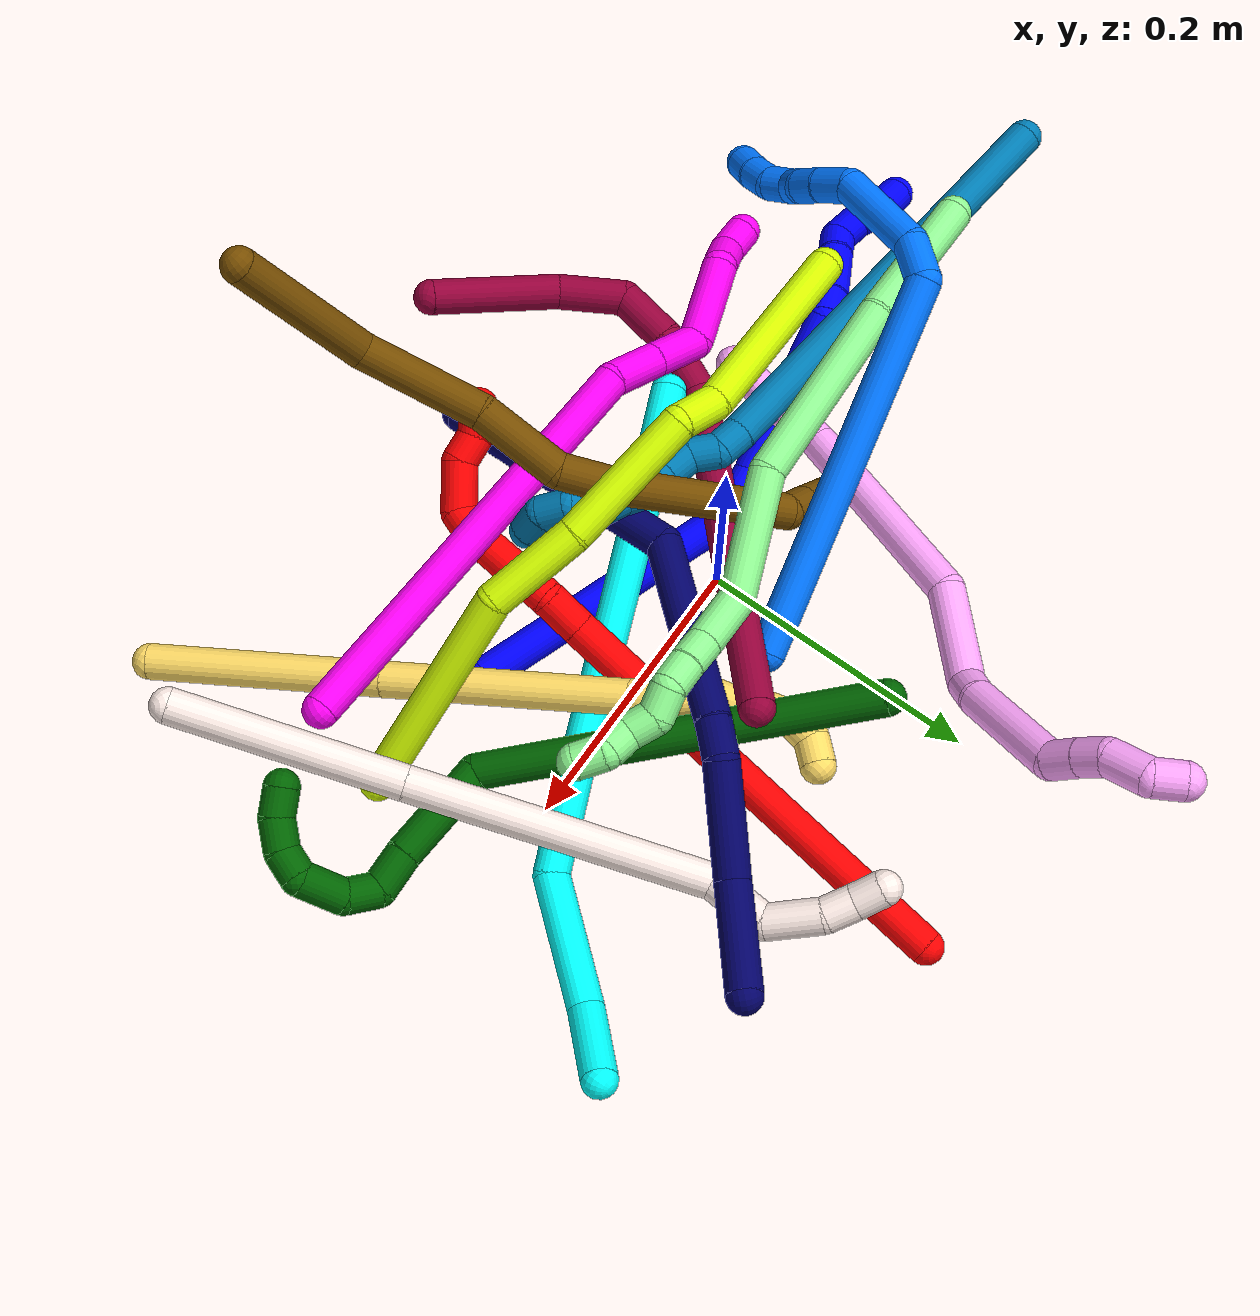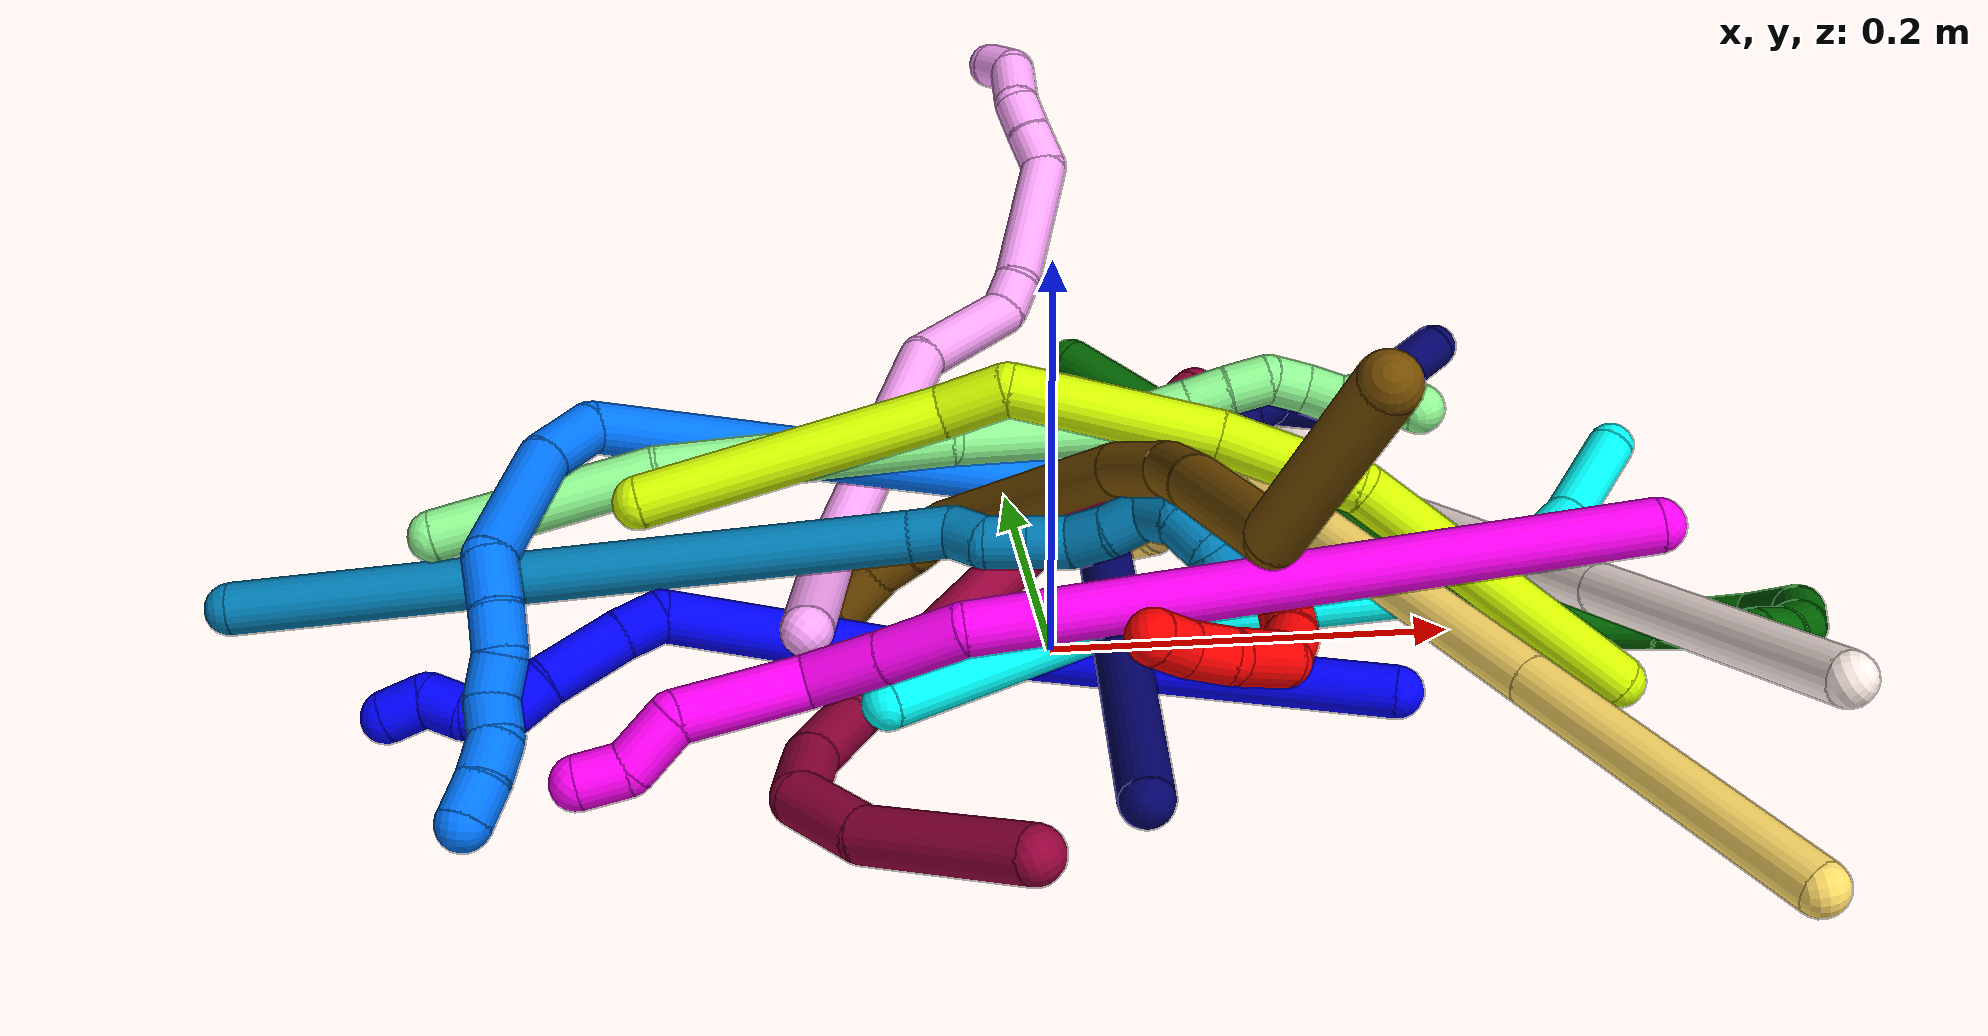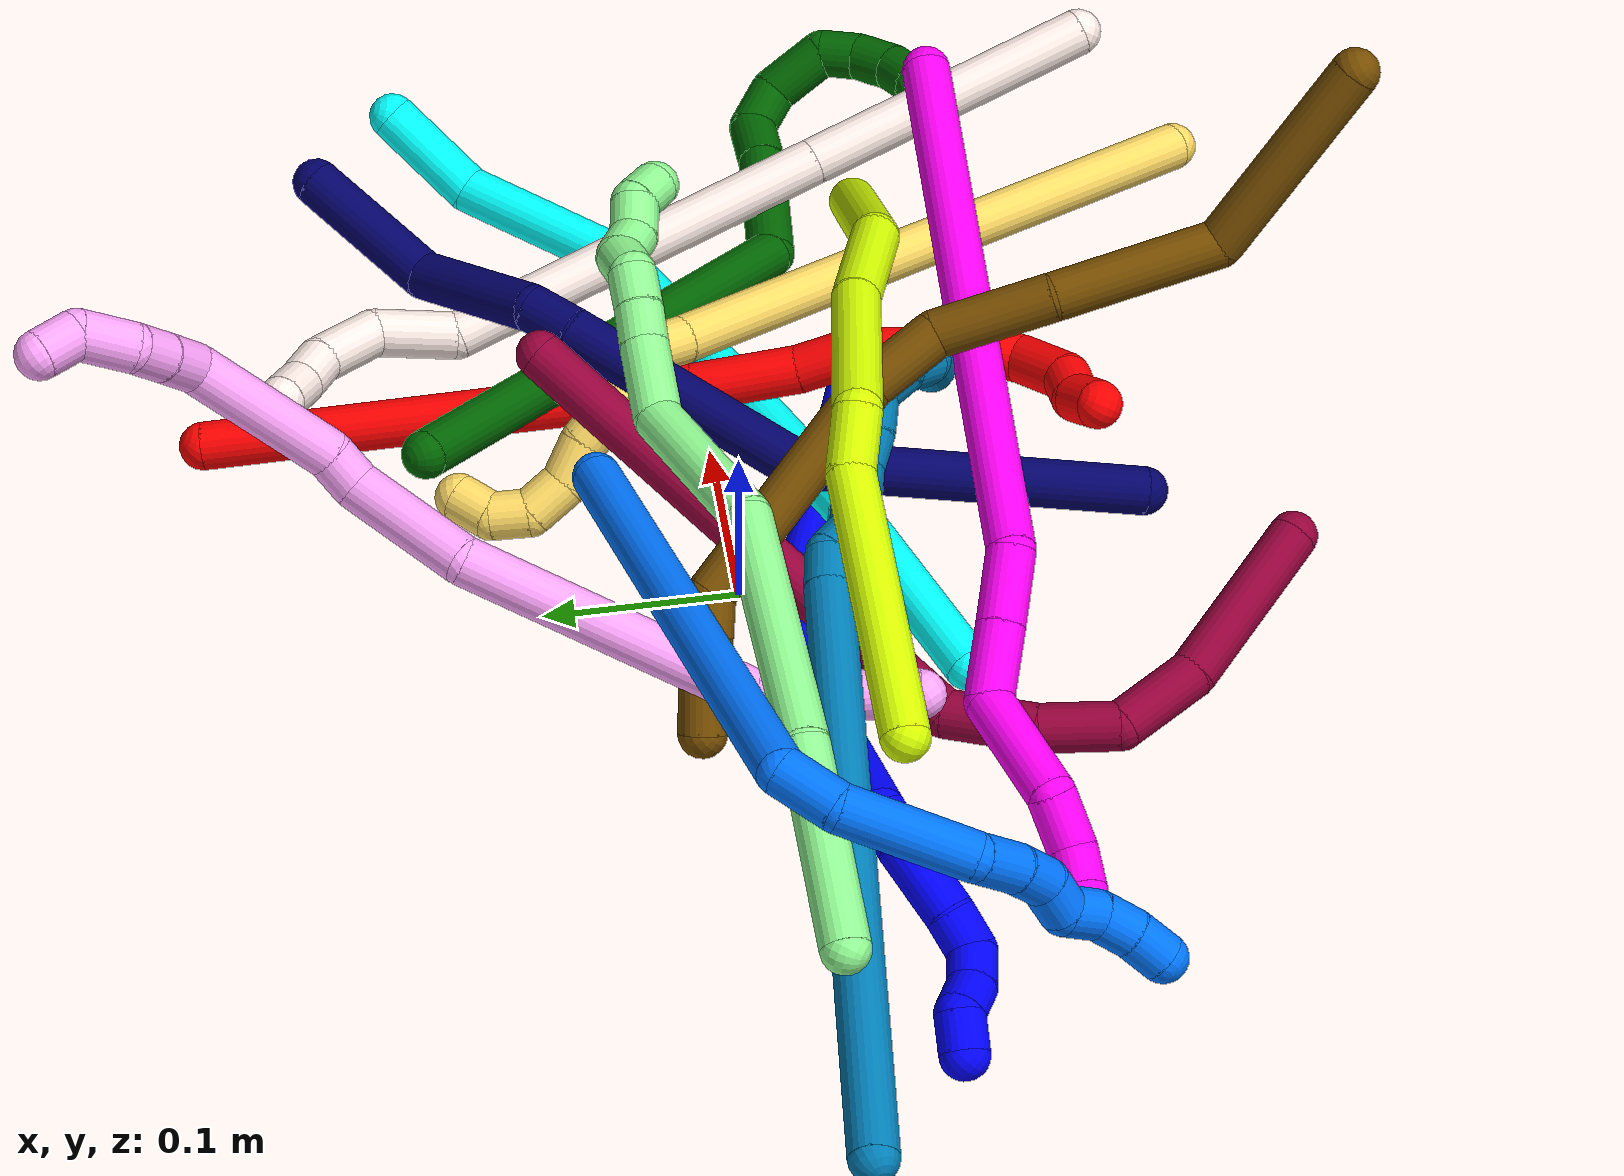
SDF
<sdf version="1.7">
 <world name="default">
  <plugin name="TubeGeneratorPlugin" filename="libtube_generator_plugin.so"/>
  <model name="photoneo_s_sensor">
   <static>1</static>
   <pose>0 0 2 1.57079 1.57079 3.14159</pose>
   <link name="link">
    <inertial><mass>0.1</mass></inertial>
    <sensor name="sensor" type="depth">
     <update_rate>30</update_rate>
     <camera>
      <horizontal_fov>1.22</horizontal_fov>
      <image><width>1920</width><height>1200</height><format>B8G8R8</format></image>
      <clip><near>0.1</near><far>4</far></clip>
      <depth_camera><output>points</output></depth_camera>
     </camera>
     <plugin name="camera_plugin" filename="libgazebo_ros_depth_camera.so">
      <baseline>0.2</baseline>
      <alwaysOn>1</alwaysOn>
      <updateRate>0.0</updateRate>
      <cameraName>camera_ir</cameraName>
      <imageTopicName>/camera/color/image_raw</imageTopicName>
      <cameraInfoTopicName>/camera/color/camera_info</cameraInfoTopicName>
      <depthImageTopicName>/camera/depth/image_raw</depthImageTopicName>
      <depthImageCameraInfoTopicName>/camera/depth/camera_info</depthImageCameraInfoTopicName>
      <pointCloudTopicName>/camera/depth/points</pointCloudTopicName>
      <frameName>fr_optical</frameName>
      <pointCloudCutoff>0.1</pointCloudCutoff>
      <pointCloudCutoffMax>2.0</pointCloudCutoffMax>
      <distortionK1>0</distortionK1>
      <distortionK2>0</distortionK2>
      <distortionK3>0</distortionK3>
      <distortionT1>0</distortionT1>
      <distortionT2>0</distortionT2>
      <CxPrime>0</CxPrime>
      <Cx>0</Cx>
      <Cy>0</Cy>
      <focalLength>0</focalLength>
      <hackBaseline>0</hackBaseline>
     </plugin>
    </sensor>
   </link>
  </model>
  <gravity>0 0 -9.8</gravity>
  <magnetic_field>6e-06 2.3e-05 -4.2e-05</magnetic_field>
  <atmosphere type="adiabatic"/>
  <physics name="default_physics" default="0" type="ode">
   <max_step_size>0.003</max_step_size>
   <real_time_factor>1</real_time_factor>
   <real_time_update_rate>1000</real_time_update_rate>
   <max_contacts>10000</max_contacts>
   <ode>
    <solver>
     <type>quick</type>
     <iters>100</iters>
     <sor>1.3</sor>
     <use_dynamic_moi_rescaling>0</use_dynamic_moi_rescaling>
    </solver>
    <constraints>
     <contact_max_correcting_vel>0</contact_max_correcting_vel>
     <contact_surface_layer>0.001</contact_surface_layer>
     <cfm>0</cfm>
     <erp>0.2</erp>
    </constraints>
   </ode>
  </physics>
  <scene><ambient>0.4 0.4 0.4 1</ambient><background>0.7 0.7 0.7 1</background><shadows>0</shadows></scene>
  <audio><device>default</device></audio>
  <spherical_coordinates>
   <surface_model>EARTH_WGS84</surface_model>
   <latitude_deg>0</latitude_deg>
   <longitude_deg>0</longitude_deg>
   <elevation>0</elevation>
   <heading_deg>0</heading_deg>
  </spherical_coordinates>
  <model name="bin">
   <static>1</static>
   <link name="bottom">
    <collision name="collision-bottom">
     <pose>0 0 -0.01 0 -0 0</pose>
     <geometry><box><size>0.8 0.6 0.02</size></box></geometry>
     <surface>
      <friction><ode><mu>100</mu><mu2>100</mu2></ode></friction>
      <contact><collide_bitmask>65535</collide_bitmask></contact>
     </surface>
    </collision>
   </link>
   <link name="west_wall">
    <collision name="collision-west_wall">
     <pose>-0.41 0 0.1 0 -0 0</pose>
     <geometry><box><size>0.02 0.6 0.2</size></box></geometry>
     <surface>
      <friction><ode><mu>100</mu><mu2>100</mu2></ode></friction>
      <contact><collide_bitmask>65535</collide_bitmask></contact>
     </surface>
    </collision>
   </link>
   <link name="east_wall">
    <collision name="collision-east_wall">
     <pose>0.41 0 0.1 0 -0 0</pose>
     <geometry><box><size>0.02 0.6 0.2</size></box></geometry>
     <surface>
      <friction><ode><mu>100</mu><mu2>100</mu2></ode></friction>
      <contact><collide_bitmask>65535</collide_bitmask></contact>
     </surface>
    </collision>
   </link>
   <link name="south_wall">
    <collision name="collision-south_wall">
     <pose>0 -0.31 0.1 0 -0 0</pose>
     <geometry><box><size>0.8 0.02 0.2</size></box></geometry>
     <surface>
      <friction><ode><mu>100</mu><mu2>100</mu2></ode></friction>
      <contact><collide_bitmask>65535</collide_bitmask></contact>
     </surface>
    </collision>
   </link>
   <link name="north_wall">
    <collision name="collision-north_wall">
     <pose>0 0.31 0.1 0 -0 0</pose>
     <geometry><box><size>0.8 0.02 0.2</size></box></geometry>
     <surface>
      <friction><ode><mu>100</mu><mu2>100</mu2></ode></friction>
      <contact><collide_bitmask>65535</collide_bitmask></contact>
     </surface>
    </collision>
   </link>
  </model>
  <model name="1">
   <static>0</static>
   <link name="1">
    <collision name="collision-cylinder-e_1_1_4">
     <pose>-0.091976 0.034457 -0.015529 -1.99422 -1.18091 1.6073</pose>
     <geometry><cylinder><radius>0.0125</radius><length>0.198876</length></cylinder></geometry>
     <surface>
      <friction><ode><mu>1.16</mu><mu2>1.16</mu2><slip1>0</slip1><slip2>0</slip2></ode></friction>
      <contact><ode><kp>1e+06</kp><kd>1</kd><max_vel>0</max_vel><min_depth>0.001</min_depth></ode></contact>
     </surface>
    </collision>
    <visual name="visual-cylinder-e_1_1_4">
     <pose>-0.091976 0.034457 -0.015529 -1.99422 -1.18091 1.6073</pose>
     <geometry><cylinder><radius>0.0125</radius><length>0.198876</length></cylinder></geometry>
     <material><ambient>0 0 1 1</ambient></material>
    </visual>
    <collision name="collision-cylinder-e_2_4_5">
     <pose>-0.201183 0.069753 -0.040032 -3.04841 -1.0889 2.98789</pose>
     <geometry><cylinder><radius>0.0125</radius><length>0.038893</length></cylinder></geometry>
     <surface>
      <friction><ode><mu>1.16</mu><mu2>1.16</mu2><slip1>0</slip1><slip2>0</slip2></ode></friction>
      <contact><ode><kp>1e+06</kp><kd>1</kd><max_vel>0</max_vel><min_depth>0.001</min_depth></ode></contact>
     </surface>
    </collision>
    <visual name="visual-cylinder-e_2_4_5">
     <pose>-0.201183 0.069753 -0.040032 -3.04841 -1.0889 2.98789</pose>
     <geometry><cylinder><radius>0.0125</radius><length>0.038893</length></cylinder></geometry>
     <material><ambient>0 0 1 1</ambient></material>
    </visual>
    <collision name="collision-cylinder-e_3_5_6">
     <pose>-0.273769 0.058986 -0.068114 2.5958 -1.18694 -2.35505</pose>
     <geometry><cylinder><radius>0.0125</radius><length>0.119397</length></cylinder></geometry>
     <surface>
      <friction><ode><mu>1.16</mu><mu2>1.16</mu2><slip1>0</slip1><slip2>0</slip2></ode></friction>
      <contact><ode><kp>1e+06</kp><kd>1</kd><max_vel>0</max_vel><min_depth>0.001</min_depth></ode></contact>
     </surface>
    </collision>
    <visual name="visual-cylinder-e_3_5_6">
     <pose>-0.273769 0.058986 -0.068114 2.5958 -1.18694 -2.35505</pose>
     <geometry><cylinder><radius>0.0125</radius><length>0.119397</length></cylinder></geometry>
     <material><ambient>0 0 1 1</ambient></material>
    </visual>
    <collision name="collision-cylinder-e_4_6_7">
     <pose>-0.335815 0.047953 -0.095404 -3.07168 -0.684425 2.94588</pose>
     <geometry><cylinder><radius>0.0125</radius><length>0.021169</length></cylinder></geometry>
     <surface>
      <friction><ode><mu>1.16</mu><mu2>1.16</mu2><slip1>0</slip1><slip2>0</slip2></ode></friction>
      <contact><ode><kp>1e+06</kp><kd>1</kd><max_vel>0</max_vel><min_depth>0.001</min_depth></ode></contact>
     </surface>
    </collision>
    <visual name="visual-cylinder-e_4_6_7">
     <pose>-0.335815 0.047953 -0.095404 -3.07168 -0.684425 2.94588</pose>
     <geometry><cylinder><radius>0.0125</radius><length>0.021169</length></cylinder></geometry>
     <material><ambient>0 0 1 1</ambient></material>
    </visual>
    <collision name="collision-cylinder-e_5_7_8">
     <pose>-0.353408 0.04903 -0.12059 -3.11198 -0.569857 3.04055</pose>
     <geometry><cylinder><radius>0.0125</radius><length>0.040412</length></cylinder></geometry>
     <surface>
      <friction><ode><mu>1.16</mu><mu2>1.16</mu2><slip1>0</slip1><slip2>0</slip2></ode></friction>
      <contact><ode><kp>1e+06</kp><kd>1</kd><max_vel>0</max_vel><min_depth>0.001</min_depth></ode></contact>
     </surface>
    </collision>
    <visual name="visual-cylinder-e_5_7_8">
     <pose>-0.353408 0.04903 -0.12059 -3.11198 -0.569857 3.04055</pose>
     <geometry><cylinder><radius>0.0125</radius><length>0.040412</length></cylinder></geometry>
     <material><ambient>0 0 1 1</ambient></material>
    </visual>
    <collision name="collision-cylinder-e_6_8_9">
     <pose>-0.368939 0.05119 -0.146807 -2.96367 -0.459361 2.4127</pose>
     <geometry><cylinder><radius>0.0125</radius><length>0.020883</length></cylinder></geometry>
     <surface>
      <friction><ode><mu>1.16</mu><mu2>1.16</mu2><slip1>0</slip1><slip2>0</slip2></ode></friction>
      <contact><ode><kp>1e+06</kp><kd>1</kd><max_vel>0</max_vel><min_depth>0.001</min_depth></ode></contact>
     </surface>
    </collision>
    <visual name="visual-cylinder-e_6_8_9">
     <pose>-0.368939 0.05119 -0.146807 -2.96367 -0.459361 2.4127</pose>
     <geometry><cylinder><radius>0.0125</radius><length>0.020883</length></cylinder></geometry>
     <material><ambient>0 0 1 1</ambient></material>
    </visual>
    <collision name="collision-cylinder-e_7_9_10">
     <pose>-0.382524 0.055854 -0.159389 -2.41312 -1.10366 2.03263</pose>
     <geometry><cylinder><radius>0.0125</radius><length>0.020061</length></cylinder></geometry>
     <surface>
      <friction><ode><mu>1.16</mu><mu2>1.16</mu2><slip1>0</slip1><slip2>0</slip2></ode></friction>
      <contact><ode><kp>1e+06</kp><kd>1</kd><max_vel>0</max_vel><min_depth>0.001</min_depth></ode></contact>
     </surface>
    </collision>
    <visual name="visual-cylinder-e_7_9_10">
     <pose>-0.382524 0.055854 -0.159389 -2.41312 -1.10366 2.03263</pose>
     <geometry><cylinder><radius>0.0125</radius><length>0.020061</length></cylinder></geometry>
     <material><ambient>0 0 1 1</ambient></material>
    </visual>
    <collision name="collision-cylinder-e_8_10_11">
     <pose>-0.401086 0.061755 -0.162149 -1.36284 -1.27212 1.0792</pose>
     <geometry><cylinder><radius>0.0125</radius><length>0.020102</length></cylinder></geometry>
     <surface>
      <friction><ode><mu>1.16</mu><mu2>1.16</mu2><slip1>0</slip1><slip2>0</slip2></ode></friction>
      <contact><ode><kp>1e+06</kp><kd>1</kd><max_vel>0</max_vel><min_depth>0.001</min_depth></ode></contact>
     </surface>
    </collision>
    <visual name="visual-cylinder-e_8_10_11">
     <pose>-0.401086 0.061755 -0.162149 -1.36284 -1.27212 1.0792</pose>
     <geometry><cylinder><radius>0.0125</radius><length>0.020102</length></cylinder></geometry>
     <material><ambient>0 0 1 1</ambient></material>
    </visual>
    <collision name="collision-cylinder-e_9_11_2">
     <pose>-0.417647 0.068823 -0.167562 -2.5356 -0.759276 1.81237</pose>
     <geometry><cylinder><radius>0.0125</radius><length>0.020207</length></cylinder></geometry>
     <surface>
      <friction><ode><mu>1.16</mu><mu2>1.16</mu2><slip1>0</slip1><slip2>0</slip2></ode></friction>
      <contact><ode><kp>1e+06</kp><kd>1</kd><max_vel>0</max_vel><min_depth>0.001</min_depth></ode></contact>
     </surface>
    </collision>
    <visual name="visual-cylinder-e_9_11_2">
     <pose>-0.417647 0.068823 -0.167562 -2.5356 -0.759276 1.81237</pose>
     <geometry><cylinder><radius>0.0125</radius><length>0.020207</length></cylinder></geometry>
     <material><ambient>0 0 1 1</ambient></material>
    </visual>
    <collision name="collision-sphere-2">
     <pose>-0.424602 0.072997 -0.173585 0 -0 0</pose>
     <geometry><sphere><radius>0.0125</radius></sphere></geometry>
     <surface>
      <friction><ode><mu>1.16</mu><mu2>1.16</mu2><slip1>0</slip1><slip2>0</slip2></ode></friction>
      <contact><ode><kp>1e+06</kp><kd>1</kd><max_vel>0</max_vel><min_depth>0.001</min_depth></ode></contact>
     </surface>
    </collision>
    <visual name="visual-sphere-2">
     <pose>-0.424602 0.072997 -0.173585 0 -0 0</pose>
     <geometry><sphere><radius>0.0125</radius></sphere></geometry>
     <material><ambient>0 0 1 1</ambient></material>
    </visual>
    <collision name="collision-sphere-11">
     <pose>-0.410692 0.064649 -0.161538 0 -0 0</pose>
     <geometry><sphere><radius>0.0125</radius></sphere></geometry>
     <surface>
      <friction><ode><mu>1.16</mu><mu2>1.16</mu2><slip1>0</slip1><slip2>0</slip2></ode></friction>
      <contact><ode><kp>1e+06</kp><kd>1</kd><max_vel>0</max_vel><min_depth>0.001</min_depth></ode></contact>
     </surface>
    </collision>
    <visual name="visual-sphere-11">
     <pose>-0.410692 0.064649 -0.161538 0 -0 0</pose>
     <geometry><sphere><radius>0.0125</radius></sphere></geometry>
     <material><ambient>0 0 1 1</ambient></material>
    </visual>
    <collision name="collision-sphere-10">
     <pose>-0.39148 0.058861 -0.162759 0 -0 0</pose>
     <geometry><sphere><radius>0.0125</radius></sphere></geometry>
     <surface>
      <friction><ode><mu>1.16</mu><mu2>1.16</mu2><slip1>0</slip1><slip2>0</slip2></ode></friction>
      <contact><ode><kp>1e+06</kp><kd>1</kd><max_vel>0</max_vel><min_depth>0.001</min_depth></ode></contact>
     </surface>
    </collision>
    <visual name="visual-sphere-10">
     <pose>-0.39148 0.058861 -0.162759 0 -0 0</pose>
     <geometry><sphere><radius>0.0125</radius></sphere></geometry>
     <material><ambient>0 0 1 1</ambient></material>
    </visual>
    <collision name="collision-sphere-9">
     <pose>-0.373568 0.052847 -0.156018 0 -0 0</pose>
     <geometry><sphere><radius>0.0125</radius></sphere></geometry>
     <surface>
      <friction><ode><mu>1.16</mu><mu2>1.16</mu2><slip1>0</slip1><slip2>0</slip2></ode></friction>
      <contact><ode><kp>1e+06</kp><kd>1</kd><max_vel>0</max_vel><min_depth>0.001</min_depth></ode></contact>
     </surface>
    </collision>
    <visual name="visual-sphere-9">
     <pose>-0.373568 0.052847 -0.156018 0 -0 0</pose>
     <geometry><sphere><radius>0.0125</radius></sphere></geometry>
     <material><ambient>0 0 1 1</ambient></material>
    </visual>
    <collision name="collision-sphere-4">
     <pose>-0.183951 0.068914 -0.031058 0 -0 0</pose>
     <geometry><sphere><radius>0.0125</radius></sphere></geometry>
     <surface>
      <friction><ode><mu>1.16</mu><mu2>1.16</mu2><slip1>0</slip1><slip2>0</slip2></ode></friction>
      <contact><ode><kp>1e+06</kp><kd>1</kd><max_vel>0</max_vel><min_depth>0.001</min_depth></ode></contact>
     </surface>
    </collision>
    <visual name="visual-sphere-4">
     <pose>-0.183951 0.068914 -0.031058 0 -0 0</pose>
     <geometry><sphere><radius>0.0125</radius></sphere></geometry>
     <material><ambient>0 0 1 1</ambient></material>
    </visual>
    <collision name="collision-sphere-1">
     <geometry><sphere><radius>0.0125</radius></sphere></geometry>
     <surface>
      <friction><ode><mu>1.16</mu><mu2>1.16</mu2><slip1>0</slip1><slip2>0</slip2></ode></friction>
      <contact><ode><kp>1e+06</kp><kd>1</kd><max_vel>0</max_vel><min_depth>0.001</min_depth></ode></contact>
     </surface>
    </collision>
    <visual name="visual-sphere-1">
     <geometry><sphere><radius>0.0125</radius></sphere></geometry>
     <material><ambient>0 0 1 1</ambient></material>
    </visual>
    <collision name="collision-sphere-8">
     <pose>-0.364309 0.049534 -0.137595 0 -0 0</pose>
     <geometry><sphere><radius>0.0125</radius></sphere></geometry>
     <surface>
      <friction><ode><mu>1.16</mu><mu2>1.16</mu2><slip1>0</slip1><slip2>0</slip2></ode></friction>
      <contact><ode><kp>1e+06</kp><kd>1</kd><max_vel>0</max_vel><min_depth>0.001</min_depth></ode></contact>
     </surface>
    </collision>
    <visual name="visual-sphere-8">
     <pose>-0.364309 0.049534 -0.137595 0 -0 0</pose>
     <geometry><sphere><radius>0.0125</radius></sphere></geometry>
     <material><ambient>0 0 1 1</ambient></material>
    </visual>
    <collision name="collision-sphere-5">
     <pose>-0.218415 0.070591 -0.049005 0 -0 0</pose>
     <geometry><sphere><radius>0.0125</radius></sphere></geometry>
     <surface>
      <friction><ode><mu>1.16</mu><mu2>1.16</mu2><slip1>0</slip1><slip2>0</slip2></ode></friction>
      <contact><ode><kp>1e+06</kp><kd>1</kd><max_vel>0</max_vel><min_depth>0.001</min_depth></ode></contact>
     </surface>
    </collision>
    <visual name="visual-sphere-5">
     <pose>-0.218415 0.070591 -0.049005 0 -0 0</pose>
     <geometry><sphere><radius>0.0125</radius></sphere></geometry>
     <material><ambient>0 0 1 1</ambient></material>
    </visual>
    <collision name="collision-sphere-6">
     <pose>-0.329123 0.047381 -0.087223 0 -0 0</pose>
     <geometry><sphere><radius>0.0125</radius></sphere></geometry>
     <surface>
      <friction><ode><mu>1.16</mu><mu2>1.16</mu2><slip1>0</slip1><slip2>0</slip2></ode></friction>
      <contact><ode><kp>1e+06</kp><kd>1</kd><max_vel>0</max_vel><min_depth>0.001</min_depth></ode></contact>
     </surface>
    </collision>
    <visual name="visual-sphere-6">
     <pose>-0.329123 0.047381 -0.087223 0 -0 0</pose>
     <geometry><sphere><radius>0.0125</radius></sphere></geometry>
     <material><ambient>0 0 1 1</ambient></material>
    </visual>
    <collision name="collision-sphere-7">
     <pose>-0.342506 0.048526 -0.103584 0 -0 0</pose>
     <geometry><sphere><radius>0.0125</radius></sphere></geometry>
     <surface>
      <friction><ode><mu>1.16</mu><mu2>1.16</mu2><slip1>0</slip1><slip2>0</slip2></ode></friction>
      <contact><ode><kp>1e+06</kp><kd>1</kd><max_vel>0</max_vel><min_depth>0.001</min_depth></ode></contact>
     </surface>
    </collision>
    <visual name="visual-sphere-7">
     <pose>-0.342506 0.048526 -0.103584 0 -0 0</pose>
     <geometry><sphere><radius>0.0125</radius></sphere></geometry>
     <material><ambient>0 0 1 1</ambient></material>
    </visual>
    <inertial>
     <pose>-0.224149 0.048853 -0.065159 0 -0 0</pose>
     <mass>0.5</mass>
     <inertia>
      <ixx>0.000125</ixx>
      <ixy>0</ixy>
      <ixz>0</ixz>
      <iyy>0.00095</iyy>
      <iyz>0</iyz>
      <izz>0.000547</izz>
     </inertia>
    </inertial>
   </link>
   <pose>0.151213 -0.087414 0.011467 -0.876993 0.377147 -0.245981</pose>
  </model>
  <model name="2">
   <static>0</static>
   <link name="2">
    <collision name="collision-cylinder-e_1_1_4">
     <pose>0.018367 -0.081071 -0.096289 2.44179 0.144891 0.392624</pose>
     <geometry><cylinder><radius>0.0125</radius><length>0.254412</length></cylinder></geometry>
     <surface>
      <friction><ode><mu>1.16</mu><mu2>1.16</mu2><slip1>0</slip1><slip2>0</slip2></ode></friction>
      <contact><ode><kp>1e+06</kp><kd>1</kd><max_vel>0</max_vel><min_depth>0.001</min_depth></ode></contact>
     </surface>
    </collision>
    <visual name="visual-cylinder-e_1_1_4">
     <pose>0.018367 -0.081071 -0.096289 2.44179 0.144891 0.392624</pose>
     <geometry><cylinder><radius>0.0125</radius><length>0.254412</length></cylinder></geometry>
     <material><ambient>1 0 0 1</ambient></material>
    </visual>
    <collision name="collision-cylinder-e_2_4_5">
     <pose>0.041382 -0.181068 -0.212511 2.38211 0.167558 0.41476</pose>
     <geometry><cylinder><radius>0.0125</radius><length>0.055756</length></cylinder></geometry>
     <surface>
      <friction><ode><mu>1.16</mu><mu2>1.16</mu2><slip1>0</slip1><slip2>0</slip2></ode></friction>
      <contact><ode><kp>1e+06</kp><kd>1</kd><max_vel>0</max_vel><min_depth>0.001</min_depth></ode></contact>
     </surface>
    </collision>
    <visual name="visual-cylinder-e_2_4_5">
     <pose>0.041382 -0.181068 -0.212511 2.38211 0.167558 0.41476</pose>
     <geometry><cylinder><radius>0.0125</radius><length>0.055756</length></cylinder></geometry>
     <material><ambient>1 0 0 1</ambient></material>
    </visual>
    <collision name="collision-cylinder-e_3_5_6">
     <pose>0.049143 -0.211173 -0.240651 2.20405 0.220714 0.430821</pose>
     <geometry><cylinder><radius>0.0125</radius><length>0.028425</length></cylinder></geometry>
     <surface>
      <friction><ode><mu>1.16</mu><mu2>1.16</mu2><slip1>0</slip1><slip2>0</slip2></ode></friction>
      <contact><ode><kp>1e+06</kp><kd>1</kd><max_vel>0</max_vel><min_depth>0.001</min_depth></ode></contact>
     </surface>
    </collision>
    <visual name="visual-cylinder-e_3_5_6">
     <pose>0.049143 -0.211173 -0.240651 2.20405 0.220714 0.430821</pose>
     <geometry><cylinder><radius>0.0125</radius><length>0.028425</length></cylinder></geometry>
     <material><ambient>1 0 0 1</ambient></material>
    </visual>
    <collision name="collision-cylinder-e_4_6_7">
     <pose>0.055989 -0.239502 -0.276675 2.58907 0.113768 0.396445</pose>
     <geometry><cylinder><radius>0.0125</radius><length>0.065784</length></cylinder></geometry>
     <surface>
      <friction><ode><mu>1.16</mu><mu2>1.16</mu2><slip1>0</slip1><slip2>0</slip2></ode></friction>
      <contact><ode><kp>1e+06</kp><kd>1</kd><max_vel>0</max_vel><min_depth>0.001</min_depth></ode></contact>
     </surface>
    </collision>
    <visual name="visual-cylinder-e_4_6_7">
     <pose>0.055989 -0.239502 -0.276675 2.58907 0.113768 0.396445</pose>
     <geometry><cylinder><radius>0.0125</radius><length>0.065784</length></cylinder></geometry>
     <material><ambient>1 0 0 1</ambient></material>
    </visual>
    <collision name="collision-cylinder-e_5_7_8">
     <pose>0.058236 -0.262072 -0.313209 2.58544 -0.143819 -0.494345</pose>
     <geometry><cylinder><radius>0.0125</radius><length>0.020742</length></cylinder></geometry>
     <surface>
      <friction><ode><mu>1.16</mu><mu2>1.16</mu2><slip1>0</slip1><slip2>0</slip2></ode></friction>
      <contact><ode><kp>1e+06</kp><kd>1</kd><max_vel>0</max_vel><min_depth>0.001</min_depth></ode></contact>
     </surface>
    </collision>
    <visual name="visual-cylinder-e_5_7_8">
     <pose>0.058236 -0.262072 -0.313209 2.58544 -0.143819 -0.494345</pose>
     <geometry><cylinder><radius>0.0125</radius><length>0.020742</length></cylinder></geometry>
     <material><ambient>1 0 0 1</ambient></material>
    </visual>
    <collision name="collision-cylinder-e_6_8_9">
     <pose>0.047275 -0.280849 -0.327481 1.96491 -0.579817 -0.840949</pose>
     <geometry><cylinder><radius>0.0125</radius><length>0.034589</length></cylinder></geometry>
     <surface>
      <friction><ode><mu>1.16</mu><mu2>1.16</mu2><slip1>0</slip1><slip2>0</slip2></ode></friction>
      <contact><ode><kp>1e+06</kp><kd>1</kd><max_vel>0</max_vel><min_depth>0.001</min_depth></ode></contact>
     </surface>
    </collision>
    <visual name="visual-cylinder-e_6_8_9">
     <pose>0.047275 -0.280849 -0.327481 1.96491 -0.579817 -0.840949</pose>
     <geometry><cylinder><radius>0.0125</radius><length>0.034589</length></cylinder></geometry>
     <material><ambient>1 0 0 1</ambient></material>
    </visual>
    <collision name="collision-cylinder-e_7_9_10">
     <pose>0.029161 -0.299364 -0.332796 1.52403 -1.03225 -0.992581</pose>
     <geometry><cylinder><radius>0.0125</radius><length>0.020126</length></cylinder></geometry>
     <surface>
      <friction><ode><mu>1.16</mu><mu2>1.16</mu2><slip1>0</slip1><slip2>0</slip2></ode></friction>
      <contact><ode><kp>1e+06</kp><kd>1</kd><max_vel>0</max_vel><min_depth>0.001</min_depth></ode></contact>
     </surface>
    </collision>
    <visual name="visual-cylinder-e_7_9_10">
     <pose>0.029161 -0.299364 -0.332796 1.52403 -1.03225 -0.992581</pose>
     <geometry><cylinder><radius>0.0125</radius><length>0.020126</length></cylinder></geometry>
     <material><ambient>1 0 0 1</ambient></material>
    </visual>
    <collision name="collision-cylinder-e_8_10_2">
     <pose>0.015068 -0.312912 -0.333776 1.71541 -0.57147 -0.654858</pose>
     <geometry><cylinder><radius>0.0125</radius><length>0.020167</length></cylinder></geometry>
     <surface>
      <friction><ode><mu>1.16</mu><mu2>1.16</mu2><slip1>0</slip1><slip2>0</slip2></ode></friction>
      <contact><ode><kp>1e+06</kp><kd>1</kd><max_vel>0</max_vel><min_depth>0.001</min_depth></ode></contact>
     </surface>
    </collision>
    <visual name="visual-cylinder-e_8_10_2">
     <pose>0.015068 -0.312912 -0.333776 1.71541 -0.57147 -0.654858</pose>
     <geometry><cylinder><radius>0.0125</radius><length>0.020167</length></cylinder></geometry>
     <material><ambient>1 0 0 1</ambient></material>
    </visual>
    <collision name="collision-sphere-2">
     <pose>0.009614 -0.321305 -0.334999 0 -0 0</pose>
     <geometry><sphere><radius>0.0125</radius></sphere></geometry>
     <surface>
      <friction><ode><mu>1.16</mu><mu2>1.16</mu2><slip1>0</slip1><slip2>0</slip2></ode></friction>
      <contact><ode><kp>1e+06</kp><kd>1</kd><max_vel>0</max_vel><min_depth>0.001</min_depth></ode></contact>
     </surface>
    </collision>
    <visual name="visual-sphere-2">
     <pose>0.009614 -0.321305 -0.334999 0 -0 0</pose>
     <geometry><sphere><radius>0.0125</radius></sphere></geometry>
     <material><ambient>1 0 0 1</ambient></material>
    </visual>
    <collision name="collision-sphere-10">
     <pose>0.020522 -0.304519 -0.332554 0 -0 0</pose>
     <geometry><sphere><radius>0.0125</radius></sphere></geometry>
     <surface>
      <friction><ode><mu>1.16</mu><mu2>1.16</mu2><slip1>0</slip1><slip2>0</slip2></ode></friction>
      <contact><ode><kp>1e+06</kp><kd>1</kd><max_vel>0</max_vel><min_depth>0.001</min_depth></ode></contact>
     </surface>
    </collision>
    <visual name="visual-sphere-10">
     <pose>0.020522 -0.304519 -0.332554 0 -0 0</pose>
     <geometry><sphere><radius>0.0125</radius></sphere></geometry>
     <material><ambient>1 0 0 1</ambient></material>
    </visual>
    <collision name="collision-sphere-9">
     <pose>0.0378 -0.294208 -0.333037 0 -0 0</pose>
     <geometry><sphere><radius>0.0125</radius></sphere></geometry>
     <surface>
      <friction><ode><mu>1.16</mu><mu2>1.16</mu2><slip1>0</slip1><slip2>0</slip2></ode></friction>
      <contact><ode><kp>1e+06</kp><kd>1</kd><max_vel>0</max_vel><min_depth>0.001</min_depth></ode></contact>
     </surface>
    </collision>
    <visual name="visual-sphere-9">
     <pose>0.0378 -0.294208 -0.333037 0 -0 0</pose>
     <geometry><sphere><radius>0.0125</radius></sphere></geometry>
     <material><ambient>1 0 0 1</ambient></material>
    </visual>
    <collision name="collision-sphere-4">
     <pose>0.036733 -0.162141 -0.192578 0 -0 0</pose>
     <geometry><sphere><radius>0.0125</radius></sphere></geometry>
     <surface>
      <friction><ode><mu>1.16</mu><mu2>1.16</mu2><slip1>0</slip1><slip2>0</slip2></ode></friction>
      <contact><ode><kp>1e+06</kp><kd>1</kd><max_vel>0</max_vel><min_depth>0.001</min_depth></ode></contact>
     </surface>
    </collision>
    <visual name="visual-sphere-4">
     <pose>0.036733 -0.162141 -0.192578 0 -0 0</pose>
     <geometry><sphere><radius>0.0125</radius></sphere></geometry>
     <material><ambient>1 0 0 1</ambient></material>
    </visual>
    <collision name="collision-sphere-1">
     <geometry><sphere><radius>0.0125</radius></sphere></geometry>
     <surface>
      <friction><ode><mu>1.16</mu><mu2>1.16</mu2><slip1>0</slip1><slip2>0</slip2></ode></friction>
      <contact><ode><kp>1e+06</kp><kd>1</kd><max_vel>0</max_vel><min_depth>0.001</min_depth></ode></contact>
     </surface>
    </collision>
    <visual name="visual-sphere-1">
     <geometry><sphere><radius>0.0125</radius></sphere></geometry>
     <material><ambient>1 0 0 1</ambient></material>
    </visual>
    <collision name="collision-sphere-8">
     <pose>0.05675 -0.267491 -0.321926 0 -0 0</pose>
     <geometry><sphere><radius>0.0125</radius></sphere></geometry>
     <surface>
      <friction><ode><mu>1.16</mu><mu2>1.16</mu2><slip1>0</slip1><slip2>0</slip2></ode></friction>
      <contact><ode><kp>1e+06</kp><kd>1</kd><max_vel>0</max_vel><min_depth>0.001</min_depth></ode></contact>
     </surface>
    </collision>
    <visual name="visual-sphere-8">
     <pose>0.05675 -0.267491 -0.321926 0 -0 0</pose>
     <geometry><sphere><radius>0.0125</radius></sphere></geometry>
     <material><ambient>1 0 0 1</ambient></material>
    </visual>
    <collision name="collision-sphere-5">
     <pose>0.046032 -0.199994 -0.232445 0 -0 0</pose>
     <geometry><sphere><radius>0.0125</radius></sphere></geometry>
     <surface>
      <friction><ode><mu>1.16</mu><mu2>1.16</mu2><slip1>0</slip1><slip2>0</slip2></ode></friction>
      <contact><ode><kp>1e+06</kp><kd>1</kd><max_vel>0</max_vel><min_depth>0.001</min_depth></ode></contact>
     </surface>
    </collision>
    <visual name="visual-sphere-5">
     <pose>0.046032 -0.199994 -0.232445 0 -0 0</pose>
     <geometry><sphere><radius>0.0125</radius></sphere></geometry>
     <material><ambient>1 0 0 1</ambient></material>
    </visual>
    <collision name="collision-sphere-6">
     <pose>0.052255 -0.222351 -0.248858 0 -0 0</pose>
     <geometry><sphere><radius>0.0125</radius></sphere></geometry>
     <surface>
      <friction><ode><mu>1.16</mu><mu2>1.16</mu2><slip1>0</slip1><slip2>0</slip2></ode></friction>
      <contact><ode><kp>1e+06</kp><kd>1</kd><max_vel>0</max_vel><min_depth>0.001</min_depth></ode></contact>
     </surface>
    </collision>
    <visual name="visual-sphere-6">
     <pose>0.052255 -0.222351 -0.248858 0 -0 0</pose>
     <geometry><sphere><radius>0.0125</radius></sphere></geometry>
     <material><ambient>1 0 0 1</ambient></material>
    </visual>
    <collision name="collision-sphere-7">
     <pose>0.059723 -0.256654 -0.304491 0 -0 0</pose>
     <geometry><sphere><radius>0.0125</radius></sphere></geometry>
     <surface>
      <friction><ode><mu>1.16</mu><mu2>1.16</mu2><slip1>0</slip1><slip2>0</slip2></ode></friction>
      <contact><ode><kp>1e+06</kp><kd>1</kd><max_vel>0</max_vel><min_depth>0.001</min_depth></ode></contact>
     </surface>
    </collision>
    <visual name="visual-sphere-7">
     <pose>0.059723 -0.256654 -0.304491 0 -0 0</pose>
     <geometry><sphere><radius>0.0125</radius></sphere></geometry>
     <material><ambient>1 0 0 1</ambient></material>
    </visual>
    <inertial>
     <pose>0.031588 -0.159929 -0.18528 0 -0 0</pose>
     <mass>0.5</mass>
     <inertia>
      <ixx>0.001848</ixx>
      <ixy>0</ixy>
      <ixz>0</ixz>
      <iyy>-0.000448</iyy>
      <iyz>0</iyz>
      <izz>0.000688</izz>
     </inertia>
    </inertial>
   </link>
   <pose>0.132022 0.258764 0.011664 -0.97978 -0.211743 -0.235189</pose>
  </model>
  <model name="3">
   <static>0</static>
   <link name="3">
    <collision name="collision-cylinder-e_1_1_4">
     <pose>-0.047661 0.008458 -0.026598 -2.83372 -1.04103 2.61292</pose>
     <geometry><cylinder><radius>0.0125</radius><length>0.110464</length></cylinder></geometry>
     <surface>
      <friction><ode><mu>1.16</mu><mu2>1.16</mu2><slip1>0</slip1><slip2>0</slip2></ode></friction>
      <contact><ode><kp>1e+06</kp><kd>1</kd><max_vel>0</max_vel><min_depth>0.001</min_depth></ode></contact>
     </surface>
    </collision>
    <visual name="visual-cylinder-e_1_1_4">
     <pose>-0.047661 0.008458 -0.026598 -2.83372 -1.04103 2.61292</pose>
     <geometry><cylinder><radius>0.0125</radius><length>0.110464</length></cylinder></geometry>
     <material><ambient>0.003922 1 0.996078 1</ambient></material>
    </visual>
    <collision name="collision-cylinder-e_2_4_5">
     <pose>-0.16972 0.046668 -0.083206 -2.36049 -1.05423 1.91034</pose>
     <geometry><cylinder><radius>0.0125</radius><length>0.171124</length></cylinder></geometry>
     <surface>
      <friction><ode><mu>1.16</mu><mu2>1.16</mu2><slip1>0</slip1><slip2>0</slip2></ode></friction>
      <contact><ode><kp>1e+06</kp><kd>1</kd><max_vel>0</max_vel><min_depth>0.001</min_depth></ode></contact>
     </surface>
    </collision>
    <visual name="visual-cylinder-e_2_4_5">
     <pose>-0.16972 0.046668 -0.083206 -2.36049 -1.05423 1.91034</pose>
     <geometry><cylinder><radius>0.0125</radius><length>0.171124</length></cylinder></geometry>
     <material><ambient>0.003922 1 0.996078 1</ambient></material>
    </visual>
    <collision name="collision-cylinder-e_3_5_6">
     <pose>-0.274149 0.088351 -0.126179 -2.39769 -1.04027 1.94569</pose>
     <geometry><cylinder><radius>0.0125</radius><length>0.069634</length></cylinder></geometry>
     <surface>
      <friction><ode><mu>1.16</mu><mu2>1.16</mu2><slip1>0</slip1><slip2>0</slip2></ode></friction>
      <contact><ode><kp>1e+06</kp><kd>1</kd><max_vel>0</max_vel><min_depth>0.001</min_depth></ode></contact>
     </surface>
    </collision>
    <visual name="visual-cylinder-e_3_5_6">
     <pose>-0.274149 0.088351 -0.126179 -2.39769 -1.04027 1.94569</pose>
     <geometry><cylinder><radius>0.0125</radius><length>0.069634</length></cylinder></geometry>
     <material><ambient>0.003922 1 0.996078 1</ambient></material>
    </visual>
    <collision name="collision-cylinder-e_4_6_7">
     <pose>-0.329491 0.11679 -0.174176 -2.70121 -0.578881 1.85258</pose>
     <geometry><cylinder><radius>0.0125</radius><length>0.092533</length></cylinder></geometry>
     <surface>
      <friction><ode><mu>1.16</mu><mu2>1.16</mu2><slip1>0</slip1><slip2>0</slip2></ode></friction>
      <contact><ode><kp>1e+06</kp><kd>1</kd><max_vel>0</max_vel><min_depth>0.001</min_depth></ode></contact>
     </surface>
    </collision>
    <visual name="visual-cylinder-e_4_6_7">
     <pose>-0.329491 0.11679 -0.174176 -2.70121 -0.578881 1.85258</pose>
     <geometry><cylinder><radius>0.0125</radius><length>0.092533</length></cylinder></geometry>
     <material><ambient>0.003922 1 0.996078 1</ambient></material>
    </visual>
    <collision name="collision-cylinder-e_5_7_2">
     <pose>-0.370523 0.131011 -0.232415 3.04331 -0.593143 -2.82245</pose>
     <geometry><cylinder><radius>0.0125</radius><length>0.056245</length></cylinder></geometry>
     <surface>
      <friction><ode><mu>1.16</mu><mu2>1.16</mu2><slip1>0</slip1><slip2>0</slip2></ode></friction>
      <contact><ode><kp>1e+06</kp><kd>1</kd><max_vel>0</max_vel><min_depth>0.001</min_depth></ode></contact>
     </surface>
    </collision>
    <visual name="visual-cylinder-e_5_7_2">
     <pose>-0.370523 0.131011 -0.232415 3.04331 -0.593143 -2.82245</pose>
     <geometry><cylinder><radius>0.0125</radius><length>0.056245</length></cylinder></geometry>
     <material><ambient>0.003922 1 0.996078 1</ambient></material>
    </visual>
    <collision name="collision-sphere-2">
     <pose>-0.386243 0.128723 -0.255622 0 -0 0</pose>
     <geometry><sphere><radius>0.0125</radius></sphere></geometry>
     <surface>
      <friction><ode><mu>1.16</mu><mu2>1.16</mu2><slip1>0</slip1><slip2>0</slip2></ode></friction>
      <contact><ode><kp>1e+06</kp><kd>1</kd><max_vel>0</max_vel><min_depth>0.001</min_depth></ode></contact>
     </surface>
    </collision>
    <visual name="visual-sphere-2">
     <pose>-0.386243 0.128723 -0.255622 0 -0 0</pose>
     <geometry><sphere><radius>0.0125</radius></sphere></geometry>
     <material><ambient>0.003922 1 0.996078 1</ambient></material>
    </visual>
    <collision name="collision-sphere-7">
     <pose>-0.354803 0.133299 -0.209209 0 -0 0</pose>
     <geometry><sphere><radius>0.0125</radius></sphere></geometry>
     <surface>
      <friction><ode><mu>1.16</mu><mu2>1.16</mu2><slip1>0</slip1><slip2>0</slip2></ode></friction>
      <contact><ode><kp>1e+06</kp><kd>1</kd><max_vel>0</max_vel><min_depth>0.001</min_depth></ode></contact>
     </surface>
    </collision>
    <visual name="visual-sphere-7">
     <pose>-0.354803 0.133299 -0.209209 0 -0 0</pose>
     <geometry><sphere><radius>0.0125</radius></sphere></geometry>
     <material><ambient>0.003922 1 0.996078 1</ambient></material>
    </visual>
    <collision name="collision-sphere-6">
     <pose>-0.30418 0.10028 -0.139142 0 -0 0</pose>
     <geometry><sphere><radius>0.0125</radius></sphere></geometry>
     <surface>
      <friction><ode><mu>1.16</mu><mu2>1.16</mu2><slip1>0</slip1><slip2>0</slip2></ode></friction>
      <contact><ode><kp>1e+06</kp><kd>1</kd><max_vel>0</max_vel><min_depth>0.001</min_depth></ode></contact>
     </surface>
    </collision>
    <visual name="visual-sphere-6">
     <pose>-0.30418 0.10028 -0.139142 0 -0 0</pose>
     <geometry><sphere><radius>0.0125</radius></sphere></geometry>
     <material><ambient>0.003922 1 0.996078 1</ambient></material>
    </visual>
    <collision name="collision-sphere-5">
     <pose>-0.244118 0.076421 -0.113216 0 -0 0</pose>
     <geometry><sphere><radius>0.0125</radius></sphere></geometry>
     <surface>
      <friction><ode><mu>1.16</mu><mu2>1.16</mu2><slip1>0</slip1><slip2>0</slip2></ode></friction>
      <contact><ode><kp>1e+06</kp><kd>1</kd><max_vel>0</max_vel><min_depth>0.001</min_depth></ode></contact>
     </surface>
    </collision>
    <visual name="visual-sphere-5">
     <pose>-0.244118 0.076421 -0.113216 0 -0 0</pose>
     <geometry><sphere><radius>0.0125</radius></sphere></geometry>
     <material><ambient>0.003922 1 0.996078 1</ambient></material>
    </visual>
    <collision name="collision-sphere-1">
     <geometry><sphere><radius>0.0125</radius></sphere></geometry>
     <surface>
      <friction><ode><mu>1.16</mu><mu2>1.16</mu2><slip1>0</slip1><slip2>0</slip2></ode></friction>
      <contact><ode><kp>1e+06</kp><kd>1</kd><max_vel>0</max_vel><min_depth>0.001</min_depth></ode></contact>
     </surface>
    </collision>
    <visual name="visual-sphere-1">
     <geometry><sphere><radius>0.0125</radius></sphere></geometry>
     <material><ambient>0.003922 1 0.996078 1</ambient></material>
    </visual>
    <collision name="collision-sphere-4">
     <pose>-0.095322 0.016915 -0.053197 0 -0 0</pose>
     <geometry><sphere><radius>0.0125</radius></sphere></geometry>
     <surface>
      <friction><ode><mu>1.16</mu><mu2>1.16</mu2><slip1>0</slip1><slip2>0</slip2></ode></friction>
      <contact><ode><kp>1e+06</kp><kd>1</kd><max_vel>0</max_vel><min_depth>0.001</min_depth></ode></contact>
     </surface>
    </collision>
    <visual name="visual-sphere-4">
     <pose>-0.095322 0.016915 -0.053197 0 -0 0</pose>
     <geometry><sphere><radius>0.0125</radius></sphere></geometry>
     <material><ambient>0.003922 1 0.996078 1</ambient></material>
    </visual>
    <inertial>
     <pose>-0.209454 0.066496 -0.110305 0 -0 0</pose>
     <mass>0.5</mass>
     <inertia>
      <ixx>0.000107</ixx>
      <ixy>0</ixy>
      <ixz>0</ixz>
      <iyy>0.000835</iyy>
      <iyz>0</iyz>
      <izz>0.000324</izz>
     </inertia>
    </inertial>
   </link>
   <pose>-0.086796 -0.1019 0.026876 -2.02742 0.043628 3.02572</pose>
  </model>
  <model name="4">
   <static>0</static>
   <link name="4">
    <collision name="collision-cylinder-e_1_1_4">
     <pose>-0.00235 0.033669 0.022317 -0.985454 -0.05811 0.031205</pose>
     <geometry><cylinder><radius>0.0125</radius><length>0.080925</length></cylinder></geometry>
     <surface>
      <friction><ode><mu>1.16</mu><mu2>1.16</mu2><slip1>0</slip1><slip2>0</slip2></ode></friction>
      <contact><ode><kp>1e+06</kp><kd>1</kd><max_vel>0</max_vel><min_depth>0.001</min_depth></ode></contact>
     </surface>
    </collision>
    <visual name="visual-cylinder-e_1_1_4">
     <pose>-0.00235 0.033669 0.022317 -0.985454 -0.05811 0.031205</pose>
     <geometry><cylinder><radius>0.0125</radius><length>0.080925</length></cylinder></geometry>
     <material><ambient>1 0.65098 0.996078 1</ambient></material>
    </visual>
    <collision name="collision-cylinder-e_2_4_5">
     <pose>-0.016214 0.106801 0.111597 -0.532527 -0.147071 0.040179</pose>
     <geometry><cylinder><radius>0.0125</radius><length>0.157147</length></cylinder></geometry>
     <surface>
      <friction><ode><mu>1.16</mu><mu2>1.16</mu2><slip1>0</slip1><slip2>0</slip2></ode></friction>
      <contact><ode><kp>1e+06</kp><kd>1</kd><max_vel>0</max_vel><min_depth>0.001</min_depth></ode></contact>
     </surface>
    </collision>
    <visual name="visual-cylinder-e_2_4_5">
     <pose>-0.016214 0.106801 0.111597 -0.532527 -0.147071 0.040179</pose>
     <geometry><cylinder><radius>0.0125</radius><length>0.157147</length></cylinder></geometry>
     <material><ambient>1 0.65098 0.996078 1</ambient></material>
    </visual>
    <collision name="collision-cylinder-e_3_5_6">
     <pose>-0.017889 0.159327 0.208093 -0.41647 0.295739 -0.062928</pose>
     <geometry><cylinder><radius>0.0125</radius><length>0.06752</length></cylinder></geometry>
     <surface>
      <friction><ode><mu>1.16</mu><mu2>1.16</mu2><slip1>0</slip1><slip2>0</slip2></ode></friction>
      <contact><ode><kp>1e+06</kp><kd>1</kd><max_vel>0</max_vel><min_depth>0.001</min_depth></ode></contact>
     </surface>
    </collision>
    <visual name="visual-cylinder-e_3_5_6">
     <pose>-0.017889 0.159327 0.208093 -0.41647 0.295739 -0.062928</pose>
     <geometry><cylinder><radius>0.0125</radius><length>0.06752</length></cylinder></geometry>
     <material><ambient>1 0.65098 0.996078 1</ambient></material>
    </visual>
    <collision name="collision-cylinder-e_4_6_7">
     <pose>-0.01097 0.17315 0.247457 -0.077043 -0.28796 0.011175</pose>
     <geometry><cylinder><radius>0.0125</radius><length>0.020567</length></cylinder></geometry>
     <surface>
      <friction><ode><mu>1.16</mu><mu2>1.16</mu2><slip1>0</slip1><slip2>0</slip2></ode></friction>
      <contact><ode><kp>1e+06</kp><kd>1</kd><max_vel>0</max_vel><min_depth>0.001</min_depth></ode></contact>
     </surface>
    </collision>
    <visual name="visual-cylinder-e_4_6_7">
     <pose>-0.01097 0.17315 0.247457 -0.077043 -0.28796 0.011175</pose>
     <geometry><cylinder><radius>0.0125</radius><length>0.020567</length></cylinder></geometry>
     <material><ambient>1 0.65098 0.996078 1</ambient></material>
    </visual>
    <collision name="collision-cylinder-e_5_7_8">
     <pose>-0.027659 0.187051 0.292526 -0.356979 -0.350935 0.063948</pose>
     <geometry><cylinder><radius>0.0125</radius><length>0.0801</length></cylinder></geometry>
     <surface>
      <friction><ode><mu>1.16</mu><mu2>1.16</mu2><slip1>0</slip1><slip2>0</slip2></ode></friction>
      <contact><ode><kp>1e+06</kp><kd>1</kd><max_vel>0</max_vel><min_depth>0.001</min_depth></ode></contact>
     </surface>
    </collision>
    <visual name="visual-cylinder-e_5_7_8">
     <pose>-0.027659 0.187051 0.292526 -0.356979 -0.350935 0.063948</pose>
     <geometry><cylinder><radius>0.0125</radius><length>0.0801</length></cylinder></geometry>
     <material><ambient>1 0.65098 0.996078 1</ambient></material>
    </visual>
    <collision name="collision-cylinder-e_6_8_9">
     <pose>-0.051118 0.203247 0.333609 -0.481427 -0.973301 0.25831</pose>
     <geometry><cylinder><radius>0.0125</radius><length>0.023444</length></cylinder></geometry>
     <surface>
      <friction><ode><mu>1.16</mu><mu2>1.16</mu2><slip1>0</slip1><slip2>0</slip2></ode></friction>
      <contact><ode><kp>1e+06</kp><kd>1</kd><max_vel>0</max_vel><min_depth>0.001</min_depth></ode></contact>
     </surface>
    </collision>
    <visual name="visual-cylinder-e_6_8_9">
     <pose>-0.051118 0.203247 0.333609 -0.481427 -0.973301 0.25831</pose>
     <geometry><cylinder><radius>0.0125</radius><length>0.023444</length></cylinder></geometry>
     <material><ambient>1 0.65098 0.996078 1</ambient></material>
    </visual>
    <collision name="collision-cylinder-e_7_9_10">
     <pose>-0.06872 0.209468 0.344876 -0.528642 -0.899785 0.259936</pose>
     <geometry><cylinder><radius>0.0125</radius><length>0.020201</length></cylinder></geometry>
     <surface>
      <friction><ode><mu>1.16</mu><mu2>1.16</mu2><slip1>0</slip1><slip2>0</slip2></ode></friction>
      <contact><ode><kp>1e+06</kp><kd>1</kd><max_vel>0</max_vel><min_depth>0.001</min_depth></ode></contact>
     </surface>
    </collision>
    <visual name="visual-cylinder-e_7_9_10">
     <pose>-0.06872 0.209468 0.344876 -0.528642 -0.899785 0.259936</pose>
     <geometry><cylinder><radius>0.0125</radius><length>0.020201</length></cylinder></geometry>
     <material><ambient>1 0.65098 0.996078 1</ambient></material>
    </visual>
    <collision name="collision-cylinder-e_8_10_11">
     <pose>-0.08335 0.220955 0.360254 -0.696186 -0.477939 0.176349</pose>
     <geometry><cylinder><radius>0.0125</radius><length>0.029221</length></cylinder></geometry>
     <surface>
      <friction><ode><mu>1.16</mu><mu2>1.16</mu2><slip1>0</slip1><slip2>0</slip2></ode></friction>
      <contact><ode><kp>1e+06</kp><kd>1</kd><max_vel>0</max_vel><min_depth>0.001</min_depth></ode></contact>
     </surface>
    </collision>
    <visual name="visual-cylinder-e_8_10_11">
     <pose>-0.08335 0.220955 0.360254 -0.696186 -0.477939 0.176349</pose>
     <geometry><cylinder><radius>0.0125</radius><length>0.029221</length></cylinder></geometry>
     <material><ambient>1 0.65098 0.996078 1</ambient></material>
    </visual>
    <collision name="collision-cylinder-e_9_11_2">
     <pose>-0.095273 0.238309 0.37074 -1.51201 -0.521744 0.493166</pose>
     <geometry><cylinder><radius>0.0125</radius><length>0.020877</length></cylinder></geometry>
     <surface>
      <friction><ode><mu>1.16</mu><mu2>1.16</mu2><slip1>0</slip1><slip2>0</slip2></ode></friction>
      <contact><ode><kp>1e+06</kp><kd>1</kd><max_vel>0</max_vel><min_depth>0.001</min_depth></ode></contact>
     </surface>
    </collision>
    <visual name="visual-cylinder-e_9_11_2">
     <pose>-0.095273 0.238309 0.37074 -1.51201 -0.521744 0.493166</pose>
     <geometry><cylinder><radius>0.0125</radius><length>0.020877</length></cylinder></geometry>
     <material><ambient>1 0.65098 0.996078 1</ambient></material>
    </visual>
    <collision name="collision-sphere-2">
     <pose>-0.100475 0.247343 0.371272 0 -0 0</pose>
     <geometry><sphere><radius>0.0125</radius></sphere></geometry>
     <surface>
      <friction><ode><mu>1.16</mu><mu2>1.16</mu2><slip1>0</slip1><slip2>0</slip2></ode></friction>
      <contact><ode><kp>1e+06</kp><kd>1</kd><max_vel>0</max_vel><min_depth>0.001</min_depth></ode></contact>
     </surface>
    </collision>
    <visual name="visual-sphere-2">
     <pose>-0.100475 0.247343 0.371272 0 -0 0</pose>
     <geometry><sphere><radius>0.0125</radius></sphere></geometry>
     <material><ambient>1 0.65098 0.996078 1</ambient></material>
    </visual>
    <collision name="collision-sphere-11">
     <pose>-0.09007 0.229275 0.370208 0 -0 0</pose>
     <geometry><sphere><radius>0.0125</radius></sphere></geometry>
     <surface>
      <friction><ode><mu>1.16</mu><mu2>1.16</mu2><slip1>0</slip1><slip2>0</slip2></ode></friction>
      <contact><ode><kp>1e+06</kp><kd>1</kd><max_vel>0</max_vel><min_depth>0.001</min_depth></ode></contact>
     </surface>
    </collision>
    <visual name="visual-sphere-11">
     <pose>-0.09007 0.229275 0.370208 0 -0 0</pose>
     <geometry><sphere><radius>0.0125</radius></sphere></geometry>
     <material><ambient>1 0.65098 0.996078 1</ambient></material>
    </visual>
    <collision name="collision-sphere-10">
     <pose>-0.07663 0.212636 0.350299 0 -0 0</pose>
     <geometry><sphere><radius>0.0125</radius></sphere></geometry>
     <surface>
      <friction><ode><mu>1.16</mu><mu2>1.16</mu2><slip1>0</slip1><slip2>0</slip2></ode></friction>
      <contact><ode><kp>1e+06</kp><kd>1</kd><max_vel>0</max_vel><min_depth>0.001</min_depth></ode></contact>
     </surface>
    </collision>
    <visual name="visual-sphere-10">
     <pose>-0.07663 0.212636 0.350299 0 -0 0</pose>
     <geometry><sphere><radius>0.0125</radius></sphere></geometry>
     <material><ambient>1 0.65098 0.996078 1</ambient></material>
    </visual>
    <collision name="collision-sphere-9">
     <pose>-0.060809 0.206301 0.339454 0 -0 0</pose>
     <geometry><sphere><radius>0.0125</radius></sphere></geometry>
     <surface>
      <friction><ode><mu>1.16</mu><mu2>1.16</mu2><slip1>0</slip1><slip2>0</slip2></ode></friction>
      <contact><ode><kp>1e+06</kp><kd>1</kd><max_vel>0</max_vel><min_depth>0.001</min_depth></ode></contact>
     </surface>
    </collision>
    <visual name="visual-sphere-9">
     <pose>-0.060809 0.206301 0.339454 0 -0 0</pose>
     <geometry><sphere><radius>0.0125</radius></sphere></geometry>
     <material><ambient>1 0.65098 0.996078 1</ambient></material>
    </visual>
    <collision name="collision-sphere-4">
     <pose>-0.0047 0.067339 0.044634 0 -0 0</pose>
     <geometry><sphere><radius>0.0125</radius></sphere></geometry>
     <surface>
      <friction><ode><mu>1.16</mu><mu2>1.16</mu2><slip1>0</slip1><slip2>0</slip2></ode></friction>
      <contact><ode><kp>1e+06</kp><kd>1</kd><max_vel>0</max_vel><min_depth>0.001</min_depth></ode></contact>
     </surface>
    </collision>
    <visual name="visual-sphere-4">
     <pose>-0.0047 0.067339 0.044634 0 -0 0</pose>
     <geometry><sphere><radius>0.0125</radius></sphere></geometry>
     <material><ambient>1 0.65098 0.996078 1</ambient></material>
    </visual>
    <collision name="collision-sphere-1">
     <geometry><sphere><radius>0.0125</radius></sphere></geometry>
     <surface>
      <friction><ode><mu>1.16</mu><mu2>1.16</mu2><slip1>0</slip1><slip2>0</slip2></ode></friction>
      <contact><ode><kp>1e+06</kp><kd>1</kd><max_vel>0</max_vel><min_depth>0.001</min_depth></ode></contact>
     </surface>
    </collision>
    <visual name="visual-sphere-1">
     <geometry><sphere><radius>0.0125</radius></sphere></geometry>
     <material><ambient>1 0.65098 0.996078 1</ambient></material>
    </visual>
    <collision name="collision-sphere-8">
     <pose>-0.041427 0.200194 0.327764 0 -0 0</pose>
     <geometry><sphere><radius>0.0125</radius></sphere></geometry>
     <surface>
      <friction><ode><mu>1.16</mu><mu2>1.16</mu2><slip1>0</slip1><slip2>0</slip2></ode></friction>
      <contact><ode><kp>1e+06</kp><kd>1</kd><max_vel>0</max_vel><min_depth>0.001</min_depth></ode></contact>
     </surface>
    </collision>
    <visual name="visual-sphere-8">
     <pose>-0.041427 0.200194 0.327764 0 -0 0</pose>
     <geometry><sphere><radius>0.0125</radius></sphere></geometry>
     <material><ambient>1 0.65098 0.996078 1</ambient></material>
    </visual>
    <collision name="collision-sphere-5">
     <pose>-0.027728 0.146263 0.178559 0 -0 0</pose>
     <geometry><sphere><radius>0.0125</radius></sphere></geometry>
     <surface>
      <friction><ode><mu>1.16</mu><mu2>1.16</mu2><slip1>0</slip1><slip2>0</slip2></ode></friction>
      <contact><ode><kp>1e+06</kp><kd>1</kd><max_vel>0</max_vel><min_depth>0.001</min_depth></ode></contact>
     </surface>
    </collision>
    <visual name="visual-sphere-5">
     <pose>-0.027728 0.146263 0.178559 0 -0 0</pose>
     <geometry><sphere><radius>0.0125</radius></sphere></geometry>
     <material><ambient>1 0.65098 0.996078 1</ambient></material>
    </visual>
    <collision name="collision-sphere-6">
     <pose>-0.00805 0.172391 0.237627 0 -0 0</pose>
     <geometry><sphere><radius>0.0125</radius></sphere></geometry>
     <surface>
      <friction><ode><mu>1.16</mu><mu2>1.16</mu2><slip1>0</slip1><slip2>0</slip2></ode></friction>
      <contact><ode><kp>1e+06</kp><kd>1</kd><max_vel>0</max_vel><min_depth>0.001</min_depth></ode></contact>
     </surface>
    </collision>
    <visual name="visual-sphere-6">
     <pose>-0.00805 0.172391 0.237627 0 -0 0</pose>
     <geometry><sphere><radius>0.0125</radius></sphere></geometry>
     <material><ambient>1 0.65098 0.996078 1</ambient></material>
    </visual>
    <collision name="collision-sphere-7">
     <pose>-0.013891 0.173909 0.257288 0 -0 0</pose>
     <geometry><sphere><radius>0.0125</radius></sphere></geometry>
     <surface>
      <friction><ode><mu>1.16</mu><mu2>1.16</mu2><slip1>0</slip1><slip2>0</slip2></ode></friction>
      <contact><ode><kp>1e+06</kp><kd>1</kd><max_vel>0</max_vel><min_depth>0.001</min_depth></ode></contact>
     </surface>
    </collision>
    <visual name="visual-sphere-7">
     <pose>-0.013891 0.173909 0.257288 0 -0 0</pose>
     <geometry><sphere><radius>0.0125</radius></sphere></geometry>
     <material><ambient>1 0.65098 0.996078 1</ambient></material>
    </visual>
    <inertial>
     <pose>-0.026797 0.138475 0.189937 0 -0 0</pose>
     <mass>0.5</mass>
     <inertia>
      <ixx>0.00046</ixx>
      <ixy>0</ixy>
      <ixz>0</ixz>
      <iyy>0.000425</iyy>
      <iyz>0</iyz>
      <izz>-0.000142</izz>
     </inertia>
    </inertial>
   </link>
   <pose>-0.121386 -0.071709 0.050592 -0.669943 0.738431 -0.264395</pose>
  </model>
  <model name="5">
   <static>0</static>
   <link name="5">
    <collision name="collision-cylinder-e_1_1_4">
     <pose>-0.065312 0.030821 -0.039168 -2.4749 -0.918962 1.92039</pose>
     <geometry><cylinder><radius>0.0125</radius><length>0.164314</length></cylinder></geometry>
     <surface>
      <friction><ode><mu>1.16</mu><mu2>1.16</mu2><slip1>0</slip1><slip2>0</slip2></ode></friction>
      <contact><ode><kp>1e+06</kp><kd>1</kd><max_vel>0</max_vel><min_depth>0.001</min_depth></ode></contact>
     </surface>
    </collision>
    <visual name="visual-cylinder-e_1_1_4">
     <pose>-0.065312 0.030821 -0.039168 -2.4749 -0.918962 1.92039</pose>
     <geometry><cylinder><radius>0.0125</radius><length>0.164314</length></cylinder></geometry>
     <material><ambient>1 0.858824 0.4 1</ambient></material>
    </visual>
    <collision name="collision-cylinder-e_2_4_5">
     <pose>-0.197448 0.093155 -0.118675 -2.47842 -0.9171 1.92355</pose>
     <geometry><cylinder><radius>0.0125</radius><length>0.168354</length></cylinder></geometry>
     <surface>
      <friction><ode><mu>1.16</mu><mu2>1.16</mu2><slip1>0</slip1><slip2>0</slip2></ode></friction>
      <contact><ode><kp>1e+06</kp><kd>1</kd><max_vel>0</max_vel><min_depth>0.001</min_depth></ode></contact>
     </surface>
    </collision>
    <visual name="visual-cylinder-e_2_4_5">
     <pose>-0.197448 0.093155 -0.118675 -2.47842 -0.9171 1.92355</pose>
     <geometry><cylinder><radius>0.0125</radius><length>0.168354</length></cylinder></geometry>
     <material><ambient>1 0.858824 0.4 1</ambient></material>
    </visual>
    <collision name="collision-cylinder-e_3_5_6">
     <pose>-0.273146 0.128251 -0.163671 -2.48575 -0.986139 2.01275</pose>
     <geometry><cylinder><radius>0.0125</radius><length>0.021285</length></cylinder></geometry>
     <surface>
      <friction><ode><mu>1.16</mu><mu2>1.16</mu2><slip1>0</slip1><slip2>0</slip2></ode></friction>
      <contact><ode><kp>1e+06</kp><kd>1</kd><max_vel>0</max_vel><min_depth>0.001</min_depth></ode></contact>
     </surface>
    </collision>
    <visual name="visual-cylinder-e_3_5_6">
     <pose>-0.273146 0.128251 -0.163671 -2.48575 -0.986139 2.01275</pose>
     <geometry><cylinder><radius>0.0125</radius><length>0.021285</length></cylinder></geometry>
     <material><ambient>1 0.858824 0.4 1</ambient></material>
    </visual>
    <collision name="collision-cylinder-e_4_6_7">
     <pose>-0.286399 0.139819 -0.181315 -2.59037 -0.279616 0.923462</pose>
     <geometry><cylinder><radius>0.0125</radius><length>0.031728</length></cylinder></geometry>
     <surface>
      <friction><ode><mu>1.16</mu><mu2>1.16</mu2><slip1>0</slip1><slip2>0</slip2></ode></friction>
      <contact><ode><kp>1e+06</kp><kd>1</kd><max_vel>0</max_vel><min_depth>0.001</min_depth></ode></contact>
     </surface>
    </collision>
    <visual name="visual-cylinder-e_4_6_7">
     <pose>-0.286399 0.139819 -0.181315 -2.59037 -0.279616 0.923462</pose>
     <geometry><cylinder><radius>0.0125</radius><length>0.031728</length></cylinder></geometry>
     <material><ambient>1 0.858824 0.4 1</ambient></material>
    </visual>
    <collision name="collision-cylinder-e_5_7_8">
     <pose>-0.293025 0.159484 -0.200844 -2.08122 -0.166364 0.282579</pose>
     <geometry><cylinder><radius>0.0125</radius><length>0.027146</length></cylinder></geometry>
     <surface>
      <friction><ode><mu>1.16</mu><mu2>1.16</mu2><slip1>0</slip1><slip2>0</slip2></ode></friction>
      <contact><ode><kp>1e+06</kp><kd>1</kd><max_vel>0</max_vel><min_depth>0.001</min_depth></ode></contact>
     </surface>
    </collision>
    <visual name="visual-cylinder-e_5_7_8">
     <pose>-0.293025 0.159484 -0.200844 -2.08122 -0.166364 0.282579</pose>
     <geometry><cylinder><radius>0.0125</radius><length>0.027146</length></cylinder></geometry>
     <material><ambient>1 0.858824 0.4 1</ambient></material>
    </visual>
    <collision name="collision-cylinder-e_6_8_9">
     <pose>-0.294848 0.179962 -0.215185 -2.29612 0.036137 -0.080294</pose>
     <geometry><cylinder><radius>0.0125</radius><length>0.023534</length></cylinder></geometry>
     <surface>
      <friction><ode><mu>1.16</mu><mu2>1.16</mu2><slip1>0</slip1><slip2>0</slip2></ode></friction>
      <contact><ode><kp>1e+06</kp><kd>1</kd><max_vel>0</max_vel><min_depth>0.001</min_depth></ode></contact>
     </surface>
    </collision>
    <visual name="visual-cylinder-e_6_8_9">
     <pose>-0.294848 0.179962 -0.215185 -2.29612 0.036137 -0.080294</pose>
     <geometry><cylinder><radius>0.0125</radius><length>0.023534</length></cylinder></geometry>
     <material><ambient>1 0.858824 0.4 1</ambient></material>
    </visual>
    <collision name="collision-cylinder-e_7_9_10">
     <pose>-0.298494 0.198034 -0.228547 -2.11106 -0.360116 0.622016</pose>
     <geometry><cylinder><radius>0.0125</radius><length>0.023108</length></cylinder></geometry>
     <surface>
      <friction><ode><mu>1.16</mu><mu2>1.16</mu2><slip1>0</slip1><slip2>0</slip2></ode></friction>
      <contact><ode><kp>1e+06</kp><kd>1</kd><max_vel>0</max_vel><min_depth>0.001</min_depth></ode></contact>
     </surface>
    </collision>
    <visual name="visual-cylinder-e_7_9_10">
     <pose>-0.298494 0.198034 -0.228547 -2.11106 -0.360116 0.622016</pose>
     <geometry><cylinder><radius>0.0125</radius><length>0.023108</length></cylinder></geometry>
     <material><ambient>1 0.858824 0.4 1</ambient></material>
    </visual>
    <collision name="collision-cylinder-e_8_10_11">
     <pose>-0.308992 0.215057 -0.233419 -1.48204 -0.690357 0.635683</pose>
     <geometry><cylinder><radius>0.0125</radius><length>0.020183</length></cylinder></geometry>
     <surface>
      <friction><ode><mu>1.16</mu><mu2>1.16</mu2><slip1>0</slip1><slip2>0</slip2></ode></friction>
      <contact><ode><kp>1e+06</kp><kd>1</kd><max_vel>0</max_vel><min_depth>0.001</min_depth></ode></contact>
     </surface>
    </collision>
    <visual name="visual-cylinder-e_8_10_11">
     <pose>-0.308992 0.215057 -0.233419 -1.48204 -0.690357 0.635683</pose>
     <geometry><cylinder><radius>0.0125</radius><length>0.020183</length></cylinder></geometry>
     <material><ambient>1 0.858824 0.4 1</ambient></material>
    </visual>
    <collision name="collision-cylinder-e_9_11_2">
     <pose>-0.320966 0.228298 -0.226204 -0.69951 -0.576754 0.215565</pose>
     <geometry><cylinder><radius>0.0125</radius><length>0.020348</length></cylinder></geometry>
     <surface>
      <friction><ode><mu>1.16</mu><mu2>1.16</mu2><slip1>0</slip1><slip2>0</slip2></ode></friction>
      <contact><ode><kp>1e+06</kp><kd>1</kd><max_vel>0</max_vel><min_depth>0.001</min_depth></ode></contact>
     </surface>
    </collision>
    <visual name="visual-cylinder-e_9_11_2">
     <pose>-0.320966 0.228298 -0.226204 -0.69951 -0.576754 0.215565</pose>
     <geometry><cylinder><radius>0.0125</radius><length>0.020348</length></cylinder></geometry>
     <material><ambient>1 0.858824 0.4 1</ambient></material>
    </visual>
    <collision name="collision-sphere-2">
     <pose>-0.326514 0.233789 -0.219678 0 -0 0</pose>
     <geometry><sphere><radius>0.0125</radius></sphere></geometry>
     <surface>
      <friction><ode><mu>1.16</mu><mu2>1.16</mu2><slip1>0</slip1><slip2>0</slip2></ode></friction>
      <contact><ode><kp>1e+06</kp><kd>1</kd><max_vel>0</max_vel><min_depth>0.001</min_depth></ode></contact>
     </surface>
    </collision>
    <visual name="visual-sphere-2">
     <pose>-0.326514 0.233789 -0.219678 0 -0 0</pose>
     <geometry><sphere><radius>0.0125</radius></sphere></geometry>
     <material><ambient>1 0.858824 0.4 1</ambient></material>
    </visual>
    <collision name="collision-sphere-11">
     <pose>-0.315418 0.222808 -0.232729 0 -0 0</pose>
     <geometry><sphere><radius>0.0125</radius></sphere></geometry>
     <surface>
      <friction><ode><mu>1.16</mu><mu2>1.16</mu2><slip1>0</slip1><slip2>0</slip2></ode></friction>
      <contact><ode><kp>1e+06</kp><kd>1</kd><max_vel>0</max_vel><min_depth>0.001</min_depth></ode></contact>
     </surface>
    </collision>
    <visual name="visual-sphere-11">
     <pose>-0.315418 0.222808 -0.232729 0 -0 0</pose>
     <geometry><sphere><radius>0.0125</radius></sphere></geometry>
     <material><ambient>1 0.858824 0.4 1</ambient></material>
    </visual>
    <collision name="collision-sphere-10">
     <pose>-0.302565 0.207307 -0.234109 0 -0 0</pose>
     <geometry><sphere><radius>0.0125</radius></sphere></geometry>
     <surface>
      <friction><ode><mu>1.16</mu><mu2>1.16</mu2><slip1>0</slip1><slip2>0</slip2></ode></friction>
      <contact><ode><kp>1e+06</kp><kd>1</kd><max_vel>0</max_vel><min_depth>0.001</min_depth></ode></contact>
     </surface>
    </collision>
    <visual name="visual-sphere-10">
     <pose>-0.302565 0.207307 -0.234109 0 -0 0</pose>
     <geometry><sphere><radius>0.0125</radius></sphere></geometry>
     <material><ambient>1 0.858824 0.4 1</ambient></material>
    </visual>
    <collision name="collision-sphere-9">
     <pose>-0.294423 0.188762 -0.222985 0 -0 0</pose>
     <geometry><sphere><radius>0.0125</radius></sphere></geometry>
     <surface>
      <friction><ode><mu>1.16</mu><mu2>1.16</mu2><slip1>0</slip1><slip2>0</slip2></ode></friction>
      <contact><ode><kp>1e+06</kp><kd>1</kd><max_vel>0</max_vel><min_depth>0.001</min_depth></ode></contact>
     </surface>
    </collision>
    <visual name="visual-sphere-9">
     <pose>-0.294423 0.188762 -0.222985 0 -0 0</pose>
     <geometry><sphere><radius>0.0125</radius></sphere></geometry>
     <material><ambient>1 0.858824 0.4 1</ambient></material>
    </visual>
    <collision name="collision-sphere-4">
     <pose>-0.130625 0.061642 -0.078335 0 -0 0</pose>
     <geometry><sphere><radius>0.0125</radius></sphere></geometry>
     <surface>
      <friction><ode><mu>1.16</mu><mu2>1.16</mu2><slip1>0</slip1><slip2>0</slip2></ode></friction>
      <contact><ode><kp>1e+06</kp><kd>1</kd><max_vel>0</max_vel><min_depth>0.001</min_depth></ode></contact>
     </surface>
    </collision>
    <visual name="visual-sphere-4">
     <pose>-0.130625 0.061642 -0.078335 0 -0 0</pose>
     <geometry><sphere><radius>0.0125</radius></sphere></geometry>
     <material><ambient>1 0.858824 0.4 1</ambient></material>
    </visual>
    <collision name="collision-sphere-1">
     <geometry><sphere><radius>0.0125</radius></sphere></geometry>
     <surface>
      <friction><ode><mu>1.16</mu><mu2>1.16</mu2><slip1>0</slip1><slip2>0</slip2></ode></friction>
      <contact><ode><kp>1e+06</kp><kd>1</kd><max_vel>0</max_vel><min_depth>0.001</min_depth></ode></contact>
     </surface>
    </collision>
    <visual name="visual-sphere-1">
     <geometry><sphere><radius>0.0125</radius></sphere></geometry>
     <material><ambient>1 0.858824 0.4 1</ambient></material>
    </visual>
    <collision name="collision-sphere-8">
     <pose>-0.295273 0.171163 -0.207384 0 -0 0</pose>
     <geometry><sphere><radius>0.0125</radius></sphere></geometry>
     <surface>
      <friction><ode><mu>1.16</mu><mu2>1.16</mu2><slip1>0</slip1><slip2>0</slip2></ode></friction>
      <contact><ode><kp>1e+06</kp><kd>1</kd><max_vel>0</max_vel><min_depth>0.001</min_depth></ode></contact>
     </surface>
    </collision>
    <visual name="visual-sphere-8">
     <pose>-0.295273 0.171163 -0.207384 0 -0 0</pose>
     <geometry><sphere><radius>0.0125</radius></sphere></geometry>
     <material><ambient>1 0.858824 0.4 1</ambient></material>
    </visual>
    <collision name="collision-sphere-5">
     <pose>-0.264271 0.124669 -0.159015 0 -0 0</pose>
     <geometry><sphere><radius>0.0125</radius></sphere></geometry>
     <surface>
      <friction><ode><mu>1.16</mu><mu2>1.16</mu2><slip1>0</slip1><slip2>0</slip2></ode></friction>
      <contact><ode><kp>1e+06</kp><kd>1</kd><max_vel>0</max_vel><min_depth>0.001</min_depth></ode></contact>
     </surface>
    </collision>
    <visual name="visual-sphere-5">
     <pose>-0.264271 0.124669 -0.159015 0 -0 0</pose>
     <geometry><sphere><radius>0.0125</radius></sphere></geometry>
     <material><ambient>1 0.858824 0.4 1</ambient></material>
    </visual>
    <collision name="collision-sphere-6">
     <pose>-0.282021 0.131833 -0.168326 0 -0 0</pose>
     <geometry><sphere><radius>0.0125</radius></sphere></geometry>
     <surface>
      <friction><ode><mu>1.16</mu><mu2>1.16</mu2><slip1>0</slip1><slip2>0</slip2></ode></friction>
      <contact><ode><kp>1e+06</kp><kd>1</kd><max_vel>0</max_vel><min_depth>0.001</min_depth></ode></contact>
     </surface>
    </collision>
    <visual name="visual-sphere-6">
     <pose>-0.282021 0.131833 -0.168326 0 -0 0</pose>
     <geometry><sphere><radius>0.0125</radius></sphere></geometry>
     <material><ambient>1 0.858824 0.4 1</ambient></material>
    </visual>
    <collision name="collision-sphere-7">
     <pose>-0.290778 0.147805 -0.194305 0 -0 0</pose>
     <geometry><sphere><radius>0.0125</radius></sphere></geometry>
     <surface>
      <friction><ode><mu>1.16</mu><mu2>1.16</mu2><slip1>0</slip1><slip2>0</slip2></ode></friction>
      <contact><ode><kp>1e+06</kp><kd>1</kd><max_vel>0</max_vel><min_depth>0.001</min_depth></ode></contact>
     </surface>
    </collision>
    <visual name="visual-sphere-7">
     <pose>-0.290778 0.147805 -0.194305 0 -0 0</pose>
     <geometry><sphere><radius>0.0125</radius></sphere></geometry>
     <material><ambient>1 0.858824 0.4 1</ambient></material>
    </visual>
    <inertial>
     <pose>-0.186864 0.10008 -0.121527 0 -0 0</pose>
     <mass>0.5</mass>
     <inertia>
      <ixx>0.000273</ixx>
      <ixy>0</ixy>
      <ixz>0</ixz>
      <iyy>0.001039</iyy>
      <iyz>0</iyz>
      <izz>0.000306</izz>
     </inertia>
    </inertial>
   </link>
   <pose>0.274342 -0.27783 0.01149 -1.3294 0.71789 -1.46657</pose>
  </model>
  <model name="6">
   <static>0</static>
   <link name="6">
    <collision name="collision-cylinder-e_1_1_4">
     <pose>0.025801 -0.017075 0.135964 0.124928 0.186105 0.011674</pose>
     <geometry><cylinder><radius>0.0125</radius><length>0.278879</length></cylinder></geometry>
     <surface>
      <friction><ode><mu>1.16</mu><mu2>1.16</mu2><slip1>0</slip1><slip2>0</slip2></ode></friction>
      <contact><ode><kp>1e+06</kp><kd>1</kd><max_vel>0</max_vel><min_depth>0.001</min_depth></ode></contact>
     </surface>
    </collision>
    <visual name="visual-cylinder-e_1_1_4">
     <pose>0.025801 -0.017075 0.135964 0.124928 0.186105 0.011674</pose>
     <geometry><cylinder><radius>0.0125</radius><length>0.278879</length></cylinder></geometry>
     <material><ambient>0 0.392157 0.003922 1</ambient></material>
    </visual>
    <collision name="collision-cylinder-e_2_4_5">
     <pose>0.080202 -0.042928 0.291678 0.418247 0.923655 0.210481</pose>
     <geometry><cylinder><radius>0.0125</radius><length>0.071698</length></cylinder></geometry>
     <surface>
      <friction><ode><mu>1.16</mu><mu2>1.16</mu2><slip1>0</slip1><slip2>0</slip2></ode></friction>
      <contact><ode><kp>1e+06</kp><kd>1</kd><max_vel>0</max_vel><min_depth>0.001</min_depth></ode></contact>
     </surface>
    </collision>
    <visual name="visual-cylinder-e_2_4_5">
     <pose>0.080202 -0.042928 0.291678 0.418247 0.923655 0.210481</pose>
     <geometry><cylinder><radius>0.0125</radius><length>0.071698</length></cylinder></geometry>
     <material><ambient>0 0.392157 0.003922 1</ambient></material>
    </visual>
    <collision name="collision-cylinder-e_3_5_6">
     <pose>0.1208 -0.056155 0.31815 0.584707 0.979201 0.318058</pose>
     <geometry><cylinder><radius>0.0125</radius><length>0.028906</length></cylinder></geometry>
     <surface>
      <friction><ode><mu>1.16</mu><mu2>1.16</mu2><slip1>0</slip1><slip2>0</slip2></ode></friction>
      <contact><ode><kp>1e+06</kp><kd>1</kd><max_vel>0</max_vel><min_depth>0.001</min_depth></ode></contact>
     </surface>
    </collision>
    <visual name="visual-cylinder-e_3_5_6">
     <pose>0.1208 -0.056155 0.31815 0.584707 0.979201 0.318058</pose>
     <geometry><cylinder><radius>0.0125</radius><length>0.028906</length></cylinder></geometry>
     <material><ambient>0 0.392157 0.003922 1</ambient></material>
    </visual>
    <collision name="collision-cylinder-e_4_6_7">
     <pose>0.139325 -0.05665 0.334268 -0.39835 0.56956 -0.118041</pose>
     <geometry><cylinder><radius>0.0125</radius><length>0.024212</length></cylinder></geometry>
     <surface>
      <friction><ode><mu>1.16</mu><mu2>1.16</mu2><slip1>0</slip1><slip2>0</slip2></ode></friction>
      <contact><ode><kp>1e+06</kp><kd>1</kd><max_vel>0</max_vel><min_depth>0.001</min_depth></ode></contact>
     </surface>
    </collision>
    <visual name="visual-cylinder-e_4_6_7">
     <pose>0.139325 -0.05665 0.334268 -0.39835 0.56956 -0.118041</pose>
     <geometry><cylinder><radius>0.0125</radius><length>0.024212</length></cylinder></geometry>
     <material><ambient>0 0.392157 0.003922 1</ambient></material>
    </visual>
    <collision name="collision-cylinder-e_5_7_8">
     <pose>0.147482 -0.04146 0.355885 -0.743423 0.097833 -0.038164</pose>
     <geometry><cylinder><radius>0.0125</radius><length>0.03336</length></cylinder></geometry>
     <surface>
      <friction><ode><mu>1.16</mu><mu2>1.16</mu2><slip1>0</slip1><slip2>0</slip2></ode></friction>
      <contact><ode><kp>1e+06</kp><kd>1</kd><max_vel>0</max_vel><min_depth>0.001</min_depth></ode></contact>
     </surface>
    </collision>
    <visual name="visual-cylinder-e_5_7_8">
     <pose>0.147482 -0.04146 0.355885 -0.743423 0.097833 -0.038164</pose>
     <geometry><cylinder><radius>0.0125</radius><length>0.03336</length></cylinder></geometry>
     <material><ambient>0 0.392157 0.003922 1</ambient></material>
    </visual>
    <collision name="collision-cylinder-e_6_8_9">
     <pose>0.142917 -0.025215 0.374227 -0.685815 -0.664386 0.245088</pose>
     <geometry><cylinder><radius>0.0125</radius><length>0.020094</length></cylinder></geometry>
     <surface>
      <friction><ode><mu>1.16</mu><mu2>1.16</mu2><slip1>0</slip1><slip2>0</slip2></ode></friction>
      <contact><ode><kp>1e+06</kp><kd>1</kd><max_vel>0</max_vel><min_depth>0.001</min_depth></ode></contact>
     </surface>
    </collision>
    <visual name="visual-cylinder-e_6_8_9">
     <pose>0.142917 -0.025215 0.374227 -0.685815 -0.664386 0.245088</pose>
     <geometry><cylinder><radius>0.0125</radius><length>0.020094</length></cylinder></geometry>
     <material><ambient>0 0.392157 0.003922 1</ambient></material>
    </visual>
    <collision name="collision-cylinder-e_7_9_10">
     <pose>0.128089 -0.013629 0.383105 -1.17395 -0.880371 0.607236</pose>
     <geometry><cylinder><radius>0.0125</radius><length>0.022395</length></cylinder></geometry>
     <surface>
      <friction><ode><mu>1.16</mu><mu2>1.16</mu2><slip1>0</slip1><slip2>0</slip2></ode></friction>
      <contact><ode><kp>1e+06</kp><kd>1</kd><max_vel>0</max_vel><min_depth>0.001</min_depth></ode></contact>
     </surface>
    </collision>
    <visual name="visual-cylinder-e_7_9_10">
     <pose>0.128089 -0.013629 0.383105 -1.17395 -0.880371 0.607236</pose>
     <geometry><cylinder><radius>0.0125</radius><length>0.022395</length></cylinder></geometry>
     <material><ambient>0 0.392157 0.003922 1</ambient></material>
    </visual>
    <collision name="collision-cylinder-e_8_10_2">
     <pose>0.111179 -0.001114 0.384935 -1.72548 -0.942764 1.07397</pose>
     <geometry><cylinder><radius>0.0125</radius><length>0.020456</length></cylinder></geometry>
     <surface>
      <friction><ode><mu>1.16</mu><mu2>1.16</mu2><slip1>0</slip1><slip2>0</slip2></ode></friction>
      <contact><ode><kp>1e+06</kp><kd>1</kd><max_vel>0</max_vel><min_depth>0.001</min_depth></ode></contact>
     </surface>
    </collision>
    <visual name="visual-cylinder-e_8_10_2">
     <pose>0.111179 -0.001114 0.384935 -1.72548 -0.942764 1.07397</pose>
     <geometry><cylinder><radius>0.0125</radius><length>0.020456</length></cylinder></geometry>
     <material><ambient>0 0.392157 0.003922 1</ambient></material>
    </visual>
    <collision name="collision-sphere-2">
     <pose>0.102903 0.004824 0.384009 0 -0 0</pose>
     <geometry><sphere><radius>0.0125</radius></sphere></geometry>
     <surface>
      <friction><ode><mu>1.16</mu><mu2>1.16</mu2><slip1>0</slip1><slip2>0</slip2></ode></friction>
      <contact><ode><kp>1e+06</kp><kd>1</kd><max_vel>0</max_vel><min_depth>0.001</min_depth></ode></contact>
     </surface>
    </collision>
    <visual name="visual-sphere-2">
     <pose>0.102903 0.004824 0.384009 0 -0 0</pose>
     <geometry><sphere><radius>0.0125</radius></sphere></geometry>
     <material><ambient>0 0.392157 0.003922 1</ambient></material>
    </visual>
    <collision name="collision-sphere-10">
     <pose>0.119456 -0.007052 0.385861 0 -0 0</pose>
     <geometry><sphere><radius>0.0125</radius></sphere></geometry>
     <surface>
      <friction><ode><mu>1.16</mu><mu2>1.16</mu2><slip1>0</slip1><slip2>0</slip2></ode></friction>
      <contact><ode><kp>1e+06</kp><kd>1</kd><max_vel>0</max_vel><min_depth>0.001</min_depth></ode></contact>
     </surface>
    </collision>
    <visual name="visual-sphere-10">
     <pose>0.119456 -0.007052 0.385861 0 -0 0</pose>
     <geometry><sphere><radius>0.0125</radius></sphere></geometry>
     <material><ambient>0 0.392157 0.003922 1</ambient></material>
    </visual>
    <collision name="collision-sphere-9">
     <pose>0.136722 -0.020206 0.380348 0 -0 0</pose>
     <geometry><sphere><radius>0.0125</radius></sphere></geometry>
     <surface>
      <friction><ode><mu>1.16</mu><mu2>1.16</mu2><slip1>0</slip1><slip2>0</slip2></ode></friction>
      <contact><ode><kp>1e+06</kp><kd>1</kd><max_vel>0</max_vel><min_depth>0.001</min_depth></ode></contact>
     </surface>
    </collision>
    <visual name="visual-sphere-9">
     <pose>0.136722 -0.020206 0.380348 0 -0 0</pose>
     <geometry><sphere><radius>0.0125</radius></sphere></geometry>
     <material><ambient>0 0.392157 0.003922 1</ambient></material>
    </visual>
    <collision name="collision-sphere-4">
     <pose>0.051602 -0.034149 0.271928 0 -0 0</pose>
     <geometry><sphere><radius>0.0125</radius></sphere></geometry>
     <surface>
      <friction><ode><mu>1.16</mu><mu2>1.16</mu2><slip1>0</slip1><slip2>0</slip2></ode></friction>
      <contact><ode><kp>1e+06</kp><kd>1</kd><max_vel>0</max_vel><min_depth>0.001</min_depth></ode></contact>
     </surface>
    </collision>
    <visual name="visual-sphere-4">
     <pose>0.051602 -0.034149 0.271928 0 -0 0</pose>
     <geometry><sphere><radius>0.0125</radius></sphere></geometry>
     <material><ambient>0 0.392157 0.003922 1</ambient></material>
    </visual>
    <collision name="collision-sphere-1">
     <geometry><sphere><radius>0.0125</radius></sphere></geometry>
     <surface>
      <friction><ode><mu>1.16</mu><mu2>1.16</mu2><slip1>0</slip1><slip2>0</slip2></ode></friction>
      <contact><ode><kp>1e+06</kp><kd>1</kd><max_vel>0</max_vel><min_depth>0.001</min_depth></ode></contact>
     </surface>
    </collision>
    <visual name="visual-sphere-1">
     <geometry><sphere><radius>0.0125</radius></sphere></geometry>
     <material><ambient>0 0.392157 0.003922 1</ambient></material>
    </visual>
    <collision name="collision-sphere-8">
     <pose>0.149111 -0.030225 0.368105 0 -0 0</pose>
     <geometry><sphere><radius>0.0125</radius></sphere></geometry>
     <surface>
      <friction><ode><mu>1.16</mu><mu2>1.16</mu2><slip1>0</slip1><slip2>0</slip2></ode></friction>
      <contact><ode><kp>1e+06</kp><kd>1</kd><max_vel>0</max_vel><min_depth>0.001</min_depth></ode></contact>
     </surface>
    </collision>
    <visual name="visual-sphere-8">
     <pose>0.149111 -0.030225 0.368105 0 -0 0</pose>
     <geometry><sphere><radius>0.0125</radius></sphere></geometry>
     <material><ambient>0 0.392157 0.003922 1</ambient></material>
    </visual>
    <collision name="collision-sphere-5">
     <pose>0.108803 -0.051706 0.311429 0 -0 0</pose>
     <geometry><sphere><radius>0.0125</radius></sphere></geometry>
     <surface>
      <friction><ode><mu>1.16</mu><mu2>1.16</mu2><slip1>0</slip1><slip2>0</slip2></ode></friction>
      <contact><ode><kp>1e+06</kp><kd>1</kd><max_vel>0</max_vel><min_depth>0.001</min_depth></ode></contact>
     </surface>
    </collision>
    <visual name="visual-sphere-5">
     <pose>0.108803 -0.051706 0.311429 0 -0 0</pose>
     <geometry><sphere><radius>0.0125</radius></sphere></geometry>
     <material><ambient>0 0.392157 0.003922 1</ambient></material>
    </visual>
    <collision name="collision-sphere-6">
     <pose>0.132796 -0.060604 0.324871 0 -0 0</pose>
     <geometry><sphere><radius>0.0125</radius></sphere></geometry>
     <surface>
      <friction><ode><mu>1.16</mu><mu2>1.16</mu2><slip1>0</slip1><slip2>0</slip2></ode></friction>
      <contact><ode><kp>1e+06</kp><kd>1</kd><max_vel>0</max_vel><min_depth>0.001</min_depth></ode></contact>
     </surface>
    </collision>
    <visual name="visual-sphere-6">
     <pose>0.132796 -0.060604 0.324871 0 -0 0</pose>
     <geometry><sphere><radius>0.0125</radius></sphere></geometry>
     <material><ambient>0 0.392157 0.003922 1</ambient></material>
    </visual>
    <collision name="collision-sphere-7">
     <pose>0.145853 -0.052695 0.343665 0 -0 0</pose>
     <geometry><sphere><radius>0.0125</radius></sphere></geometry>
     <surface>
      <friction><ode><mu>1.16</mu><mu2>1.16</mu2><slip1>0</slip1><slip2>0</slip2></ode></friction>
      <contact><ode><kp>1e+06</kp><kd>1</kd><max_vel>0</max_vel><min_depth>0.001</min_depth></ode></contact>
     </surface>
    </collision>
    <visual name="visual-sphere-7">
     <pose>0.145853 -0.052695 0.343665 0 -0 0</pose>
     <geometry><sphere><radius>0.0125</radius></sphere></geometry>
     <material><ambient>0 0.392157 0.003922 1</ambient></material>
    </visual>
    <inertial>
     <pose>0.065491 -0.026104 0.223932 0 -0 0</pose>
     <mass>0.5</mass>
     <inertia>
      <ixx>0.001852</ixx>
      <ixy>0</ixy>
      <ixz>0</ixz>
      <iyy>0.001876</iyy>
      <iyz>0</iyz>
      <izz>-0.000108</izz>
     </inertia>
    </inertial>
   </link>
   <pose>0.030191 0.151613 0.096958 1.80926 -0.393788 0.413408</pose>
  </model>
  <model name="7">
   <static>0</static>
   <link name="7">
    <collision name="collision-cylinder-e_1_1_4">
     <pose>-0.001954 0.06949 -0.059176 -2.2762 -0.021407 0.04634</pose>
     <geometry><cylinder><radius>0.0125</radius><length>0.182586</length></cylinder></geometry>
     <surface>
      <friction><ode><mu>1.16</mu><mu2>1.16</mu2><slip1>0</slip1><slip2>0</slip2></ode></friction>
      <contact><ode><kp>1e+06</kp><kd>1</kd><max_vel>0</max_vel><min_depth>0.001</min_depth></ode></contact>
     </surface>
    </collision>
    <visual name="visual-cylinder-e_1_1_4">
     <pose>-0.001954 0.06949 -0.059176 -2.2762 -0.021407 0.04634</pose>
     <geometry><cylinder><radius>0.0125</radius><length>0.182586</length></cylinder></geometry>
     <material><ambient>0.003922 0 0.403922 1</ambient></material>
    </visual>
    <collision name="collision-cylinder-e_2_4_5">
     <pose>1.6e-05 0.205767 -0.121628 -1.61983 0.058616 -0.061561</pose>
     <geometry><cylinder><radius>0.0125</radius><length>0.133965</length></cylinder></geometry>
     <surface>
      <friction><ode><mu>1.16</mu><mu2>1.16</mu2><slip1>0</slip1><slip2>0</slip2></ode></friction>
      <contact><ode><kp>1e+06</kp><kd>1</kd><max_vel>0</max_vel><min_depth>0.001</min_depth></ode></contact>
     </surface>
    </collision>
    <visual name="visual-cylinder-e_2_4_5">
     <pose>1.6e-05 0.205767 -0.121628 -1.61983 0.058616 -0.061561</pose>
     <geometry><cylinder><radius>0.0125</radius><length>0.133965</length></cylinder></geometry>
     <material><ambient>0.003922 0 0.403922 1</ambient></material>
    </visual>
    <collision name="collision-cylinder-e_3_5_6">
     <pose>0.00621 0.28565 -0.124751 -1.55903 0.171645 -0.169648</pose>
     <geometry><cylinder><radius>0.0125</radius><length>0.026585</length></cylinder></geometry>
     <surface>
      <friction><ode><mu>1.16</mu><mu2>1.16</mu2><slip1>0</slip1><slip2>0</slip2></ode></friction>
      <contact><ode><kp>1e+06</kp><kd>1</kd><max_vel>0</max_vel><min_depth>0.001</min_depth></ode></contact>
     </surface>
    </collision>
    <visual name="visual-cylinder-e_3_5_6">
     <pose>0.00621 0.28565 -0.124751 -1.55903 0.171645 -0.169648</pose>
     <geometry><cylinder><radius>0.0125</radius><length>0.026585</length></cylinder></geometry>
     <material><ambient>0.003922 0 0.403922 1</ambient></material>
    </visual>
    <collision name="collision-cylinder-e_4_6_7">
     <pose>0.028685 0.332206 -0.1203 -1.44306 0.53963 -0.477346</pose>
     <geometry><cylinder><radius>0.0125</radius><length>0.078645</length></cylinder></geometry>
     <surface>
      <friction><ode><mu>1.16</mu><mu2>1.16</mu2><slip1>0</slip1><slip2>0</slip2></ode></friction>
      <contact><ode><kp>1e+06</kp><kd>1</kd><max_vel>0</max_vel><min_depth>0.001</min_depth></ode></contact>
     </surface>
    </collision>
    <visual name="visual-cylinder-e_4_6_7">
     <pose>0.028685 0.332206 -0.1203 -1.44306 0.53963 -0.477346</pose>
     <geometry><cylinder><radius>0.0125</radius><length>0.078645</length></cylinder></geometry>
     <material><ambient>0.003922 0 0.403922 1</ambient></material>
    </visual>
    <collision name="collision-cylinder-e_5_7_2">
     <pose>0.048484 0.404563 -0.111949 -1.46695 -0.010391 0.009364</pose>
     <geometry><cylinder><radius>0.0125</radius><length>0.078219</length></cylinder></geometry>
     <surface>
      <friction><ode><mu>1.16</mu><mu2>1.16</mu2><slip1>0</slip1><slip2>0</slip2></ode></friction>
      <contact><ode><kp>1e+06</kp><kd>1</kd><max_vel>0</max_vel><min_depth>0.001</min_depth></ode></contact>
     </surface>
    </collision>
    <visual name="visual-cylinder-e_5_7_2">
     <pose>0.048484 0.404563 -0.111949 -1.46695 -0.010391 0.009364</pose>
     <geometry><cylinder><radius>0.0125</radius><length>0.078219</length></cylinder></geometry>
     <material><ambient>0.003922 0 0.403922 1</ambient></material>
    </visual>
    <collision name="collision-sphere-2">
     <pose>0.048077 0.44346 -0.107895 0 -0 0</pose>
     <geometry><sphere><radius>0.0125</radius></sphere></geometry>
     <surface>
      <friction><ode><mu>1.16</mu><mu2>1.16</mu2><slip1>0</slip1><slip2>0</slip2></ode></friction>
      <contact><ode><kp>1e+06</kp><kd>1</kd><max_vel>0</max_vel><min_depth>0.001</min_depth></ode></contact>
     </surface>
    </collision>
    <visual name="visual-sphere-2">
     <pose>0.048077 0.44346 -0.107895 0 -0 0</pose>
     <geometry><sphere><radius>0.0125</radius></sphere></geometry>
     <material><ambient>0.003922 0 0.403922 1</ambient></material>
    </visual>
    <collision name="collision-sphere-7">
     <pose>0.04889 0.365666 -0.116003 0 -0 0</pose>
     <geometry><sphere><radius>0.0125</radius></sphere></geometry>
     <surface>
      <friction><ode><mu>1.16</mu><mu2>1.16</mu2><slip1>0</slip1><slip2>0</slip2></ode></friction>
      <contact><ode><kp>1e+06</kp><kd>1</kd><max_vel>0</max_vel><min_depth>0.001</min_depth></ode></contact>
     </surface>
    </collision>
    <visual name="visual-sphere-7">
     <pose>0.04889 0.365666 -0.116003 0 -0 0</pose>
     <geometry><sphere><radius>0.0125</radius></sphere></geometry>
     <material><ambient>0.003922 0 0.403922 1</ambient></material>
    </visual>
    <collision name="collision-sphere-6">
     <pose>0.00848 0.298746 -0.124597 0 -0 0</pose>
     <geometry><sphere><radius>0.0125</radius></sphere></geometry>
     <surface>
      <friction><ode><mu>1.16</mu><mu2>1.16</mu2><slip1>0</slip1><slip2>0</slip2></ode></friction>
      <contact><ode><kp>1e+06</kp><kd>1</kd><max_vel>0</max_vel><min_depth>0.001</min_depth></ode></contact>
     </surface>
    </collision>
    <visual name="visual-sphere-6">
     <pose>0.00848 0.298746 -0.124597 0 -0 0</pose>
     <geometry><sphere><radius>0.0125</radius></sphere></geometry>
     <material><ambient>0.003922 0 0.403922 1</ambient></material>
    </visual>
    <collision name="collision-sphere-5">
     <pose>0.00394 0.272554 -0.124905 0 -0 0</pose>
     <geometry><sphere><radius>0.0125</radius></sphere></geometry>
     <surface>
      <friction><ode><mu>1.16</mu><mu2>1.16</mu2><slip1>0</slip1><slip2>0</slip2></ode></friction>
      <contact><ode><kp>1e+06</kp><kd>1</kd><max_vel>0</max_vel><min_depth>0.001</min_depth></ode></contact>
     </surface>
    </collision>
    <visual name="visual-sphere-5">
     <pose>0.00394 0.272554 -0.124905 0 -0 0</pose>
     <geometry><sphere><radius>0.0125</radius></sphere></geometry>
     <material><ambient>0.003922 0 0.403922 1</ambient></material>
    </visual>
    <collision name="collision-sphere-1">
     <geometry><sphere><radius>0.0125</radius></sphere></geometry>
     <surface>
      <friction><ode><mu>1.16</mu><mu2>1.16</mu2><slip1>0</slip1><slip2>0</slip2></ode></friction>
      <contact><ode><kp>1e+06</kp><kd>1</kd><max_vel>0</max_vel><min_depth>0.001</min_depth></ode></contact>
     </surface>
    </collision>
    <visual name="visual-sphere-1">
     <geometry><sphere><radius>0.0125</radius></sphere></geometry>
     <material><ambient>0.003922 0 0.403922 1</ambient></material>
    </visual>
    <collision name="collision-sphere-4">
     <pose>-0.003908 0.138979 -0.118351 0 -0 0</pose>
     <geometry><sphere><radius>0.0125</radius></sphere></geometry>
     <surface>
      <friction><ode><mu>1.16</mu><mu2>1.16</mu2><slip1>0</slip1><slip2>0</slip2></ode></friction>
      <contact><ode><kp>1e+06</kp><kd>1</kd><max_vel>0</max_vel><min_depth>0.001</min_depth></ode></contact>
     </surface>
    </collision>
    <visual name="visual-sphere-4">
     <pose>-0.003908 0.138979 -0.118351 0 -0 0</pose>
     <geometry><sphere><radius>0.0125</radius></sphere></geometry>
     <material><ambient>0.003922 0 0.403922 1</ambient></material>
    </visual>
    <inertial>
     <pose>0.011717 0.211237 -0.097265 0 -0 0</pose>
     <mass>0.5</mass>
     <inertia>
      <ixx>0.000795</ixx>
      <ixy>0</ixy>
      <ixz>0</ixz>
      <iyy>-0.000294</iyy>
      <iyz>0</iyz>
      <izz>-0.000711</izz>
     </inertia>
    </inertial>
   </link>
   <pose>0.012239 -0.20933 0.030458 1.81958 1.3446 1.05791</pose>
  </model>
  <model name="8">
   <static>0</static>
   <link name="8">
    <collision name="collision-cylinder-e_1_1_4">
     <pose>-0.013814 -0.055257 -0.123516 2.72093 -0.101736 -0.46821</pose>
     <geometry><cylinder><radius>0.0125</radius><length>0.272031</length></cylinder></geometry>
     <surface>
      <friction><ode><mu>1.16</mu><mu2>1.16</mu2><slip1>0</slip1><slip2>0</slip2></ode></friction>
      <contact><ode><kp>1e+06</kp><kd>1</kd><max_vel>0</max_vel><min_depth>0.001</min_depth></ode></contact>
     </surface>
    </collision>
    <visual name="visual-cylinder-e_1_1_4">
     <pose>-0.013814 -0.055257 -0.123516 2.72093 -0.101736 -0.46821</pose>
     <geometry><cylinder><radius>0.0125</radius><length>0.272031</length></cylinder></geometry>
     <material><ambient>0.584314 0 0.227451 1</ambient></material>
    </visual>
    <collision name="collision-cylinder-e_2_4_5">
     <pose>-0.040225 -0.124997 -0.261355 2.35065 -0.553847 -1.1955</pose>
     <geometry><cylinder><radius>0.0125</radius><length>0.047902</length></cylinder></geometry>
     <surface>
      <friction><ode><mu>1.16</mu><mu2>1.16</mu2><slip1>0</slip1><slip2>0</slip2></ode></friction>
      <contact><ode><kp>1e+06</kp><kd>1</kd><max_vel>0</max_vel><min_depth>0.001</min_depth></ode></contact>
     </surface>
    </collision>
    <visual name="visual-cylinder-e_2_4_5">
     <pose>-0.040225 -0.124997 -0.261355 2.35065 -0.553847 -1.1955</pose>
     <geometry><cylinder><radius>0.0125</radius><length>0.047902</length></cylinder></geometry>
     <material><ambient>0.584314 0 0.227451 1</ambient></material>
    </visual>
    <collision name="collision-cylinder-e_3_5_6">
     <pose>-0.063098 -0.155014 -0.283828 2.05395 -0.529922 -0.843653</pose>
     <geometry><cylinder><radius>0.0125</radius><length>0.040659</length></cylinder></geometry>
     <surface>
      <friction><ode><mu>1.16</mu><mu2>1.16</mu2><slip1>0</slip1><slip2>0</slip2></ode></friction>
      <contact><ode><kp>1e+06</kp><kd>1</kd><max_vel>0</max_vel><min_depth>0.001</min_depth></ode></contact>
     </surface>
    </collision>
    <visual name="visual-cylinder-e_3_5_6">
     <pose>-0.063098 -0.155014 -0.283828 2.05395 -0.529922 -0.843653</pose>
     <geometry><cylinder><radius>0.0125</radius><length>0.040659</length></cylinder></geometry>
     <material><ambient>0.584314 0 0.227451 1</ambient></material>
    </visual>
    <collision name="collision-cylinder-e_4_6_7">
     <pose>-0.081528 -0.192032 -0.285602 1.28234 -0.348968 -0.261629</pose>
     <geometry><cylinder><radius>0.0125</radius><length>0.047697</length></cylinder></geometry>
     <surface>
      <friction><ode><mu>1.16</mu><mu2>1.16</mu2><slip1>0</slip1><slip2>0</slip2></ode></friction>
      <contact><ode><kp>1e+06</kp><kd>1</kd><max_vel>0</max_vel><min_depth>0.001</min_depth></ode></contact>
     </surface>
    </collision>
    <visual name="visual-cylinder-e_4_6_7">
     <pose>-0.081528 -0.192032 -0.285602 1.28234 -0.348968 -0.261629</pose>
     <geometry><cylinder><radius>0.0125</radius><length>0.047697</length></cylinder></geometry>
     <material><ambient>0.584314 0 0.227451 1</ambient></material>
    </visual>
    <collision name="collision-cylinder-e_5_7_2">
     <pose>-0.10788 -0.248413 -0.255693 0.977465 -0.40807 -0.219176</pose>
     <geometry><cylinder><radius>0.0125</radius><length>0.091712</length></cylinder></geometry>
     <surface>
      <friction><ode><mu>1.16</mu><mu2>1.16</mu2><slip1>0</slip1><slip2>0</slip2></ode></friction>
      <contact><ode><kp>1e+06</kp><kd>1</kd><max_vel>0</max_vel><min_depth>0.001</min_depth></ode></contact>
     </surface>
    </collision>
    <visual name="visual-cylinder-e_5_7_2">
     <pose>-0.10788 -0.248413 -0.255693 0.977465 -0.40807 -0.219176</pose>
     <geometry><cylinder><radius>0.0125</radius><length>0.091712</length></cylinder></geometry>
     <material><ambient>0.584314 0 0.227451 1</ambient></material>
    </visual>
    <collision name="collision-sphere-2">
     <pose>-0.126077 -0.28331 -0.232159 0 -0 0</pose>
     <geometry><sphere><radius>0.0125</radius></sphere></geometry>
     <surface>
      <friction><ode><mu>1.16</mu><mu2>1.16</mu2><slip1>0</slip1><slip2>0</slip2></ode></friction>
      <contact><ode><kp>1e+06</kp><kd>1</kd><max_vel>0</max_vel><min_depth>0.001</min_depth></ode></contact>
     </surface>
    </collision>
    <visual name="visual-sphere-2">
     <pose>-0.126077 -0.28331 -0.232159 0 -0 0</pose>
     <geometry><sphere><radius>0.0125</radius></sphere></geometry>
     <material><ambient>0.584314 0 0.227451 1</ambient></material>
    </visual>
    <collision name="collision-sphere-7">
     <pose>-0.089683 -0.213517 -0.279227 0 -0 0</pose>
     <geometry><sphere><radius>0.0125</radius></sphere></geometry>
     <surface>
      <friction><ode><mu>1.16</mu><mu2>1.16</mu2><slip1>0</slip1><slip2>0</slip2></ode></friction>
      <contact><ode><kp>1e+06</kp><kd>1</kd><max_vel>0</max_vel><min_depth>0.001</min_depth></ode></contact>
     </surface>
    </collision>
    <visual name="visual-sphere-7">
     <pose>-0.089683 -0.213517 -0.279227 0 -0 0</pose>
     <geometry><sphere><radius>0.0125</radius></sphere></geometry>
     <material><ambient>0.584314 0 0.227451 1</ambient></material>
    </visual>
    <collision name="collision-sphere-6">
     <pose>-0.073374 -0.170547 -0.291977 0 -0 0</pose>
     <geometry><sphere><radius>0.0125</radius></sphere></geometry>
     <surface>
      <friction><ode><mu>1.16</mu><mu2>1.16</mu2><slip1>0</slip1><slip2>0</slip2></ode></friction>
      <contact><ode><kp>1e+06</kp><kd>1</kd><max_vel>0</max_vel><min_depth>0.001</min_depth></ode></contact>
     </surface>
    </collision>
    <visual name="visual-sphere-6">
     <pose>-0.073374 -0.170547 -0.291977 0 -0 0</pose>
     <geometry><sphere><radius>0.0125</radius></sphere></geometry>
     <material><ambient>0.584314 0 0.227451 1</ambient></material>
    </visual>
    <collision name="collision-sphere-5">
     <pose>-0.052822 -0.13948 -0.275679 0 -0 0</pose>
     <geometry><sphere><radius>0.0125</radius></sphere></geometry>
     <surface>
      <friction><ode><mu>1.16</mu><mu2>1.16</mu2><slip1>0</slip1><slip2>0</slip2></ode></friction>
      <contact><ode><kp>1e+06</kp><kd>1</kd><max_vel>0</max_vel><min_depth>0.001</min_depth></ode></contact>
     </surface>
    </collision>
    <visual name="visual-sphere-5">
     <pose>-0.052822 -0.13948 -0.275679 0 -0 0</pose>
     <geometry><sphere><radius>0.0125</radius></sphere></geometry>
     <material><ambient>0.584314 0 0.227451 1</ambient></material>
    </visual>
    <collision name="collision-sphere-1">
     <geometry><sphere><radius>0.0125</radius></sphere></geometry>
     <surface>
      <friction><ode><mu>1.16</mu><mu2>1.16</mu2><slip1>0</slip1><slip2>0</slip2></ode></friction>
      <contact><ode><kp>1e+06</kp><kd>1</kd><max_vel>0</max_vel><min_depth>0.001</min_depth></ode></contact>
     </surface>
    </collision>
    <visual name="visual-sphere-1">
     <geometry><sphere><radius>0.0125</radius></sphere></geometry>
     <material><ambient>0.584314 0 0.227451 1</ambient></material>
    </visual>
    <collision name="collision-sphere-4">
     <pose>-0.027628 -0.110513 -0.247031 0 -0 0</pose>
     <geometry><sphere><radius>0.0125</radius></sphere></geometry>
     <surface>
      <friction><ode><mu>1.16</mu><mu2>1.16</mu2><slip1>0</slip1><slip2>0</slip2></ode></friction>
      <contact><ode><kp>1e+06</kp><kd>1</kd><max_vel>0</max_vel><min_depth>0.001</min_depth></ode></contact>
     </surface>
    </collision>
    <visual name="visual-sphere-4">
     <pose>-0.027628 -0.110513 -0.247031 0 -0 0</pose>
     <geometry><sphere><radius>0.0125</radius></sphere></geometry>
     <material><ambient>0.584314 0 0.227451 1</ambient></material>
    </visual>
    <inertial>
     <pose>-0.044065 -0.118527 -0.189464 0 -0 0</pose>
     <mass>0.5</mass>
     <inertia>
      <ixx>0.00078</ixx>
      <ixy>0</ixy>
      <ixz>0</ixz>
      <iyy>-0.002106</iyy>
      <iyz>0</iyz>
      <izz>0.000953</izz>
     </inertia>
    </inertial>
   </link>
   <pose>0.085691 0.08763 0.100485 0.84804 1.09607 1.19625</pose>
  </model>
  <model name="9">
   <static>0</static>
   <link name="9">
    <collision name="collision-cylinder-e_1_1_4">
     <pose>0.047563 -0.009894 -0.152399 3.07676 0.301919 2.72155</pose>
     <geometry><cylinder><radius>0.0125</radius><length>0.319909</length></cylinder></geometry>
     <surface>
      <friction><ode><mu>1.16</mu><mu2>1.16</mu2><slip1>0</slip1><slip2>0</slip2></ode></friction>
      <contact><ode><kp>1e+06</kp><kd>1</kd><max_vel>0</max_vel><min_depth>0.001</min_depth></ode></contact>
     </surface>
    </collision>
    <visual name="visual-cylinder-e_1_1_4">
     <pose>0.047563 -0.009894 -0.152399 3.07676 0.301919 2.72155</pose>
     <geometry><cylinder><radius>0.0125</radius><length>0.319909</length></cylinder></geometry>
     <material><ambient>0 0.490196 0.709804 1</ambient></material>
    </visual>
    <collision name="collision-cylinder-e_2_4_5">
     <pose>0.09907 -0.020298 -0.314001 3.08617 0.404349 2.87277</pose>
     <geometry><cylinder><radius>0.0125</radius><length>0.020052</length></cylinder></geometry>
     <surface>
      <friction><ode><mu>1.16</mu><mu2>1.16</mu2><slip1>0</slip1><slip2>0</slip2></ode></friction>
      <contact><ode><kp>1e+06</kp><kd>1</kd><max_vel>0</max_vel><min_depth>0.001</min_depth></ode></contact>
     </surface>
    </collision>
    <visual name="visual-cylinder-e_2_4_5">
     <pose>0.09907 -0.020298 -0.314001 3.08617 0.404349 2.87277</pose>
     <geometry><cylinder><radius>0.0125</radius><length>0.020052</length></cylinder></geometry>
     <material><ambient>0 0.490196 0.709804 1</ambient></material>
    </visual>
    <collision name="collision-cylinder-e_3_5_6">
     <pose>0.110231 -0.025088 -0.32867 2.47744 0.804746 1.77965</pose>
     <geometry><cylinder><radius>0.0125</radius><length>0.020027</length></cylinder></geometry>
     <surface>
      <friction><ode><mu>1.16</mu><mu2>1.16</mu2><slip1>0</slip1><slip2>0</slip2></ode></friction>
      <contact><ode><kp>1e+06</kp><kd>1</kd><max_vel>0</max_vel><min_depth>0.001</min_depth></ode></contact>
     </surface>
    </collision>
    <visual name="visual-cylinder-e_3_5_6">
     <pose>0.110231 -0.025088 -0.32867 2.47744 0.804746 1.77965</pose>
     <geometry><cylinder><radius>0.0125</radius><length>0.020027</length></cylinder></geometry>
     <material><ambient>0 0.490196 0.709804 1</ambient></material>
    </visual>
    <collision name="collision-cylinder-e_4_6_7">
     <pose>0.121309 -0.031053 -0.343206 2.9578 0.396509 2.28142</pose>
     <geometry><cylinder><radius>0.0125</radius><length>0.020001</length></cylinder></geometry>
     <surface>
      <friction><ode><mu>1.16</mu><mu2>1.16</mu2><slip1>0</slip1><slip2>0</slip2></ode></friction>
      <contact><ode><kp>1e+06</kp><kd>1</kd><max_vel>0</max_vel><min_depth>0.001</min_depth></ode></contact>
     </surface>
    </collision>
    <visual name="visual-cylinder-e_4_6_7">
     <pose>0.121309 -0.031053 -0.343206 2.9578 0.396509 2.28142</pose>
     <geometry><cylinder><radius>0.0125</radius><length>0.020001</length></cylinder></geometry>
     <material><ambient>0 0.490196 0.709804 1</ambient></material>
    </visual>
    <collision name="collision-cylinder-e_5_7_8">
     <pose>0.129129 -0.034384 -0.361313 2.96146 0.406788 2.31613</pose>
     <geometry><cylinder><radius>0.0125</radius><length>0.020004</length></cylinder></geometry>
     <surface>
      <friction><ode><mu>1.16</mu><mu2>1.16</mu2><slip1>0</slip1><slip2>0</slip2></ode></friction>
      <contact><ode><kp>1e+06</kp><kd>1</kd><max_vel>0</max_vel><min_depth>0.001</min_depth></ode></contact>
     </surface>
    </collision>
    <visual name="visual-cylinder-e_5_7_8">
     <pose>0.129129 -0.034384 -0.361313 2.96146 0.406788 2.31613</pose>
     <geometry><cylinder><radius>0.0125</radius><length>0.020004</length></cylinder></geometry>
     <material><ambient>0 0.490196 0.709804 1</ambient></material>
    </visual>
    <collision name="collision-cylinder-e_6_8_9">
     <pose>0.139941 -0.035326 -0.377597 -3.04474 0.755209 -2.89842</pose>
     <geometry><cylinder><radius>0.0125</radius><length>0.020001</length></cylinder></geometry>
     <surface>
      <friction><ode><mu>1.16</mu><mu2>1.16</mu2><slip1>0</slip1><slip2>0</slip2></ode></friction>
      <contact><ode><kp>1e+06</kp><kd>1</kd><max_vel>0</max_vel><min_depth>0.001</min_depth></ode></contact>
     </surface>
    </collision>
    <visual name="visual-cylinder-e_6_8_9">
     <pose>0.139941 -0.035326 -0.377597 -3.04474 0.755209 -2.89842</pose>
     <geometry><cylinder><radius>0.0125</radius><length>0.020001</length></cylinder></geometry>
     <material><ambient>0 0.490196 0.709804 1</ambient></material>
    </visual>
    <collision name="collision-cylinder-e_7_9_10">
     <pose>0.152631 -0.032077 -0.392558 -2.82287 0.622942 -2.21556</pose>
     <geometry><cylinder><radius>0.0125</radius><length>0.020002</length></cylinder></geometry>
     <surface>
      <friction><ode><mu>1.16</mu><mu2>1.16</mu2><slip1>0</slip1><slip2>0</slip2></ode></friction>
      <contact><ode><kp>1e+06</kp><kd>1</kd><max_vel>0</max_vel><min_depth>0.001</min_depth></ode></contact>
     </surface>
    </collision>
    <visual name="visual-cylinder-e_7_9_10">
     <pose>0.152631 -0.032077 -0.392558 -2.82287 0.622942 -2.21556</pose>
     <geometry><cylinder><radius>0.0125</radius><length>0.020002</length></cylinder></geometry>
     <material><ambient>0 0.490196 0.709804 1</ambient></material>
    </visual>
    <collision name="collision-cylinder-e_8_10_11">
     <pose>0.167141 -0.032727 -0.404088 2.44449 1.04984 2.02082</pose>
     <geometry><cylinder><radius>0.0125</radius><length>0.020003</length></cylinder></geometry>
     <surface>
      <friction><ode><mu>1.16</mu><mu2>1.16</mu2><slip1>0</slip1><slip2>0</slip2></ode></friction>
      <contact><ode><kp>1e+06</kp><kd>1</kd><max_vel>0</max_vel><min_depth>0.001</min_depth></ode></contact>
     </surface>
    </collision>
    <visual name="visual-cylinder-e_8_10_11">
     <pose>0.167141 -0.032727 -0.404088 2.44449 1.04984 2.02082</pose>
     <geometry><cylinder><radius>0.0125</radius><length>0.020003</length></cylinder></geometry>
     <material><ambient>0 0.490196 0.709804 1</ambient></material>
    </visual>
    <collision name="collision-cylinder-e_9_11_12">
     <pose>0.180571 -0.043622 -0.412161 2.07583 0.495599 0.810442</pose>
     <geometry><cylinder><radius>0.0125</radius><length>0.020001</length></cylinder></geometry>
     <surface>
      <friction><ode><mu>1.16</mu><mu2>1.16</mu2><slip1>0</slip1><slip2>0</slip2></ode></friction>
      <contact><ode><kp>1e+06</kp><kd>1</kd><max_vel>0</max_vel><min_depth>0.001</min_depth></ode></contact>
     </surface>
    </collision>
    <visual name="visual-cylinder-e_9_11_12">
     <pose>0.180571 -0.043622 -0.412161 2.07583 0.495599 0.810442</pose>
     <geometry><cylinder><radius>0.0125</radius><length>0.020001</length></cylinder></geometry>
     <material><ambient>0 0.490196 0.709804 1</ambient></material>
    </visual>
    <collision name="collision-cylinder-e_10_12_2">
     <pose>0.184318 -0.060204 -0.420898 2.03795 -0.101084 -0.163972</pose>
     <geometry><cylinder><radius>0.0125</radius><length>0.02</length></cylinder></geometry>
     <surface>
      <friction><ode><mu>1.16</mu><mu2>1.16</mu2><slip1>0</slip1><slip2>0</slip2></ode></friction>
      <contact><ode><kp>1e+06</kp><kd>1</kd><max_vel>0</max_vel><min_depth>0.001</min_depth></ode></contact>
     </surface>
    </collision>
    <visual name="visual-cylinder-e_10_12_2">
     <pose>0.184318 -0.060204 -0.420898 2.03795 -0.101084 -0.163972</pose>
     <geometry><cylinder><radius>0.0125</radius><length>0.02</length></cylinder></geometry>
     <material><ambient>0 0.490196 0.709804 1</ambient></material>
    </visual>
    <collision name="collision-sphere-2">
     <pose>0.183309 -0.069087 -0.425379 0 -0 0</pose>
     <geometry><sphere><radius>0.0125</radius></sphere></geometry>
     <surface>
      <friction><ode><mu>1.16</mu><mu2>1.16</mu2><slip1>0</slip1><slip2>0</slip2></ode></friction>
      <contact><ode><kp>1e+06</kp><kd>1</kd><max_vel>0</max_vel><min_depth>0.001</min_depth></ode></contact>
     </surface>
    </collision>
    <visual name="visual-sphere-2">
     <pose>0.183309 -0.069087 -0.425379 0 -0 0</pose>
     <geometry><sphere><radius>0.0125</radius></sphere></geometry>
     <material><ambient>0 0.490196 0.709804 1</ambient></material>
    </visual>
    <collision name="collision-sphere-12">
     <pose>0.185327 -0.051321 -0.416418 0 -0 0</pose>
     <geometry><sphere><radius>0.0125</radius></sphere></geometry>
     <surface>
      <friction><ode><mu>1.16</mu><mu2>1.16</mu2><slip1>0</slip1><slip2>0</slip2></ode></friction>
      <contact><ode><kp>1e+06</kp><kd>1</kd><max_vel>0</max_vel><min_depth>0.001</min_depth></ode></contact>
     </surface>
    </collision>
    <visual name="visual-sphere-12">
     <pose>0.185327 -0.051321 -0.416418 0 -0 0</pose>
     <geometry><sphere><radius>0.0125</radius></sphere></geometry>
     <material><ambient>0 0.490196 0.709804 1</ambient></material>
    </visual>
    <collision name="collision-sphere-11">
     <pose>0.175815 -0.035923 -0.407905 0 -0 0</pose>
     <geometry><sphere><radius>0.0125</radius></sphere></geometry>
     <surface>
      <friction><ode><mu>1.16</mu><mu2>1.16</mu2><slip1>0</slip1><slip2>0</slip2></ode></friction>
      <contact><ode><kp>1e+06</kp><kd>1</kd><max_vel>0</max_vel><min_depth>0.001</min_depth></ode></contact>
     </surface>
    </collision>
    <visual name="visual-sphere-11">
     <pose>0.175815 -0.035923 -0.407905 0 -0 0</pose>
     <geometry><sphere><radius>0.0125</radius></sphere></geometry>
     <material><ambient>0 0.490196 0.709804 1</ambient></material>
    </visual>
    <collision name="collision-sphere-10">
     <pose>0.158466 -0.029531 -0.400272 0 -0 0</pose>
     <geometry><sphere><radius>0.0125</radius></sphere></geometry>
     <surface>
      <friction><ode><mu>1.16</mu><mu2>1.16</mu2><slip1>0</slip1><slip2>0</slip2></ode></friction>
      <contact><ode><kp>1e+06</kp><kd>1</kd><max_vel>0</max_vel><min_depth>0.001</min_depth></ode></contact>
     </surface>
    </collision>
    <visual name="visual-sphere-10">
     <pose>0.158466 -0.029531 -0.400272 0 -0 0</pose>
     <geometry><sphere><radius>0.0125</radius></sphere></geometry>
     <material><ambient>0 0.490196 0.709804 1</ambient></material>
    </visual>
    <collision name="collision-sphere-9">
     <pose>0.146796 -0.034622 -0.384845 0 -0 0</pose>
     <geometry><sphere><radius>0.0125</radius></sphere></geometry>
     <surface>
      <friction><ode><mu>1.16</mu><mu2>1.16</mu2><slip1>0</slip1><slip2>0</slip2></ode></friction>
      <contact><ode><kp>1e+06</kp><kd>1</kd><max_vel>0</max_vel><min_depth>0.001</min_depth></ode></contact>
     </surface>
    </collision>
    <visual name="visual-sphere-9">
     <pose>0.146796 -0.034622 -0.384845 0 -0 0</pose>
     <geometry><sphere><radius>0.0125</radius></sphere></geometry>
     <material><ambient>0 0.490196 0.709804 1</ambient></material>
    </visual>
    <collision name="collision-sphere-4">
     <pose>0.095126 -0.019788 -0.304797 0 -0 0</pose>
     <geometry><sphere><radius>0.0125</radius></sphere></geometry>
     <surface>
      <friction><ode><mu>1.16</mu><mu2>1.16</mu2><slip1>0</slip1><slip2>0</slip2></ode></friction>
      <contact><ode><kp>1e+06</kp><kd>1</kd><max_vel>0</max_vel><min_depth>0.001</min_depth></ode></contact>
     </surface>
    </collision>
    <visual name="visual-sphere-4">
     <pose>0.095126 -0.019788 -0.304797 0 -0 0</pose>
     <geometry><sphere><radius>0.0125</radius></sphere></geometry>
     <material><ambient>0 0.490196 0.709804 1</ambient></material>
    </visual>
    <collision name="collision-sphere-1">
     <geometry><sphere><radius>0.0125</radius></sphere></geometry>
     <surface>
      <friction><ode><mu>1.16</mu><mu2>1.16</mu2><slip1>0</slip1><slip2>0</slip2></ode></friction>
      <contact><ode><kp>1e+06</kp><kd>1</kd><max_vel>0</max_vel><min_depth>0.001</min_depth></ode></contact>
     </surface>
    </collision>
    <visual name="visual-sphere-1">
     <geometry><sphere><radius>0.0125</radius></sphere></geometry>
     <material><ambient>0 0.490196 0.709804 1</ambient></material>
    </visual>
    <collision name="collision-sphere-8">
     <pose>0.133086 -0.03603 -0.37035 0 -0 0</pose>
     <geometry><sphere><radius>0.0125</radius></sphere></geometry>
     <surface>
      <friction><ode><mu>1.16</mu><mu2>1.16</mu2><slip1>0</slip1><slip2>0</slip2></ode></friction>
      <contact><ode><kp>1e+06</kp><kd>1</kd><max_vel>0</max_vel><min_depth>0.001</min_depth></ode></contact>
     </surface>
    </collision>
    <visual name="visual-sphere-8">
     <pose>0.133086 -0.03603 -0.37035 0 -0 0</pose>
     <geometry><sphere><radius>0.0125</radius></sphere></geometry>
     <material><ambient>0 0.490196 0.709804 1</ambient></material>
    </visual>
    <collision name="collision-sphere-5">
     <pose>0.103015 -0.020809 -0.323204 0 -0 0</pose>
     <geometry><sphere><radius>0.0125</radius></sphere></geometry>
     <surface>
      <friction><ode><mu>1.16</mu><mu2>1.16</mu2><slip1>0</slip1><slip2>0</slip2></ode></friction>
      <contact><ode><kp>1e+06</kp><kd>1</kd><max_vel>0</max_vel><min_depth>0.001</min_depth></ode></contact>
     </surface>
    </collision>
    <visual name="visual-sphere-5">
     <pose>0.103015 -0.020809 -0.323204 0 -0 0</pose>
     <geometry><sphere><radius>0.0125</radius></sphere></geometry>
     <material><ambient>0 0.490196 0.709804 1</ambient></material>
    </visual>
    <collision name="collision-sphere-6">
     <pose>0.117447 -0.029367 -0.334137 0 -0 0</pose>
     <geometry><sphere><radius>0.0125</radius></sphere></geometry>
     <surface>
      <friction><ode><mu>1.16</mu><mu2>1.16</mu2><slip1>0</slip1><slip2>0</slip2></ode></friction>
      <contact><ode><kp>1e+06</kp><kd>1</kd><max_vel>0</max_vel><min_depth>0.001</min_depth></ode></contact>
     </surface>
    </collision>
    <visual name="visual-sphere-6">
     <pose>0.117447 -0.029367 -0.334137 0 -0 0</pose>
     <geometry><sphere><radius>0.0125</radius></sphere></geometry>
     <material><ambient>0 0.490196 0.709804 1</ambient></material>
    </visual>
    <collision name="collision-sphere-7">
     <pose>0.125172 -0.032739 -0.352275 0 -0 0</pose>
     <geometry><sphere><radius>0.0125</radius></sphere></geometry>
     <surface>
      <friction><ode><mu>1.16</mu><mu2>1.16</mu2><slip1>0</slip1><slip2>0</slip2></ode></friction>
      <contact><ode><kp>1e+06</kp><kd>1</kd><max_vel>0</max_vel><min_depth>0.001</min_depth></ode></contact>
     </surface>
    </collision>
    <visual name="visual-sphere-7">
     <pose>0.125172 -0.032739 -0.352275 0 -0 0</pose>
     <geometry><sphere><radius>0.0125</radius></sphere></geometry>
     <material><ambient>0 0.490196 0.709804 1</ambient></material>
    </visual>
    <inertial>
     <pose>0.081825 -0.018926 -0.231747 0 -0 0</pose>
     <mass>0.5</mass>
     <inertia>
      <ixx>-0.001307</ixx>
      <ixy>0</ixy>
      <ixz>0</ixz>
      <iyy>0.003591</iyy>
      <iyz>0</iyz>
      <izz>-0.000682</izz>
     </inertia>
    </inertial>
   </link>
   <pose>-0.387907 -0.004112 0.044717 1.59036 -0.500897 -1.37745</pose>
  </model>
  <model name="10">
   <static>0</static>
   <link name="10">
    <collision name="collision-cylinder-e_1_1_4">
     <pose>-0.11334 0.008781 0.103404 -0.08472 -0.829421 0.037315</pose>
     <geometry><cylinder><radius>0.0125</radius><length>0.307347</length></cylinder></geometry>
     <surface>
      <friction><ode><mu>1.16</mu><mu2>1.16</mu2><slip1>0</slip1><slip2>0</slip2></ode></friction>
      <contact><ode><kp>1e+06</kp><kd>1</kd><max_vel>0</max_vel><min_depth>0.001</min_depth></ode></contact>
     </surface>
    </collision>
    <visual name="visual-cylinder-e_1_1_4">
     <pose>-0.11334 0.008781 0.103404 -0.08472 -0.829421 0.037315</pose>
     <geometry><cylinder><radius>0.0125</radius><length>0.307347</length></cylinder></geometry>
     <material><ambient>1 0 0.964706 1</ambient></material>
    </visual>
    <collision name="collision-cylinder-e_2_4_5">
     <pose>-0.241118 0.026192 0.217191 -0.693426 -0.818916 0.311073</pose>
     <geometry><cylinder><radius>0.0125</radius><length>0.039533</length></cylinder></geometry>
     <surface>
      <friction><ode><mu>1.16</mu><mu2>1.16</mu2><slip1>0</slip1><slip2>0</slip2></ode></friction>
      <contact><ode><kp>1e+06</kp><kd>1</kd><max_vel>0</max_vel><min_depth>0.001</min_depth></ode></contact>
     </surface>
    </collision>
    <visual name="visual-cylinder-e_2_4_5">
     <pose>-0.241118 0.026192 0.217191 -0.693426 -0.818916 0.311073</pose>
     <geometry><cylinder><radius>0.0125</radius><length>0.039533</length></cylinder></geometry>
     <material><ambient>1 0 0.964706 1</ambient></material>
    </visual>
    <collision name="collision-cylinder-e_3_5_6">
     <pose>-0.269585 0.043387 0.238329 -0.672541 -0.795453 0.291615</pose>
     <geometry><cylinder><radius>0.0125</radius><length>0.039287</length></cylinder></geometry>
     <surface>
      <friction><ode><mu>1.16</mu><mu2>1.16</mu2><slip1>0</slip1><slip2>0</slip2></ode></friction>
      <contact><ode><kp>1e+06</kp><kd>1</kd><max_vel>0</max_vel><min_depth>0.001</min_depth></ode></contact>
     </surface>
    </collision>
    <visual name="visual-cylinder-e_3_5_6">
     <pose>-0.269585 0.043387 0.238329 -0.672541 -0.795453 0.291615</pose>
     <geometry><cylinder><radius>0.0125</radius><length>0.039287</length></cylinder></geometry>
     <material><ambient>1 0 0.964706 1</ambient></material>
    </visual>
    <collision name="collision-cylinder-e_4_6_7">
     <pose>-0.308872 0.043847 0.265192 0.466269 -0.950795 -0.243262</pose>
     <geometry><cylinder><radius>0.0125</radius><length>0.062068</length></cylinder></geometry>
     <surface>
      <friction><ode><mu>1.16</mu><mu2>1.16</mu2><slip1>0</slip1><slip2>0</slip2></ode></friction>
      <contact><ode><kp>1e+06</kp><kd>1</kd><max_vel>0</max_vel><min_depth>0.001</min_depth></ode></contact>
     </surface>
    </collision>
    <visual name="visual-cylinder-e_4_6_7">
     <pose>-0.308872 0.043847 0.265192 0.466269 -0.950795 -0.243262</pose>
     <geometry><cylinder><radius>0.0125</radius><length>0.062068</length></cylinder></geometry>
     <material><ambient>1 0 0.964706 1</ambient></material>
    </visual>
    <collision name="collision-cylinder-e_5_7_8">
     <pose>-0.348556 0.037999 0.281867 -1.32424 -1.41075 1.17198</pose>
     <geometry><cylinder><radius>0.0125</radius><length>0.029226</length></cylinder></geometry>
     <surface>
      <friction><ode><mu>1.16</mu><mu2>1.16</mu2><slip1>0</slip1><slip2>0</slip2></ode></friction>
      <contact><ode><kp>1e+06</kp><kd>1</kd><max_vel>0</max_vel><min_depth>0.001</min_depth></ode></contact>
     </surface>
    </collision>
    <visual name="visual-cylinder-e_5_7_8">
     <pose>-0.348556 0.037999 0.281867 -1.32424 -1.41075 1.17198</pose>
     <geometry><cylinder><radius>0.0125</radius><length>0.029226</length></cylinder></geometry>
     <material><ambient>1 0 0.964706 1</ambient></material>
    </visual>
    <collision name="collision-cylinder-e_6_8_2">
     <pose>-0.372114 0.040968 0.289 -0.107912 -0.944784 0.05518</pose>
     <geometry><cylinder><radius>0.0125</radius><length>0.02254</length></cylinder></geometry>
     <surface>
      <friction><ode><mu>1.16</mu><mu2>1.16</mu2><slip1>0</slip1><slip2>0</slip2></ode></friction>
      <contact><ode><kp>1e+06</kp><kd>1</kd><max_vel>0</max_vel><min_depth>0.001</min_depth></ode></contact>
     </surface>
    </collision>
    <visual name="visual-cylinder-e_6_8_2">
     <pose>-0.372114 0.040968 0.289 -0.107912 -0.944784 0.05518</pose>
     <geometry><cylinder><radius>0.0125</radius><length>0.02254</length></cylinder></geometry>
     <material><ambient>1 0 0.964706 1</ambient></material>
    </visual>
    <collision name="collision-sphere-2">
     <pose>-0.381247 0.041679 0.295565 0 -0 0</pose>
     <geometry><sphere><radius>0.0125</radius></sphere></geometry>
     <surface>
      <friction><ode><mu>1.16</mu><mu2>1.16</mu2><slip1>0</slip1><slip2>0</slip2></ode></friction>
      <contact><ode><kp>1e+06</kp><kd>1</kd><max_vel>0</max_vel><min_depth>0.001</min_depth></ode></contact>
     </surface>
    </collision>
    <visual name="visual-sphere-2">
     <pose>-0.381247 0.041679 0.295565 0 -0 0</pose>
     <geometry><sphere><radius>0.0125</radius></sphere></geometry>
     <material><ambient>1 0 0.964706 1</ambient></material>
    </visual>
    <collision name="collision-sphere-4">
     <pose>-0.226681 0.017563 0.206808 0 -0 0</pose>
     <geometry><sphere><radius>0.0125</radius></sphere></geometry>
     <surface>
      <friction><ode><mu>1.16</mu><mu2>1.16</mu2><slip1>0</slip1><slip2>0</slip2></ode></friction>
      <contact><ode><kp>1e+06</kp><kd>1</kd><max_vel>0</max_vel><min_depth>0.001</min_depth></ode></contact>
     </surface>
    </collision>
    <visual name="visual-sphere-4">
     <pose>-0.226681 0.017563 0.206808 0 -0 0</pose>
     <geometry><sphere><radius>0.0125</radius></sphere></geometry>
     <material><ambient>1 0 0.964706 1</ambient></material>
    </visual>
    <collision name="collision-sphere-1">
     <geometry><sphere><radius>0.0125</radius></sphere></geometry>
     <surface>
      <friction><ode><mu>1.16</mu><mu2>1.16</mu2><slip1>0</slip1><slip2>0</slip2></ode></friction>
      <contact><ode><kp>1e+06</kp><kd>1</kd><max_vel>0</max_vel><min_depth>0.001</min_depth></ode></contact>
     </surface>
    </collision>
    <visual name="visual-sphere-1">
     <geometry><sphere><radius>0.0125</radius></sphere></geometry>
     <material><ambient>1 0 0.964706 1</ambient></material>
    </visual>
    <collision name="collision-sphere-8">
     <pose>-0.362982 0.040257 0.282435 0 -0 0</pose>
     <geometry><sphere><radius>0.0125</radius></sphere></geometry>
     <surface>
      <friction><ode><mu>1.16</mu><mu2>1.16</mu2><slip1>0</slip1><slip2>0</slip2></ode></friction>
      <contact><ode><kp>1e+06</kp><kd>1</kd><max_vel>0</max_vel><min_depth>0.001</min_depth></ode></contact>
     </surface>
    </collision>
    <visual name="visual-sphere-8">
     <pose>-0.362982 0.040257 0.282435 0 -0 0</pose>
     <geometry><sphere><radius>0.0125</radius></sphere></geometry>
     <material><ambient>1 0 0.964706 1</ambient></material>
    </visual>
    <collision name="collision-sphere-5">
     <pose>-0.255556 0.034821 0.227574 0 -0 0</pose>
     <geometry><sphere><radius>0.0125</radius></sphere></geometry>
     <surface>
      <friction><ode><mu>1.16</mu><mu2>1.16</mu2><slip1>0</slip1><slip2>0</slip2></ode></friction>
      <contact><ode><kp>1e+06</kp><kd>1</kd><max_vel>0</max_vel><min_depth>0.001</min_depth></ode></contact>
     </surface>
    </collision>
    <visual name="visual-sphere-5">
     <pose>-0.255556 0.034821 0.227574 0 -0 0</pose>
     <geometry><sphere><radius>0.0125</radius></sphere></geometry>
     <material><ambient>1 0 0.964706 1</ambient></material>
    </visual>
    <collision name="collision-sphere-6">
     <pose>-0.283614 0.051953 0.249085 0 -0 0</pose>
     <geometry><sphere><radius>0.0125</radius></sphere></geometry>
     <surface>
      <friction><ode><mu>1.16</mu><mu2>1.16</mu2><slip1>0</slip1><slip2>0</slip2></ode></friction>
      <contact><ode><kp>1e+06</kp><kd>1</kd><max_vel>0</max_vel><min_depth>0.001</min_depth></ode></contact>
     </surface>
    </collision>
    <visual name="visual-sphere-6">
     <pose>-0.283614 0.051953 0.249085 0 -0 0</pose>
     <geometry><sphere><radius>0.0125</radius></sphere></geometry>
     <material><ambient>1 0 0.964706 1</ambient></material>
    </visual>
    <collision name="collision-sphere-7">
     <pose>-0.33413 0.03574 0.281299 0 -0 0</pose>
     <geometry><sphere><radius>0.0125</radius></sphere></geometry>
     <surface>
      <friction><ode><mu>1.16</mu><mu2>1.16</mu2><slip1>0</slip1><slip2>0</slip2></ode></friction>
      <contact><ode><kp>1e+06</kp><kd>1</kd><max_vel>0</max_vel><min_depth>0.001</min_depth></ode></contact>
     </surface>
    </collision>
    <visual name="visual-sphere-7">
     <pose>-0.33413 0.03574 0.281299 0 -0 0</pose>
     <geometry><sphere><radius>0.0125</radius></sphere></geometry>
     <material><ambient>1 0 0.964706 1</ambient></material>
    </visual>
    <inertial>
     <pose>-0.185406 0.020389 0.161884 0 -0 0</pose>
     <mass>0.5</mass>
     <inertia>
      <ixx>0.001695</ixx>
      <ixy>0</ixy>
      <ixz>0</ixz>
      <iyy>0.002529</iyy>
      <iyz>0</iyz>
      <izz>0.001709</izz>
     </inertia>
    </inertial>
   </link>
   <pose>0.249989 -0.136526 0.11102 -0.831368 -0.654944 0.540518</pose>
  </model>
  <model name="11">
   <static>0</static>
   <link name="11">
    <collision name="collision-cylinder-e_1_1_4">
     <pose>0.010602 0.056573 -0.056802 -2.35822 0.131486 -0.316144</pose>
     <geometry><cylinder><radius>0.0125</radius><length>0.161733</length></cylinder></geometry>
     <surface>
      <friction><ode><mu>1.16</mu><mu2>1.16</mu2><slip1>0</slip1><slip2>0</slip2></ode></friction>
      <contact><ode><kp>1e+06</kp><kd>1</kd><max_vel>0</max_vel><min_depth>0.001</min_depth></ode></contact>
     </surface>
    </collision>
    <visual name="visual-cylinder-e_1_1_4">
     <pose>0.010602 0.056573 -0.056802 -2.35822 0.131486 -0.316144</pose>
     <geometry><cylinder><radius>0.0125</radius><length>0.161733</length></cylinder></geometry>
     <material><ambient>1 0.933333 0.909804 1</ambient></material>
    </visual>
    <collision name="collision-cylinder-e_2_4_5">
     <pose>0.034388 0.18763 -0.187987 -2.35551 0.124596 -0.298661</pose>
     <geometry><cylinder><radius>0.0125</radius><length>0.212173</length></cylinder></geometry>
     <surface>
      <friction><ode><mu>1.16</mu><mu2>1.16</mu2><slip1>0</slip1><slip2>0</slip2></ode></friction>
      <contact><ode><kp>1e+06</kp><kd>1</kd><max_vel>0</max_vel><min_depth>0.001</min_depth></ode></contact>
     </surface>
    </collision>
    <visual name="visual-cylinder-e_2_4_5">
     <pose>0.034388 0.18763 -0.187987 -2.35551 0.124596 -0.298661</pose>
     <geometry><cylinder><radius>0.0125</radius><length>0.212173</length></cylinder></geometry>
     <material><ambient>1 0.933333 0.909804 1</ambient></material>
    </visual>
    <collision name="collision-cylinder-e_3_5_6">
     <pose>0.05394 0.281767 -0.268648 -1.88004 0.299366 -0.407283</pose>
     <geometry><cylinder><radius>0.0125</radius><length>0.043186</length></cylinder></geometry>
     <surface>
      <friction><ode><mu>1.16</mu><mu2>1.16</mu2><slip1>0</slip1><slip2>0</slip2></ode></friction>
      <contact><ode><kp>1e+06</kp><kd>1</kd><max_vel>0</max_vel><min_depth>0.001</min_depth></ode></contact>
     </surface>
    </collision>
    <visual name="visual-cylinder-e_3_5_6">
     <pose>0.05394 0.281767 -0.268648 -1.88004 0.299366 -0.407283</pose>
     <geometry><cylinder><radius>0.0125</radius><length>0.043186</length></cylinder></geometry>
     <material><ambient>1 0.933333 0.909804 1</ambient></material>
    </visual>
    <collision name="collision-cylinder-e_4_6_7">
     <pose>0.052908 0.315768 -0.286684 -2.2573 -0.379612 0.77103</pose>
     <geometry><cylinder><radius>0.0125</radius><length>0.039942</length></cylinder></geometry>
     <surface>
      <friction><ode><mu>1.16</mu><mu2>1.16</mu2><slip1>0</slip1><slip2>0</slip2></ode></friction>
      <contact><ode><kp>1e+06</kp><kd>1</kd><max_vel>0</max_vel><min_depth>0.001</min_depth></ode></contact>
     </surface>
    </collision>
    <visual name="visual-cylinder-e_4_6_7">
     <pose>0.052908 0.315768 -0.286684 -2.2573 -0.379612 0.77103</pose>
     <geometry><cylinder><radius>0.0125</radius><length>0.039942</length></cylinder></geometry>
     <material><ambient>1 0.933333 0.909804 1</ambient></material>
    </visual>
    <collision name="collision-cylinder-e_5_7_8">
     <pose>0.039359 0.335382 -0.30581 -2.52103 -0.596401 1.52854</pose>
     <geometry><cylinder><radius>0.0125</radius><length>0.021894</length></cylinder></geometry>
     <surface>
      <friction><ode><mu>1.16</mu><mu2>1.16</mu2><slip1>0</slip1><slip2>0</slip2></ode></friction>
      <contact><ode><kp>1e+06</kp><kd>1</kd><max_vel>0</max_vel><min_depth>0.001</min_depth></ode></contact>
     </surface>
    </collision>
    <visual name="visual-cylinder-e_5_7_8">
     <pose>0.039359 0.335382 -0.30581 -2.52103 -0.596401 1.52854</pose>
     <geometry><cylinder><radius>0.0125</radius><length>0.021894</length></cylinder></geometry>
     <material><ambient>1 0.933333 0.909804 1</ambient></material>
    </visual>
    <collision name="collision-cylinder-e_6_8_2">
     <pose>0.026388 0.346411 -0.31877 -2.34117 -0.704294 1.43041</pose>
     <geometry><cylinder><radius>0.0125</radius><length>0.021072</length></cylinder></geometry>
     <surface>
      <friction><ode><mu>1.16</mu><mu2>1.16</mu2><slip1>0</slip1><slip2>0</slip2></ode></friction>
      <contact><ode><kp>1e+06</kp><kd>1</kd><max_vel>0</max_vel><min_depth>0.001</min_depth></ode></contact>
     </surface>
    </collision>
    <visual name="visual-cylinder-e_6_8_2">
     <pose>0.026388 0.346411 -0.31877 -2.34117 -0.704294 1.43041</pose>
     <geometry><cylinder><radius>0.0125</radius><length>0.021072</length></cylinder></geometry>
     <material><ambient>1 0.933333 0.909804 1</ambient></material>
    </visual>
    <collision name="collision-sphere-2">
     <pose>0.019566 0.352173 -0.324362 0 -0 0</pose>
     <geometry><sphere><radius>0.0125</radius></sphere></geometry>
     <surface>
      <friction><ode><mu>1.16</mu><mu2>1.16</mu2><slip1>0</slip1><slip2>0</slip2></ode></friction>
      <contact><ode><kp>1e+06</kp><kd>1</kd><max_vel>0</max_vel><min_depth>0.001</min_depth></ode></contact>
     </surface>
    </collision>
    <visual name="visual-sphere-2">
     <pose>0.019566 0.352173 -0.324362 0 -0 0</pose>
     <geometry><sphere><radius>0.0125</radius></sphere></geometry>
     <material><ambient>1 0.933333 0.909804 1</ambient></material>
    </visual>
    <collision name="collision-sphere-4">
     <pose>0.021204 0.113146 -0.113604 0 -0 0</pose>
     <geometry><sphere><radius>0.0125</radius></sphere></geometry>
     <surface>
      <friction><ode><mu>1.16</mu><mu2>1.16</mu2><slip1>0</slip1><slip2>0</slip2></ode></friction>
      <contact><ode><kp>1e+06</kp><kd>1</kd><max_vel>0</max_vel><min_depth>0.001</min_depth></ode></contact>
     </surface>
    </collision>
    <visual name="visual-sphere-4">
     <pose>0.021204 0.113146 -0.113604 0 -0 0</pose>
     <geometry><sphere><radius>0.0125</radius></sphere></geometry>
     <material><ambient>1 0.933333 0.909804 1</ambient></material>
    </visual>
    <collision name="collision-sphere-1">
     <geometry><sphere><radius>0.0125</radius></sphere></geometry>
     <surface>
      <friction><ode><mu>1.16</mu><mu2>1.16</mu2><slip1>0</slip1><slip2>0</slip2></ode></friction>
      <contact><ode><kp>1e+06</kp><kd>1</kd><max_vel>0</max_vel><min_depth>0.001</min_depth></ode></contact>
     </surface>
    </collision>
    <visual name="visual-sphere-1">
     <geometry><sphere><radius>0.0125</radius></sphere></geometry>
     <material><ambient>1 0.933333 0.909804 1</ambient></material>
    </visual>
    <collision name="collision-sphere-8">
     <pose>0.03321 0.340649 -0.313179 0 -0 0</pose>
     <geometry><sphere><radius>0.0125</radius></sphere></geometry>
     <surface>
      <friction><ode><mu>1.16</mu><mu2>1.16</mu2><slip1>0</slip1><slip2>0</slip2></ode></friction>
      <contact><ode><kp>1e+06</kp><kd>1</kd><max_vel>0</max_vel><min_depth>0.001</min_depth></ode></contact>
     </surface>
    </collision>
    <visual name="visual-sphere-8">
     <pose>0.03321 0.340649 -0.313179 0 -0 0</pose>
     <geometry><sphere><radius>0.0125</radius></sphere></geometry>
     <material><ambient>1 0.933333 0.909804 1</ambient></material>
    </visual>
    <collision name="collision-sphere-5">
     <pose>0.047572 0.262114 -0.262369 0 -0 0</pose>
     <geometry><sphere><radius>0.0125</radius></sphere></geometry>
     <surface>
      <friction><ode><mu>1.16</mu><mu2>1.16</mu2><slip1>0</slip1><slip2>0</slip2></ode></friction>
      <contact><ode><kp>1e+06</kp><kd>1</kd><max_vel>0</max_vel><min_depth>0.001</min_depth></ode></contact>
     </surface>
    </collision>
    <visual name="visual-sphere-5">
     <pose>0.047572 0.262114 -0.262369 0 -0 0</pose>
     <geometry><sphere><radius>0.0125</radius></sphere></geometry>
     <material><ambient>1 0.933333 0.909804 1</ambient></material>
    </visual>
    <collision name="collision-sphere-6">
     <pose>0.060308 0.301421 -0.274927 0 -0 0</pose>
     <geometry><sphere><radius>0.0125</radius></sphere></geometry>
     <surface>
      <friction><ode><mu>1.16</mu><mu2>1.16</mu2><slip1>0</slip1><slip2>0</slip2></ode></friction>
      <contact><ode><kp>1e+06</kp><kd>1</kd><max_vel>0</max_vel><min_depth>0.001</min_depth></ode></contact>
     </surface>
    </collision>
    <visual name="visual-sphere-6">
     <pose>0.060308 0.301421 -0.274927 0 -0 0</pose>
     <geometry><sphere><radius>0.0125</radius></sphere></geometry>
     <material><ambient>1 0.933333 0.909804 1</ambient></material>
    </visual>
    <collision name="collision-sphere-7">
     <pose>0.045507 0.330116 -0.298442 0 -0 0</pose>
     <geometry><sphere><radius>0.0125</radius></sphere></geometry>
     <surface>
      <friction><ode><mu>1.16</mu><mu2>1.16</mu2><slip1>0</slip1><slip2>0</slip2></ode></friction>
      <contact><ode><kp>1e+06</kp><kd>1</kd><max_vel>0</max_vel><min_depth>0.001</min_depth></ode></contact>
     </surface>
    </collision>
    <visual name="visual-sphere-7">
     <pose>0.045507 0.330116 -0.298442 0 -0 0</pose>
     <geometry><sphere><radius>0.0125</radius></sphere></geometry>
     <material><ambient>1 0.933333 0.909804 1</ambient></material>
    </visual>
    <inertial>
     <pose>0.029743 0.176766 -0.171075 0 -0 0</pose>
     <mass>0.5</mass>
     <inertia><ixx>0.000773</ixx><ixy>0</ixy><ixz>0</ixz><iyy>-0.00107</iyy><iyz>0</iyz><izz>-0.001</izz></inertia>
    </inertial>
   </link>
   <pose>0.300431 -0.227928 0.07843 0.697105 0.646904 0.381754</pose>
  </model>
  <model name="12">
   <static>0</static>
   <link name="12">
    <collision name="collision-cylinder-e_1_1_4">
     <pose>-0.020168 0.000826 -0.051569 -3.12557 -0.372756 3.05669</pose>
     <geometry><cylinder><radius>0.0125</radius><length>0.110757</length></cylinder></geometry>
     <surface>
      <friction><ode><mu>1.16</mu><mu2>1.16</mu2><slip1>0</slip1><slip2>0</slip2></ode></friction>
      <contact><ode><kp>1e+06</kp><kd>1</kd><max_vel>0</max_vel><min_depth>0.001</min_depth></ode></contact>
     </surface>
    </collision>
    <visual name="visual-cylinder-e_1_1_4">
     <pose>-0.020168 0.000826 -0.051569 -3.12557 -0.372756 3.05669</pose>
     <geometry><cylinder><radius>0.0125</radius><length>0.110757</length></cylinder></geometry>
     <material><ambient>0.466667 0.301961 0 1</ambient></material>
    </visual>
    <collision name="collision-cylinder-e_2_4_5">
     <pose>-0.033755 0.025388 -0.139384 -2.56181 0.15073 -0.495852</pose>
     <geometry><cylinder><radius>0.0125</radius><length>0.087646</length></cylinder></geometry>
     <surface>
      <friction><ode><mu>1.16</mu><mu2>1.16</mu2><slip1>0</slip1><slip2>0</slip2></ode></friction>
      <contact><ode><kp>1e+06</kp><kd>1</kd><max_vel>0</max_vel><min_depth>0.001</min_depth></ode></contact>
     </surface>
    </collision>
    <visual name="visual-cylinder-e_2_4_5">
     <pose>-0.033755 0.025388 -0.139384 -2.56181 0.15073 -0.495852</pose>
     <geometry><cylinder><radius>0.0125</radius><length>0.087646</length></cylinder></geometry>
     <material><ambient>0.466667 0.301961 0 1</ambient></material>
    </visual>
    <collision name="collision-cylinder-e_3_5_6">
     <pose>-0.021673 0.059953 -0.203721 -2.77366 0.180754 -0.90645</pose>
     <geometry><cylinder><radius>0.0125</radius><length>0.06121</length></cylinder></geometry>
     <surface>
      <friction><ode><mu>1.16</mu><mu2>1.16</mu2><slip1>0</slip1><slip2>0</slip2></ode></friction>
      <contact><ode><kp>1e+06</kp><kd>1</kd><max_vel>0</max_vel><min_depth>0.001</min_depth></ode></contact>
     </surface>
    </collision>
    <visual name="visual-cylinder-e_3_5_6">
     <pose>-0.021673 0.059953 -0.203721 -2.77366 0.180754 -0.90645</pose>
     <geometry><cylinder><radius>0.0125</radius><length>0.06121</length></cylinder></geometry>
     <material><ambient>0.466667 0.301961 0 1</ambient></material>
    </visual>
    <collision name="collision-cylinder-e_4_6_7">
     <pose>-0.020345 0.081879 -0.248827 -2.56365 -0.202674 0.659129</pose>
     <geometry><cylinder><radius>0.0125</radius><length>0.041476</length></cylinder></geometry>
     <surface>
      <friction><ode><mu>1.16</mu><mu2>1.16</mu2><slip1>0</slip1><slip2>0</slip2></ode></friction>
      <contact><ode><kp>1e+06</kp><kd>1</kd><max_vel>0</max_vel><min_depth>0.001</min_depth></ode></contact>
     </surface>
    </collision>
    <visual name="visual-cylinder-e_4_6_7">
     <pose>-0.020345 0.081879 -0.248827 -2.56365 -0.202674 0.659129</pose>
     <geometry><cylinder><radius>0.0125</radius><length>0.041476</length></cylinder></geometry>
     <material><ambient>0.466667 0.301961 0 1</ambient></material>
    </visual>
    <collision name="collision-cylinder-e_5_7_8">
     <pose>-0.052682 0.12127 -0.317081 -2.63708 -0.448443 1.44871</pose>
     <geometry><cylinder><radius>0.0125</radius><length>0.12991</length></cylinder></geometry>
     <surface>
      <friction><ode><mu>1.16</mu><mu2>1.16</mu2><slip1>0</slip1><slip2>0</slip2></ode></friction>
      <contact><ode><kp>1e+06</kp><kd>1</kd><max_vel>0</max_vel><min_depth>0.001</min_depth></ode></contact>
     </surface>
    </collision>
    <visual name="visual-cylinder-e_5_7_8">
     <pose>-0.052682 0.12127 -0.317081 -2.63708 -0.448443 1.44871</pose>
     <geometry><cylinder><radius>0.0125</radius><length>0.12991</length></cylinder></geometry>
     <material><ambient>0.466667 0.301961 0 1</ambient></material>
    </visual>
    <collision name="collision-cylinder-e_6_8_9">
     <pose>-0.089972 0.151666 -0.373291 -2.74151 -1.03688 2.45864</pose>
     <geometry><cylinder><radius>0.0125</radius><length>0.021208</length></cylinder></geometry>
     <surface>
      <friction><ode><mu>1.16</mu><mu2>1.16</mu2><slip1>0</slip1><slip2>0</slip2></ode></friction>
      <contact><ode><kp>1e+06</kp><kd>1</kd><max_vel>0</max_vel><min_depth>0.001</min_depth></ode></contact>
     </surface>
    </collision>
    <visual name="visual-cylinder-e_6_8_9">
     <pose>-0.089972 0.151666 -0.373291 -2.74151 -1.03688 2.45864</pose>
     <geometry><cylinder><radius>0.0125</radius><length>0.021208</length></cylinder></geometry>
     <material><ambient>0.466667 0.301961 0 1</ambient></material>
    </visual>
    <collision name="collision-cylinder-e_7_9_10">
     <pose>-0.107414 0.156358 -0.383233 -2.66125 -0.977565 2.27851</pose>
     <geometry><cylinder><radius>0.0125</radius><length>0.020054</length></cylinder></geometry>
     <surface>
      <friction><ode><mu>1.16</mu><mu2>1.16</mu2><slip1>0</slip1><slip2>0</slip2></ode></friction>
      <contact><ode><kp>1e+06</kp><kd>1</kd><max_vel>0</max_vel><min_depth>0.001</min_depth></ode></contact>
     </surface>
    </collision>
    <visual name="visual-cylinder-e_7_9_10">
     <pose>-0.107414 0.156358 -0.383233 -2.66125 -0.977565 2.27851</pose>
     <geometry><cylinder><radius>0.0125</radius><length>0.020054</length></cylinder></geometry>
     <material><ambient>0.466667 0.301961 0 1</ambient></material>
    </visual>
    <collision name="collision-cylinder-e_8_10_2">
     <pose>-0.127741 0.159614 -0.395103 -3.04542 -1.04754 2.97534</pose>
     <geometry><cylinder><radius>0.0125</radius><length>0.027739</length></cylinder></geometry>
     <surface>
      <friction><ode><mu>1.16</mu><mu2>1.16</mu2><slip1>0</slip1><slip2>0</slip2></ode></friction>
      <contact><ode><kp>1e+06</kp><kd>1</kd><max_vel>0</max_vel><min_depth>0.001</min_depth></ode></contact>
     </surface>
    </collision>
    <visual name="visual-cylinder-e_8_10_2">
     <pose>-0.127741 0.159614 -0.395103 -3.04542 -1.04754 2.97534</pose>
     <geometry><cylinder><radius>0.0125</radius><length>0.027739</length></cylinder></geometry>
     <material><ambient>0.466667 0.301961 0 1</ambient></material>
    </visual>
    <collision name="collision-sphere-2">
     <pose>-0.139755 0.160279 -0.402001 0 -0 0</pose>
     <geometry><sphere><radius>0.0125</radius></sphere></geometry>
     <surface>
      <friction><ode><mu>1.16</mu><mu2>1.16</mu2><slip1>0</slip1><slip2>0</slip2></ode></friction>
      <contact><ode><kp>1e+06</kp><kd>1</kd><max_vel>0</max_vel><min_depth>0.001</min_depth></ode></contact>
     </surface>
    </collision>
    <visual name="visual-sphere-2">
     <pose>-0.139755 0.160279 -0.402001 0 -0 0</pose>
     <geometry><sphere><radius>0.0125</radius></sphere></geometry>
     <material><ambient>0.466667 0.301961 0 1</ambient></material>
    </visual>
    <collision name="collision-sphere-10">
     <pose>-0.115728 0.158948 -0.388204 0 -0 0</pose>
     <geometry><sphere><radius>0.0125</radius></sphere></geometry>
     <surface>
      <friction><ode><mu>1.16</mu><mu2>1.16</mu2><slip1>0</slip1><slip2>0</slip2></ode></friction>
      <contact><ode><kp>1e+06</kp><kd>1</kd><max_vel>0</max_vel><min_depth>0.001</min_depth></ode></contact>
     </surface>
    </collision>
    <visual name="visual-sphere-10">
     <pose>-0.115728 0.158948 -0.388204 0 -0 0</pose>
     <geometry><sphere><radius>0.0125</radius></sphere></geometry>
     <material><ambient>0.466667 0.301961 0 1</ambient></material>
    </visual>
    <collision name="collision-sphere-9">
     <pose>-0.0991 0.153768 -0.378262 0 -0 0</pose>
     <geometry><sphere><radius>0.0125</radius></sphere></geometry>
     <surface>
      <friction><ode><mu>1.16</mu><mu2>1.16</mu2><slip1>0</slip1><slip2>0</slip2></ode></friction>
      <contact><ode><kp>1e+06</kp><kd>1</kd><max_vel>0</max_vel><min_depth>0.001</min_depth></ode></contact>
     </surface>
    </collision>
    <visual name="visual-sphere-9">
     <pose>-0.0991 0.153768 -0.378262 0 -0 0</pose>
     <geometry><sphere><radius>0.0125</radius></sphere></geometry>
     <material><ambient>0.466667 0.301961 0 1</ambient></material>
    </visual>
    <collision name="collision-sphere-4">
     <pose>-0.040336 0.001652 -0.103138 0 -0 0</pose>
     <geometry><sphere><radius>0.0125</radius></sphere></geometry>
     <surface>
      <friction><ode><mu>1.16</mu><mu2>1.16</mu2><slip1>0</slip1><slip2>0</slip2></ode></friction>
      <contact><ode><kp>1e+06</kp><kd>1</kd><max_vel>0</max_vel><min_depth>0.001</min_depth></ode></contact>
     </surface>
    </collision>
    <visual name="visual-sphere-4">
     <pose>-0.040336 0.001652 -0.103138 0 -0 0</pose>
     <geometry><sphere><radius>0.0125</radius></sphere></geometry>
     <material><ambient>0.466667 0.301961 0 1</ambient></material>
    </visual>
    <collision name="collision-sphere-1">
     <geometry><sphere><radius>0.0125</radius></sphere></geometry>
     <surface>
      <friction><ode><mu>1.16</mu><mu2>1.16</mu2><slip1>0</slip1><slip2>0</slip2></ode></friction>
      <contact><ode><kp>1e+06</kp><kd>1</kd><max_vel>0</max_vel><min_depth>0.001</min_depth></ode></contact>
     </surface>
    </collision>
    <visual name="visual-sphere-1">
     <geometry><sphere><radius>0.0125</radius></sphere></geometry>
     <material><ambient>0.466667 0.301961 0 1</ambient></material>
    </visual>
    <collision name="collision-sphere-8">
     <pose>-0.080844 0.149564 -0.368321 0 -0 0</pose>
     <geometry><sphere><radius>0.0125</radius></sphere></geometry>
     <surface>
      <friction><ode><mu>1.16</mu><mu2>1.16</mu2><slip1>0</slip1><slip2>0</slip2></ode></friction>
      <contact><ode><kp>1e+06</kp><kd>1</kd><max_vel>0</max_vel><min_depth>0.001</min_depth></ode></contact>
     </surface>
    </collision>
    <visual name="visual-sphere-8">
     <pose>-0.080844 0.149564 -0.368321 0 -0 0</pose>
     <geometry><sphere><radius>0.0125</radius></sphere></geometry>
     <material><ambient>0.466667 0.301961 0 1</ambient></material>
    </visual>
    <collision name="collision-sphere-5">
     <pose>-0.027175 0.049124 -0.17563 0 -0 0</pose>
     <geometry><sphere><radius>0.0125</radius></sphere></geometry>
     <surface>
      <friction><ode><mu>1.16</mu><mu2>1.16</mu2><slip1>0</slip1><slip2>0</slip2></ode></friction>
      <contact><ode><kp>1e+06</kp><kd>1</kd><max_vel>0</max_vel><min_depth>0.001</min_depth></ode></contact>
     </surface>
    </collision>
    <visual name="visual-sphere-5">
     <pose>-0.027175 0.049124 -0.17563 0 -0 0</pose>
     <geometry><sphere><radius>0.0125</radius></sphere></geometry>
     <material><ambient>0.466667 0.301961 0 1</ambient></material>
    </visual>
    <collision name="collision-sphere-6">
     <pose>-0.016171 0.070782 -0.231812 0 -0 0</pose>
     <geometry><sphere><radius>0.0125</radius></sphere></geometry>
     <surface>
      <friction><ode><mu>1.16</mu><mu2>1.16</mu2><slip1>0</slip1><slip2>0</slip2></ode></friction>
      <contact><ode><kp>1e+06</kp><kd>1</kd><max_vel>0</max_vel><min_depth>0.001</min_depth></ode></contact>
     </surface>
    </collision>
    <visual name="visual-sphere-6">
     <pose>-0.016171 0.070782 -0.231812 0 -0 0</pose>
     <geometry><sphere><radius>0.0125</radius></sphere></geometry>
     <material><ambient>0.466667 0.301961 0 1</ambient></material>
    </visual>
    <collision name="collision-sphere-7">
     <pose>-0.02452 0.092977 -0.265841 0 -0 0</pose>
     <geometry><sphere><radius>0.0125</radius></sphere></geometry>
     <surface>
      <friction><ode><mu>1.16</mu><mu2>1.16</mu2><slip1>0</slip1><slip2>0</slip2></ode></friction>
      <contact><ode><kp>1e+06</kp><kd>1</kd><max_vel>0</max_vel><min_depth>0.001</min_depth></ode></contact>
     </surface>
    </collision>
    <visual name="visual-sphere-7">
     <pose>-0.02452 0.092977 -0.265841 0 -0 0</pose>
     <geometry><sphere><radius>0.0125</radius></sphere></geometry>
     <material><ambient>0.466667 0.301961 0 1</ambient></material>
    </visual>
    <inertial>
     <pose>-0.043624 0.071832 -0.216944 0 -0 0</pose>
     <mass>0.5</mass>
     <inertia>
      <ixx>0.000107</ixx>
      <ixy>0</ixy>
      <ixz>0</ixz>
      <iyy>0.000236</iyy>
      <iyz>0</iyz>
      <izz>-4.2e-05</izz>
     </inertia>
    </inertial>
   </link>
   <pose>0.075448 -0.315871 0.247125 0.741348 -0.566052 0.420904</pose>
  </model>
  <model name="13">
   <static>0</static>
   <link name="13">
    <collision name="collision-cylinder-e_1_1_4">
     <pose>0.040839 0.013616 0.032104 -0.401127 0.864049 -0.186924</pose>
     <geometry><cylinder><radius>0.0125</radius><length>0.107403</length></cylinder></geometry>
     <surface>
      <friction><ode><mu>1.16</mu><mu2>1.16</mu2><slip1>0</slip1><slip2>0</slip2></ode></friction>
      <contact><ode><kp>1e+06</kp><kd>1</kd><max_vel>0</max_vel><min_depth>0.001</min_depth></ode></contact>
     </surface>
    </collision>
    <visual name="visual-cylinder-e_1_1_4">
     <pose>0.040839 0.013616 0.032104 -0.401127 0.864049 -0.186924</pose>
     <geometry><cylinder><radius>0.0125</radius><length>0.107403</length></cylinder></geometry>
     <material><ambient>0.564706 0.984314 0.572549 1</ambient></material>
    </visual>
    <collision name="collision-cylinder-e_2_4_5">
     <pose>0.128767 0.056968 0.106765 -0.609868 0.73667 -0.241771</pose>
     <geometry><cylinder><radius>0.0125</radius><length>0.140184</length></cylinder></geometry>
     <surface>
      <friction><ode><mu>1.16</mu><mu2>1.16</mu2><slip1>0</slip1><slip2>0</slip2></ode></friction>
      <contact><ode><kp>1e+06</kp><kd>1</kd><max_vel>0</max_vel><min_depth>0.001</min_depth></ode></contact>
     </surface>
    </collision>
    <visual name="visual-cylinder-e_2_4_5">
     <pose>0.128767 0.056968 0.106765 -0.609868 0.73667 -0.241771</pose>
     <geometry><cylinder><radius>0.0125</radius><length>0.140184</length></cylinder></geometry>
     <material><ambient>0.564706 0.984314 0.572549 1</ambient></material>
    </visual>
    <collision name="collision-cylinder-e_3_5_6">
     <pose>0.191702 0.106985 0.185207 -0.514424 0.367007 -0.097558</pose>
     <geometry><cylinder><radius>0.0125</radius><length>0.088318</length></cylinder></geometry>
     <surface>
      <friction><ode><mu>1.16</mu><mu2>1.16</mu2><slip1>0</slip1><slip2>0</slip2></ode></friction>
      <contact><ode><kp>1e+06</kp><kd>1</kd><max_vel>0</max_vel><min_depth>0.001</min_depth></ode></contact>
     </surface>
    </collision>
    <visual name="visual-cylinder-e_3_5_6">
     <pose>0.191702 0.106985 0.185207 -0.514424 0.367007 -0.097558</pose>
     <geometry><cylinder><radius>0.0125</radius><length>0.088318</length></cylinder></geometry>
     <material><ambient>0.564706 0.984314 0.572549 1</ambient></material>
    </visual>
    <collision name="collision-cylinder-e_4_6_7">
     <pose>0.223407 0.131754 0.233337 -0.351293 0.882579 -0.167272</pose>
     <geometry><cylinder><radius>0.0125</radius><length>0.041067</length></cylinder></geometry>
     <surface>
      <friction><ode><mu>1.16</mu><mu2>1.16</mu2><slip1>0</slip1><slip2>0</slip2></ode></friction>
      <contact><ode><kp>1e+06</kp><kd>1</kd><max_vel>0</max_vel><min_depth>0.001</min_depth></ode></contact>
     </surface>
    </collision>
    <visual name="visual-cylinder-e_4_6_7">
     <pose>0.223407 0.131754 0.233337 -0.351293 0.882579 -0.167272</pose>
     <geometry><cylinder><radius>0.0125</radius><length>0.041067</length></cylinder></geometry>
     <material><ambient>0.564706 0.984314 0.572549 1</ambient></material>
    </visual>
    <collision name="collision-cylinder-e_5_7_8">
     <pose>0.247486 0.138293 0.251441 -0.336677 0.923985 -0.168842</pose>
     <geometry><cylinder><radius>0.0125</radius><length>0.020599</length></cylinder></geometry>
     <surface>
      <friction><ode><mu>1.16</mu><mu2>1.16</mu2><slip1>0</slip1><slip2>0</slip2></ode></friction>
      <contact><ode><kp>1e+06</kp><kd>1</kd><max_vel>0</max_vel><min_depth>0.001</min_depth></ode></contact>
     </surface>
    </collision>
    <visual name="visual-cylinder-e_5_7_8">
     <pose>0.247486 0.138293 0.251441 -0.336677 0.923985 -0.168842</pose>
     <geometry><cylinder><radius>0.0125</radius><length>0.020599</length></cylinder></geometry>
     <material><ambient>0.564706 0.984314 0.572549 1</ambient></material>
    </visual>
    <collision name="collision-cylinder-e_6_8_9">
     <pose>0.263659 0.143076 0.26357 -0.411083 0.860568 -0.190794</pose>
     <geometry><cylinder><radius>0.0125</radius><length>0.020981</length></cylinder></geometry>
     <surface>
      <friction><ode><mu>1.16</mu><mu2>1.16</mu2><slip1>0</slip1><slip2>0</slip2></ode></friction>
      <contact><ode><kp>1e+06</kp><kd>1</kd><max_vel>0</max_vel><min_depth>0.001</min_depth></ode></contact>
     </surface>
    </collision>
    <visual name="visual-cylinder-e_6_8_9">
     <pose>0.263659 0.143076 0.26357 -0.411083 0.860568 -0.190794</pose>
     <geometry><cylinder><radius>0.0125</radius><length>0.020981</length></cylinder></geometry>
     <material><ambient>0.564706 0.984314 0.572549 1</ambient></material>
    </visual>
    <collision name="collision-cylinder-e_7_9_10">
     <pose>0.27528 0.152864 0.276355 -0.825123 0.36476 -0.161093</pose>
     <geometry><cylinder><radius>0.0125</radius><length>0.020558</length></cylinder></geometry>
     <surface>
      <friction><ode><mu>1.16</mu><mu2>1.16</mu2><slip1>0</slip1><slip2>0</slip2></ode></friction>
      <contact><ode><kp>1e+06</kp><kd>1</kd><max_vel>0</max_vel><min_depth>0.001</min_depth></ode></contact>
     </surface>
    </collision>
    <visual name="visual-cylinder-e_7_9_10">
     <pose>0.27528 0.152864 0.276355 -0.825123 0.36476 -0.161093</pose>
     <geometry><cylinder><radius>0.0125</radius><length>0.020558</length></cylinder></geometry>
     <material><ambient>0.564706 0.984314 0.572549 1</ambient></material>
    </visual>
    <collision name="collision-cylinder-e_8_10_11">
     <pose>0.286204 0.167158 0.283897 -1.42982 0.781649 -0.68699</pose>
     <geometry><cylinder><radius>0.0125</radius><length>0.020604</length></cylinder></geometry>
     <surface>
      <friction><ode><mu>1.16</mu><mu2>1.16</mu2><slip1>0</slip1><slip2>0</slip2></ode></friction>
      <contact><ode><kp>1e+06</kp><kd>1</kd><max_vel>0</max_vel><min_depth>0.001</min_depth></ode></contact>
     </surface>
    </collision>
    <visual name="visual-cylinder-e_8_10_11">
     <pose>0.286204 0.167158 0.283897 -1.42982 0.781649 -0.68699</pose>
     <geometry><cylinder><radius>0.0125</radius><length>0.020604</length></cylinder></geometry>
     <material><ambient>0.564706 0.984314 0.572549 1</ambient></material>
    </visual>
    <collision name="collision-cylinder-e_9_11_12">
     <pose>0.302044 0.177292 0.289275 -0.58713 1.02392 -0.336533</pose>
     <geometry><cylinder><radius>0.0125</radius><length>0.020097</length></cylinder></geometry>
     <surface>
      <friction><ode><mu>1.16</mu><mu2>1.16</mu2><slip1>0</slip1><slip2>0</slip2></ode></friction>
      <contact><ode><kp>1e+06</kp><kd>1</kd><max_vel>0</max_vel><min_depth>0.001</min_depth></ode></contact>
     </surface>
    </collision>
    <visual name="visual-cylinder-e_9_11_12">
     <pose>0.302044 0.177292 0.289275 -0.58713 1.02392 -0.336533</pose>
     <geometry><cylinder><radius>0.0125</radius><length>0.020097</length></cylinder></geometry>
     <material><ambient>0.564706 0.984314 0.572549 1</ambient></material>
    </visual>
    <collision name="collision-cylinder-e_10_12_2">
     <pose>0.317828 0.187201 0.292709 -1.70069 0.794341 -0.891494</pose>
     <geometry><cylinder><radius>0.0125</radius><length>0.020189</length></cylinder></geometry>
     <surface>
      <friction><ode><mu>1.16</mu><mu2>1.16</mu2><slip1>0</slip1><slip2>0</slip2></ode></friction>
      <contact><ode><kp>1e+06</kp><kd>1</kd><max_vel>0</max_vel><min_depth>0.001</min_depth></ode></contact>
     </surface>
    </collision>
    <visual name="visual-cylinder-e_10_12_2">
     <pose>0.317828 0.187201 0.292709 -1.70069 0.794341 -0.891494</pose>
     <geometry><cylinder><radius>0.0125</radius><length>0.020189</length></cylinder></geometry>
     <material><ambient>0.564706 0.984314 0.572549 1</ambient></material>
    </visual>
    <collision name="collision-sphere-2">
     <pose>0.32503 0.194215 0.291793 0 -0 0</pose>
     <geometry><sphere><radius>0.0125</radius></sphere></geometry>
     <surface>
      <friction><ode><mu>1.16</mu><mu2>1.16</mu2><slip1>0</slip1><slip2>0</slip2></ode></friction>
      <contact><ode><kp>1e+06</kp><kd>1</kd><max_vel>0</max_vel><min_depth>0.001</min_depth></ode></contact>
     </surface>
    </collision>
    <visual name="visual-sphere-2">
     <pose>0.32503 0.194215 0.291793 0 -0 0</pose>
     <geometry><sphere><radius>0.0125</radius></sphere></geometry>
     <material><ambient>0.564706 0.984314 0.572549 1</ambient></material>
    </visual>
    <collision name="collision-sphere-12">
     <pose>0.310627 0.180187 0.293625 0 -0 0</pose>
     <geometry><sphere><radius>0.0125</radius></sphere></geometry>
     <surface>
      <friction><ode><mu>1.16</mu><mu2>1.16</mu2><slip1>0</slip1><slip2>0</slip2></ode></friction>
      <contact><ode><kp>1e+06</kp><kd>1</kd><max_vel>0</max_vel><min_depth>0.001</min_depth></ode></contact>
     </surface>
    </collision>
    <visual name="visual-sphere-12">
     <pose>0.310627 0.180187 0.293625 0 -0 0</pose>
     <geometry><sphere><radius>0.0125</radius></sphere></geometry>
     <material><ambient>0.564706 0.984314 0.572549 1</ambient></material>
    </visual>
    <collision name="collision-sphere-11">
     <pose>0.293461 0.174397 0.284925 0 -0 0</pose>
     <geometry><sphere><radius>0.0125</radius></sphere></geometry>
     <surface>
      <friction><ode><mu>1.16</mu><mu2>1.16</mu2><slip1>0</slip1><slip2>0</slip2></ode></friction>
      <contact><ode><kp>1e+06</kp><kd>1</kd><max_vel>0</max_vel><min_depth>0.001</min_depth></ode></contact>
     </surface>
    </collision>
    <visual name="visual-sphere-11">
     <pose>0.293461 0.174397 0.284925 0 -0 0</pose>
     <geometry><sphere><radius>0.0125</radius></sphere></geometry>
     <material><ambient>0.564706 0.984314 0.572549 1</ambient></material>
    </visual>
    <collision name="collision-sphere-10">
     <pose>0.278947 0.159918 0.28287 0 -0 0</pose>
     <geometry><sphere><radius>0.0125</radius></sphere></geometry>
     <surface>
      <friction><ode><mu>1.16</mu><mu2>1.16</mu2><slip1>0</slip1><slip2>0</slip2></ode></friction>
      <contact><ode><kp>1e+06</kp><kd>1</kd><max_vel>0</max_vel><min_depth>0.001</min_depth></ode></contact>
     </surface>
    </collision>
    <visual name="visual-sphere-10">
     <pose>0.278947 0.159918 0.28287 0 -0 0</pose>
     <geometry><sphere><radius>0.0125</radius></sphere></geometry>
     <material><ambient>0.564706 0.984314 0.572549 1</ambient></material>
    </visual>
    <collision name="collision-sphere-9">
     <pose>0.271613 0.14581 0.26984 0 -0 0</pose>
     <geometry><sphere><radius>0.0125</radius></sphere></geometry>
     <surface>
      <friction><ode><mu>1.16</mu><mu2>1.16</mu2><slip1>0</slip1><slip2>0</slip2></ode></friction>
      <contact><ode><kp>1e+06</kp><kd>1</kd><max_vel>0</max_vel><min_depth>0.001</min_depth></ode></contact>
     </surface>
    </collision>
    <visual name="visual-sphere-9">
     <pose>0.271613 0.14581 0.26984 0 -0 0</pose>
     <geometry><sphere><radius>0.0125</radius></sphere></geometry>
     <material><ambient>0.564706 0.984314 0.572549 1</ambient></material>
    </visual>
    <collision name="collision-sphere-4">
     <pose>0.081677 0.027232 0.064207 0 -0 0</pose>
     <geometry><sphere><radius>0.0125</radius></sphere></geometry>
     <surface>
      <friction><ode><mu>1.16</mu><mu2>1.16</mu2><slip1>0</slip1><slip2>0</slip2></ode></friction>
      <contact><ode><kp>1e+06</kp><kd>1</kd><max_vel>0</max_vel><min_depth>0.001</min_depth></ode></contact>
     </surface>
    </collision>
    <visual name="visual-sphere-4">
     <pose>0.081677 0.027232 0.064207 0 -0 0</pose>
     <geometry><sphere><radius>0.0125</radius></sphere></geometry>
     <material><ambient>0.564706 0.984314 0.572549 1</ambient></material>
    </visual>
    <collision name="collision-sphere-1">
     <geometry><sphere><radius>0.0125</radius></sphere></geometry>
     <surface>
      <friction><ode><mu>1.16</mu><mu2>1.16</mu2><slip1>0</slip1><slip2>0</slip2></ode></friction>
      <contact><ode><kp>1e+06</kp><kd>1</kd><max_vel>0</max_vel><min_depth>0.001</min_depth></ode></contact>
     </surface>
    </collision>
    <visual name="visual-sphere-1">
     <geometry><sphere><radius>0.0125</radius></sphere></geometry>
     <material><ambient>0.564706 0.984314 0.572549 1</ambient></material>
    </visual>
    <collision name="collision-sphere-8">
     <pose>0.255705 0.140343 0.2573 0 -0 0</pose>
     <geometry><sphere><radius>0.0125</radius></sphere></geometry>
     <surface>
      <friction><ode><mu>1.16</mu><mu2>1.16</mu2><slip1>0</slip1><slip2>0</slip2></ode></friction>
      <contact><ode><kp>1e+06</kp><kd>1</kd><max_vel>0</max_vel><min_depth>0.001</min_depth></ode></contact>
     </surface>
    </collision>
    <visual name="visual-sphere-8">
     <pose>0.255705 0.140343 0.2573 0 -0 0</pose>
     <geometry><sphere><radius>0.0125</radius></sphere></geometry>
     <material><ambient>0.564706 0.984314 0.572549 1</ambient></material>
    </visual>
    <collision name="collision-sphere-5">
     <pose>0.175856 0.086704 0.149324 0 -0 0</pose>
     <geometry><sphere><radius>0.0125</radius></sphere></geometry>
     <surface>
      <friction><ode><mu>1.16</mu><mu2>1.16</mu2><slip1>0</slip1><slip2>0</slip2></ode></friction>
      <contact><ode><kp>1e+06</kp><kd>1</kd><max_vel>0</max_vel><min_depth>0.001</min_depth></ode></contact>
     </surface>
    </collision>
    <visual name="visual-sphere-5">
     <pose>0.175856 0.086704 0.149324 0 -0 0</pose>
     <geometry><sphere><radius>0.0125</radius></sphere></geometry>
     <material><ambient>0.564706 0.984314 0.572549 1</ambient></material>
    </visual>
    <collision name="collision-sphere-6">
     <pose>0.207547 0.127266 0.221091 0 -0 0</pose>
     <geometry><sphere><radius>0.0125</radius></sphere></geometry>
     <surface>
      <friction><ode><mu>1.16</mu><mu2>1.16</mu2><slip1>0</slip1><slip2>0</slip2></ode></friction>
      <contact><ode><kp>1e+06</kp><kd>1</kd><max_vel>0</max_vel><min_depth>0.001</min_depth></ode></contact>
     </surface>
    </collision>
    <visual name="visual-sphere-6">
     <pose>0.207547 0.127266 0.221091 0 -0 0</pose>
     <geometry><sphere><radius>0.0125</radius></sphere></geometry>
     <material><ambient>0.564706 0.984314 0.572549 1</ambient></material>
    </visual>
    <collision name="collision-sphere-7">
     <pose>0.239267 0.136242 0.245583 0 -0 0</pose>
     <geometry><sphere><radius>0.0125</radius></sphere></geometry>
     <surface>
      <friction><ode><mu>1.16</mu><mu2>1.16</mu2><slip1>0</slip1><slip2>0</slip2></ode></friction>
      <contact><ode><kp>1e+06</kp><kd>1</kd><max_vel>0</max_vel><min_depth>0.001</min_depth></ode></contact>
     </surface>
    </collision>
    <visual name="visual-sphere-7">
     <pose>0.239267 0.136242 0.245583 0 -0 0</pose>
     <geometry><sphere><radius>0.0125</radius></sphere></geometry>
     <material><ambient>0.564706 0.984314 0.572549 1</ambient></material>
    </visual>
    <inertial>
     <pose>0.166431 0.088175 0.156635 0 -0 0</pose>
     <mass>0.5</mass>
     <inertia>
      <ixx>0.000266</ixx>
      <ixy>0</ixy>
      <ixz>0</ixz>
      <iyy>0.000332</iyy>
      <iyz>0</iyz>
      <izz>-0.000412</izz>
     </inertia>
    </inertial>
   </link>
   <pose>-0.292017 -0.006155 0.07789 -1.45619 -0.553861 -0.667863</pose>
  </model>
  <model name="14">
   <static>0</static>
   <link name="14">
    <collision name="collision-cylinder-e_1_1_4">
     <pose>0.009338 -0.050371 0.125273 0.382305 0.069048 0.013367</pose>
     <geometry><cylinder><radius>0.0125</radius><length>0.270685</length></cylinder></geometry>
     <surface>
      <friction><ode><mu>1.16</mu><mu2>1.16</mu2><slip1>0</slip1><slip2>0</slip2></ode></friction>
      <contact><ode><kp>1e+06</kp><kd>1</kd><max_vel>0</max_vel><min_depth>0.001</min_depth></ode></contact>
     </surface>
    </collision>
    <visual name="visual-cylinder-e_1_1_4">
     <pose>0.009338 -0.050371 0.125273 0.382305 0.069048 0.013367</pose>
     <geometry><cylinder><radius>0.0125</radius><length>0.270685</length></cylinder></geometry>
     <material><ambient>0 0.462745 1 1</ambient></material>
    </visual>
    <collision name="collision-cylinder-e_2_4_5">
     <pose>0.011801 -0.112954 0.258743 0.979617 -0.437207 -0.235781</pose>
     <geometry><cylinder><radius>0.0125</radius><length>0.032473</length></cylinder></geometry>
     <surface>
      <friction><ode><mu>1.16</mu><mu2>1.16</mu2><slip1>0</slip1><slip2>0</slip2></ode></friction>
      <contact><ode><kp>1e+06</kp><kd>1</kd><max_vel>0</max_vel><min_depth>0.001</min_depth></ode></contact>
     </surface>
    </collision>
    <visual name="visual-cylinder-e_2_4_5">
     <pose>0.011801 -0.112954 0.258743 0.979617 -0.437207 -0.235781</pose>
     <geometry><cylinder><radius>0.0125</radius><length>0.032473</length></cylinder></geometry>
     <material><ambient>0 0.462745 1 1</ambient></material>
    </visual>
    <collision name="collision-cylinder-e_3_5_6">
     <pose>-0.013449 -0.153972 0.271597 1.41054 -0.562011 -0.481916</pose>
     <geometry><cylinder><radius>0.0125</radius><length>0.068965</length></cylinder></geometry>
     <surface>
      <friction><ode><mu>1.16</mu><mu2>1.16</mu2><slip1>0</slip1><slip2>0</slip2></ode></friction>
      <contact><ode><kp>1e+06</kp><kd>1</kd><max_vel>0</max_vel><min_depth>0.001</min_depth></ode></contact>
     </surface>
    </collision>
    <visual name="visual-cylinder-e_3_5_6">
     <pose>-0.013449 -0.153972 0.271597 1.41054 -0.562011 -0.481916</pose>
     <geometry><cylinder><radius>0.0125</radius><length>0.068965</length></cylinder></geometry>
     <material><ambient>0 0.462745 1 1</ambient></material>
    </visual>
    <collision name="collision-cylinder-e_4_6_7">
     <pose>-0.041597 -0.190511 0.272141 2.05944 -0.839963 -1.27819</pose>
     <geometry><cylinder><radius>0.0125</radius><length>0.026248</length></cylinder></geometry>
     <surface>
      <friction><ode><mu>1.16</mu><mu2>1.16</mu2><slip1>0</slip1><slip2>0</slip2></ode></friction>
      <contact><ode><kp>1e+06</kp><kd>1</kd><max_vel>0</max_vel><min_depth>0.001</min_depth></ode></contact>
     </surface>
    </collision>
    <visual name="visual-cylinder-e_4_6_7">
     <pose>-0.041597 -0.190511 0.272141 2.05944 -0.839963 -1.27819</pose>
     <geometry><cylinder><radius>0.0125</radius><length>0.026248</length></cylinder></geometry>
     <material><ambient>0 0.462745 1 1</ambient></material>
    </visual>
    <collision name="collision-cylinder-e_5_7_8">
     <pose>-0.060127 -0.203223 0.265239 2.08169 -0.993412 -1.49314</pose>
     <geometry><cylinder><radius>0.0125</radius><length>0.020903</length></cylinder></geometry>
     <surface>
      <friction><ode><mu>1.16</mu><mu2>1.16</mu2><slip1>0</slip1><slip2>0</slip2></ode></friction>
      <contact><ode><kp>1e+06</kp><kd>1</kd><max_vel>0</max_vel><min_depth>0.001</min_depth></ode></contact>
     </surface>
    </collision>
    <visual name="visual-cylinder-e_5_7_8">
     <pose>-0.060127 -0.203223 0.265239 2.08169 -0.993412 -1.49314</pose>
     <geometry><cylinder><radius>0.0125</radius><length>0.020903</length></cylinder></geometry>
     <material><ambient>0 0.462745 1 1</ambient></material>
    </visual>
    <collision name="collision-cylinder-e_6_8_9">
     <pose>-0.078641 -0.21087 0.263076 1.34042 -1.29674 -1.08158</pose>
     <geometry><cylinder><radius>0.0125</radius><length>0.020271</length></cylinder></geometry>
     <surface>
      <friction><ode><mu>1.16</mu><mu2>1.16</mu2><slip1>0</slip1><slip2>0</slip2></ode></friction>
      <contact><ode><kp>1e+06</kp><kd>1</kd><max_vel>0</max_vel><min_depth>0.001</min_depth></ode></contact>
     </surface>
    </collision>
    <visual name="visual-cylinder-e_6_8_9">
     <pose>-0.078641 -0.21087 0.263076 1.34042 -1.29674 -1.08158</pose>
     <geometry><cylinder><radius>0.0125</radius><length>0.020271</length></cylinder></geometry>
     <material><ambient>0 0.462745 1 1</ambient></material>
    </visual>
    <collision name="collision-cylinder-e_7_9_10">
     <pose>-0.094896 -0.220558 0.260486 2.00063 -0.699606 -1.03394</pose>
     <geometry><cylinder><radius>0.0125</radius><length>0.020181</length></cylinder></geometry>
     <surface>
      <friction><ode><mu>1.16</mu><mu2>1.16</mu2><slip1>0</slip1><slip2>0</slip2></ode></friction>
      <contact><ode><kp>1e+06</kp><kd>1</kd><max_vel>0</max_vel><min_depth>0.001</min_depth></ode></contact>
     </surface>
    </collision>
    <visual name="visual-cylinder-e_7_9_10">
     <pose>-0.094896 -0.220558 0.260486 2.00063 -0.699606 -1.03394</pose>
     <geometry><cylinder><radius>0.0125</radius><length>0.020181</length></cylinder></geometry>
     <material><ambient>0 0.462745 1 1</ambient></material>
    </visual>
    <collision name="collision-cylinder-e_8_10_11">
     <pose>-0.108694 -0.234513 0.257943 1.47387 -0.808617 -0.740749</pose>
     <geometry><cylinder><radius>0.0125</radius><length>0.020188</length></cylinder></geometry>
     <surface>
      <friction><ode><mu>1.16</mu><mu2>1.16</mu2><slip1>0</slip1><slip2>0</slip2></ode></friction>
      <contact><ode><kp>1e+06</kp><kd>1</kd><max_vel>0</max_vel><min_depth>0.001</min_depth></ode></contact>
     </surface>
    </collision>
    <visual name="visual-cylinder-e_8_10_11">
     <pose>-0.108694 -0.234513 0.257943 1.47387 -0.808617 -0.740749</pose>
     <geometry><cylinder><radius>0.0125</radius><length>0.020188</length></cylinder></geometry>
     <material><ambient>0 0.462745 1 1</ambient></material>
    </visual>
    <collision name="collision-cylinder-e_9_11_2">
     <pose>-0.123745 -0.247499 0.260672 1.2434 -0.881345 -0.651695</pose>
     <geometry><cylinder><radius>0.0125</radius><length>0.020086</length></cylinder></geometry>
     <surface>
      <friction><ode><mu>1.16</mu><mu2>1.16</mu2><slip1>0</slip1><slip2>0</slip2></ode></friction>
      <contact><ode><kp>1e+06</kp><kd>1</kd><max_vel>0</max_vel><min_depth>0.001</min_depth></ode></contact>
     </surface>
    </collision>
    <visual name="visual-cylinder-e_9_11_2">
     <pose>-0.123745 -0.247499 0.260672 1.2434 -0.881345 -0.651695</pose>
     <geometry><cylinder><radius>0.0125</radius><length>0.020086</length></cylinder></geometry>
     <material><ambient>0 0.462745 1 1</ambient></material>
    </visual>
    <collision name="collision-sphere-2">
     <pose>-0.131494 -0.253549 0.262726 0 -0 0</pose>
     <geometry><sphere><radius>0.0125</radius></sphere></geometry>
     <surface>
      <friction><ode><mu>1.16</mu><mu2>1.16</mu2><slip1>0</slip1><slip2>0</slip2></ode></friction>
      <contact><ode><kp>1e+06</kp><kd>1</kd><max_vel>0</max_vel><min_depth>0.001</min_depth></ode></contact>
     </surface>
    </collision>
    <visual name="visual-sphere-2">
     <pose>-0.131494 -0.253549 0.262726 0 -0 0</pose>
     <geometry><sphere><radius>0.0125</radius></sphere></geometry>
     <material><ambient>0 0.462745 1 1</ambient></material>
    </visual>
    <collision name="collision-sphere-11">
     <pose>-0.115996 -0.24145 0.258617 0 -0 0</pose>
     <geometry><sphere><radius>0.0125</radius></sphere></geometry>
     <surface>
      <friction><ode><mu>1.16</mu><mu2>1.16</mu2><slip1>0</slip1><slip2>0</slip2></ode></friction>
      <contact><ode><kp>1e+06</kp><kd>1</kd><max_vel>0</max_vel><min_depth>0.001</min_depth></ode></contact>
     </surface>
    </collision>
    <visual name="visual-sphere-11">
     <pose>-0.115996 -0.24145 0.258617 0 -0 0</pose>
     <geometry><sphere><radius>0.0125</radius></sphere></geometry>
     <material><ambient>0 0.462745 1 1</ambient></material>
    </visual>
    <collision name="collision-sphere-10">
     <pose>-0.101393 -0.227576 0.257268 0 -0 0</pose>
     <geometry><sphere><radius>0.0125</radius></sphere></geometry>
     <surface>
      <friction><ode><mu>1.16</mu><mu2>1.16</mu2><slip1>0</slip1><slip2>0</slip2></ode></friction>
      <contact><ode><kp>1e+06</kp><kd>1</kd><max_vel>0</max_vel><min_depth>0.001</min_depth></ode></contact>
     </surface>
    </collision>
    <visual name="visual-sphere-10">
     <pose>-0.101393 -0.227576 0.257268 0 -0 0</pose>
     <geometry><sphere><radius>0.0125</radius></sphere></geometry>
     <material><ambient>0 0.462745 1 1</ambient></material>
    </visual>
    <collision name="collision-sphere-9">
     <pose>-0.088398 -0.21354 0.263703 0 -0 0</pose>
     <geometry><sphere><radius>0.0125</radius></sphere></geometry>
     <surface>
      <friction><ode><mu>1.16</mu><mu2>1.16</mu2><slip1>0</slip1><slip2>0</slip2></ode></friction>
      <contact><ode><kp>1e+06</kp><kd>1</kd><max_vel>0</max_vel><min_depth>0.001</min_depth></ode></contact>
     </surface>
    </collision>
    <visual name="visual-sphere-9">
     <pose>-0.088398 -0.21354 0.263703 0 -0 0</pose>
     <geometry><sphere><radius>0.0125</radius></sphere></geometry>
     <material><ambient>0 0.462745 1 1</ambient></material>
    </visual>
    <collision name="collision-sphere-4">
     <pose>0.018675 -0.100741 0.250545 0 -0 0</pose>
     <geometry><sphere><radius>0.0125</radius></sphere></geometry>
     <surface>
      <friction><ode><mu>1.16</mu><mu2>1.16</mu2><slip1>0</slip1><slip2>0</slip2></ode></friction>
      <contact><ode><kp>1e+06</kp><kd>1</kd><max_vel>0</max_vel><min_depth>0.001</min_depth></ode></contact>
     </surface>
    </collision>
    <visual name="visual-sphere-4">
     <pose>0.018675 -0.100741 0.250545 0 -0 0</pose>
     <geometry><sphere><radius>0.0125</radius></sphere></geometry>
     <material><ambient>0 0.462745 1 1</ambient></material>
    </visual>
    <collision name="collision-sphere-1">
     <geometry><sphere><radius>0.0125</radius></sphere></geometry>
     <surface>
      <friction><ode><mu>1.16</mu><mu2>1.16</mu2><slip1>0</slip1><slip2>0</slip2></ode></friction>
      <contact><ode><kp>1e+06</kp><kd>1</kd><max_vel>0</max_vel><min_depth>0.001</min_depth></ode></contact>
     </surface>
    </collision>
    <visual name="visual-sphere-1">
     <geometry><sphere><radius>0.0125</radius></sphere></geometry>
     <material><ambient>0 0.462745 1 1</ambient></material>
    </visual>
    <collision name="collision-sphere-8">
     <pose>-0.068884 -0.208199 0.26245 0 -0 0</pose>
     <geometry><sphere><radius>0.0125</radius></sphere></geometry>
     <surface>
      <friction><ode><mu>1.16</mu><mu2>1.16</mu2><slip1>0</slip1><slip2>0</slip2></ode></friction>
      <contact><ode><kp>1e+06</kp><kd>1</kd><max_vel>0</max_vel><min_depth>0.001</min_depth></ode></contact>
     </surface>
    </collision>
    <visual name="visual-sphere-8">
     <pose>-0.068884 -0.208199 0.26245 0 -0 0</pose>
     <geometry><sphere><radius>0.0125</radius></sphere></geometry>
     <material><ambient>0 0.462745 1 1</ambient></material>
    </visual>
    <collision name="collision-sphere-5">
     <pose>0.004926 -0.125167 0.266941 0 -0 0</pose>
     <geometry><sphere><radius>0.0125</radius></sphere></geometry>
     <surface>
      <friction><ode><mu>1.16</mu><mu2>1.16</mu2><slip1>0</slip1><slip2>0</slip2></ode></friction>
      <contact><ode><kp>1e+06</kp><kd>1</kd><max_vel>0</max_vel><min_depth>0.001</min_depth></ode></contact>
     </surface>
    </collision>
    <visual name="visual-sphere-5">
     <pose>0.004926 -0.125167 0.266941 0 -0 0</pose>
     <geometry><sphere><radius>0.0125</radius></sphere></geometry>
     <material><ambient>0 0.462745 1 1</ambient></material>
    </visual>
    <collision name="collision-sphere-6">
     <pose>-0.031825 -0.182776 0.276253 0 -0 0</pose>
     <geometry><sphere><radius>0.0125</radius></sphere></geometry>
     <surface>
      <friction><ode><mu>1.16</mu><mu2>1.16</mu2><slip1>0</slip1><slip2>0</slip2></ode></friction>
      <contact><ode><kp>1e+06</kp><kd>1</kd><max_vel>0</max_vel><min_depth>0.001</min_depth></ode></contact>
     </surface>
    </collision>
    <visual name="visual-sphere-6">
     <pose>-0.031825 -0.182776 0.276253 0 -0 0</pose>
     <geometry><sphere><radius>0.0125</radius></sphere></geometry>
     <material><ambient>0 0.462745 1 1</ambient></material>
    </visual>
    <collision name="collision-sphere-7">
     <pose>-0.05137 -0.198247 0.268029 0 -0 0</pose>
     <geometry><sphere><radius>0.0125</radius></sphere></geometry>
     <surface>
      <friction><ode><mu>1.16</mu><mu2>1.16</mu2><slip1>0</slip1><slip2>0</slip2></ode></friction>
      <contact><ode><kp>1e+06</kp><kd>1</kd><max_vel>0</max_vel><min_depth>0.001</min_depth></ode></contact>
     </surface>
    </collision>
    <visual name="visual-sphere-7">
     <pose>-0.05137 -0.198247 0.268029 0 -0 0</pose>
     <geometry><sphere><radius>0.0125</radius></sphere></geometry>
     <material><ambient>0 0.462745 1 1</ambient></material>
    </visual>
    <inertial>
     <pose>-0.017109 -0.111202 0.189525 0 -0 0</pose>
     <mass>0.5</mass>
     <inertia>
      <ixx>0.001682</ixx>
      <ixy>0</ixy>
      <ixz>0</ixz>
      <iyy>0.001549</iyy>
      <iyz>0</iyz>
      <izz>0.000584</izz>
     </inertia>
    </inertial>
   </link>
   <pose>0.039489 0.066194 0.056283 -1.16284 -1.32009 1.01336</pose>
  </model>
  <model name="15">
   <static>0</static>
   <link name="15">
    <collision name="collision-cylinder-e_1_1_4">
     <pose>-0.07807 -0.014403 -0.004121 1.84945 -1.38121 -1.66226</pose>
     <geometry><cylinder><radius>0.0125</radius><length>0.158989</length></cylinder></geometry>
     <surface>
      <friction><ode><mu>1.16</mu><mu2>1.16</mu2><slip1>0</slip1><slip2>0</slip2></ode></friction>
      <contact><ode><kp>1e+06</kp><kd>1</kd><max_vel>0</max_vel><min_depth>0.001</min_depth></ode></contact>
     </surface>
    </collision>
    <visual name="visual-cylinder-e_1_1_4">
     <pose>-0.07807 -0.014403 -0.004121 1.84945 -1.38121 -1.66226</pose>
     <geometry><cylinder><radius>0.0125</radius><length>0.158989</length></cylinder></geometry>
     <material><ambient>0.835294 1 0 1</ambient></material>
    </visual>
    <collision name="collision-cylinder-e_2_4_5">
     <pose>-0.183821 -0.047931 -0.011403 1.73461 -0.959883 -1.10078</pose>
     <geometry><cylinder><radius>0.0125</radius><length>0.067587</length></cylinder></geometry>
     <surface>
      <friction><ode><mu>1.16</mu><mu2>1.16</mu2><slip1>0</slip1><slip2>0</slip2></ode></friction>
      <contact><ode><kp>1e+06</kp><kd>1</kd><max_vel>0</max_vel><min_depth>0.001</min_depth></ode></contact>
     </surface>
    </collision>
    <visual name="visual-cylinder-e_2_4_5">
     <pose>-0.183821 -0.047931 -0.011403 1.73461 -0.959883 -1.10078</pose>
     <geometry><cylinder><radius>0.0125</radius><length>0.067587</length></cylinder></geometry>
     <material><ambient>0.835294 1 0 1</ambient></material>
    </visual>
    <collision name="collision-cylinder-e_3_5_6">
     <pose>-0.251422 -0.095143 -0.01067 1.43304 -0.953185 -0.845124</pose>
     <geometry><cylinder><radius>0.0125</radius><length>0.097931</length></cylinder></geometry>
     <surface>
      <friction><ode><mu>1.16</mu><mu2>1.16</mu2><slip1>0</slip1><slip2>0</slip2></ode></friction>
      <contact><ode><kp>1e+06</kp><kd>1</kd><max_vel>0</max_vel><min_depth>0.001</min_depth></ode></contact>
     </surface>
    </collision>
    <visual name="visual-cylinder-e_3_5_6">
     <pose>-0.251422 -0.095143 -0.01067 1.43304 -0.953185 -0.845124</pose>
     <geometry><cylinder><radius>0.0125</radius><length>0.097931</length></cylinder></geometry>
     <material><ambient>0.835294 1 0 1</ambient></material>
    </visual>
    <collision name="collision-cylinder-e_4_6_7">
     <pose>-0.296711 -0.138435 -0.003306 1.34639 -0.331533 -0.265269</pose>
     <geometry><cylinder><radius>0.0125</radius><length>0.032988</length></cylinder></geometry>
     <surface>
      <friction><ode><mu>1.16</mu><mu2>1.16</mu2><slip1>0</slip1><slip2>0</slip2></ode></friction>
      <contact><ode><kp>1e+06</kp><kd>1</kd><max_vel>0</max_vel><min_depth>0.001</min_depth></ode></contact>
     </surface>
    </collision>
    <visual name="visual-cylinder-e_4_6_7">
     <pose>-0.296711 -0.138435 -0.003306 1.34639 -0.331533 -0.265269</pose>
     <geometry><cylinder><radius>0.0125</radius><length>0.032988</length></cylinder></geometry>
     <material><ambient>0.835294 1 0 1</ambient></material>
    </visual>
    <collision name="collision-cylinder-e_5_7_2">
     <pose>-0.337165 -0.20798 0.030049 1.068 -0.51486 -0.308866</pose>
     <geometry><cylinder><radius>0.0125</radius><length>0.142505</length></cylinder></geometry>
     <surface>
      <friction><ode><mu>1.16</mu><mu2>1.16</mu2><slip1>0</slip1><slip2>0</slip2></ode></friction>
      <contact><ode><kp>1e+06</kp><kd>1</kd><max_vel>0</max_vel><min_depth>0.001</min_depth></ode></contact>
     </surface>
    </collision>
    <visual name="visual-cylinder-e_5_7_2">
     <pose>-0.337165 -0.20798 0.030049 1.068 -0.51486 -0.308866</pose>
     <geometry><cylinder><radius>0.0125</radius><length>0.142505</length></cylinder></geometry>
     <material><ambient>0.835294 1 0 1</ambient></material>
    </visual>
    <collision name="collision-sphere-2">
     <pose>-0.372251 -0.26232 0.059933 0 -0 0</pose>
     <geometry><sphere><radius>0.0125</radius></sphere></geometry>
     <surface>
      <friction><ode><mu>1.16</mu><mu2>1.16</mu2><slip1>0</slip1><slip2>0</slip2></ode></friction>
      <contact><ode><kp>1e+06</kp><kd>1</kd><max_vel>0</max_vel><min_depth>0.001</min_depth></ode></contact>
     </surface>
    </collision>
    <visual name="visual-sphere-2">
     <pose>-0.372251 -0.26232 0.059933 0 -0 0</pose>
     <geometry><sphere><radius>0.0125</radius></sphere></geometry>
     <material><ambient>0.835294 1 0 1</ambient></material>
    </visual>
    <collision name="collision-sphere-7">
     <pose>-0.302079 -0.15364 0.000165 0 -0 0</pose>
     <geometry><sphere><radius>0.0125</radius></sphere></geometry>
     <surface>
      <friction><ode><mu>1.16</mu><mu2>1.16</mu2><slip1>0</slip1><slip2>0</slip2></ode></friction>
      <contact><ode><kp>1e+06</kp><kd>1</kd><max_vel>0</max_vel><min_depth>0.001</min_depth></ode></contact>
     </surface>
    </collision>
    <visual name="visual-sphere-7">
     <pose>-0.302079 -0.15364 0.000165 0 -0 0</pose>
     <geometry><sphere><radius>0.0125</radius></sphere></geometry>
     <material><ambient>0.835294 1 0 1</ambient></material>
    </visual>
    <collision name="collision-sphere-6">
     <pose>-0.291342 -0.12323 -0.006776 0 -0 0</pose>
     <geometry><sphere><radius>0.0125</radius></sphere></geometry>
     <surface>
      <friction><ode><mu>1.16</mu><mu2>1.16</mu2><slip1>0</slip1><slip2>0</slip2></ode></friction>
      <contact><ode><kp>1e+06</kp><kd>1</kd><max_vel>0</max_vel><min_depth>0.001</min_depth></ode></contact>
     </surface>
    </collision>
    <visual name="visual-sphere-6">
     <pose>-0.291342 -0.12323 -0.006776 0 -0 0</pose>
     <geometry><sphere><radius>0.0125</radius></sphere></geometry>
     <material><ambient>0.835294 1 0 1</ambient></material>
    </visual>
    <collision name="collision-sphere-5">
     <pose>-0.211502 -0.067056 -0.014564 0 -0 0</pose>
     <geometry><sphere><radius>0.0125</radius></sphere></geometry>
     <surface>
      <friction><ode><mu>1.16</mu><mu2>1.16</mu2><slip1>0</slip1><slip2>0</slip2></ode></friction>
      <contact><ode><kp>1e+06</kp><kd>1</kd><max_vel>0</max_vel><min_depth>0.001</min_depth></ode></contact>
     </surface>
    </collision>
    <visual name="visual-sphere-5">
     <pose>-0.211502 -0.067056 -0.014564 0 -0 0</pose>
     <geometry><sphere><radius>0.0125</radius></sphere></geometry>
     <material><ambient>0.835294 1 0 1</ambient></material>
    </visual>
    <collision name="collision-sphere-1">
     <geometry><sphere><radius>0.0125</radius></sphere></geometry>
     <surface>
      <friction><ode><mu>1.16</mu><mu2>1.16</mu2><slip1>0</slip1><slip2>0</slip2></ode></friction>
      <contact><ode><kp>1e+06</kp><kd>1</kd><max_vel>0</max_vel><min_depth>0.001</min_depth></ode></contact>
     </surface>
    </collision>
    <visual name="visual-sphere-1">
     <geometry><sphere><radius>0.0125</radius></sphere></geometry>
     <material><ambient>0.835294 1 0 1</ambient></material>
    </visual>
    <collision name="collision-sphere-4">
     <pose>-0.156141 -0.028807 -0.008241 0 -0 0</pose>
     <geometry><sphere><radius>0.0125</radius></sphere></geometry>
     <surface>
      <friction><ode><mu>1.16</mu><mu2>1.16</mu2><slip1>0</slip1><slip2>0</slip2></ode></friction>
      <contact><ode><kp>1e+06</kp><kd>1</kd><max_vel>0</max_vel><min_depth>0.001</min_depth></ode></contact>
     </surface>
    </collision>
    <visual name="visual-sphere-4">
     <pose>-0.156141 -0.028807 -0.008241 0 -0 0</pose>
     <geometry><sphere><radius>0.0125</radius></sphere></geometry>
     <material><ambient>0.835294 1 0 1</ambient></material>
    </visual>
    <inertial>
     <pose>-0.214588 -0.098104 0.003405 0 -0 0</pose>
     <mass>0.5</mass>
     <inertia><ixx>3.2e-05</ixx><ixy>0</ixy><ixz>0</ixz><iyy>0.000351</iyy><iyz>0</iyz><izz>0.00087</izz></inertia>
    </inertial>
   </link>
   <pose>0.253075 -0.099416 0.017289 2.15403 0.798282 0.101752</pose>
  </model>
 </world>
</sdf>
